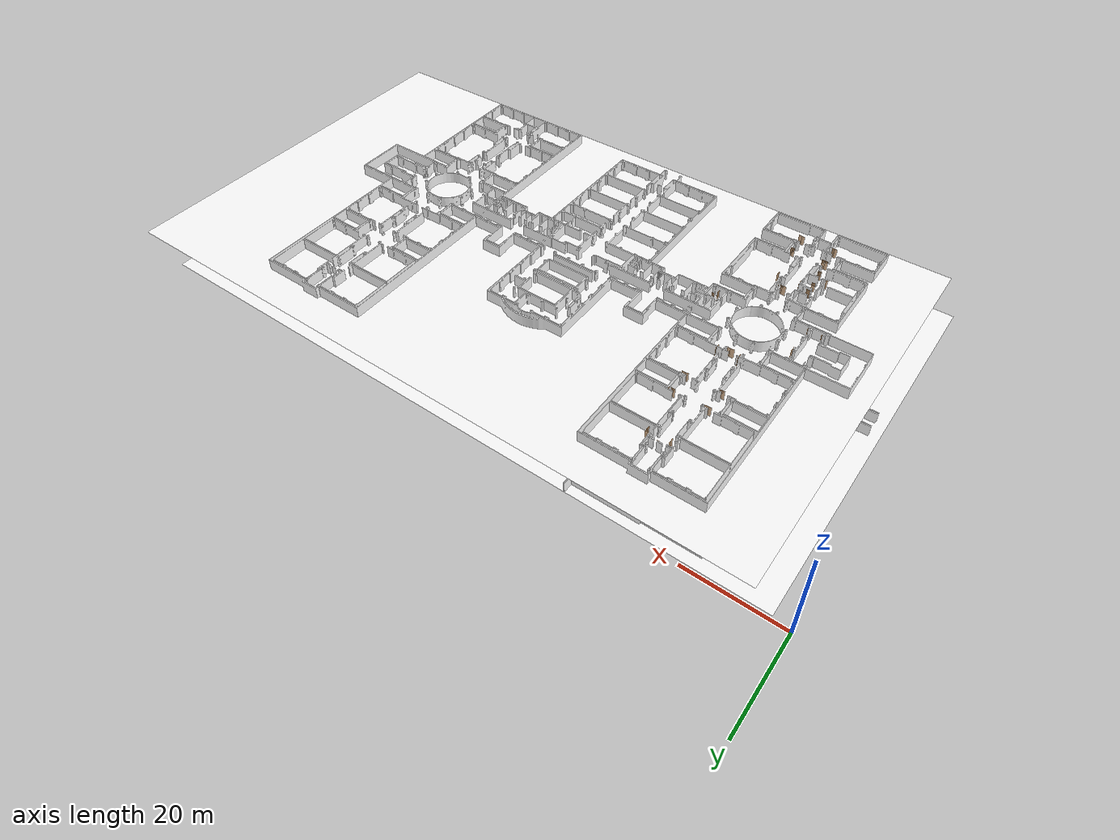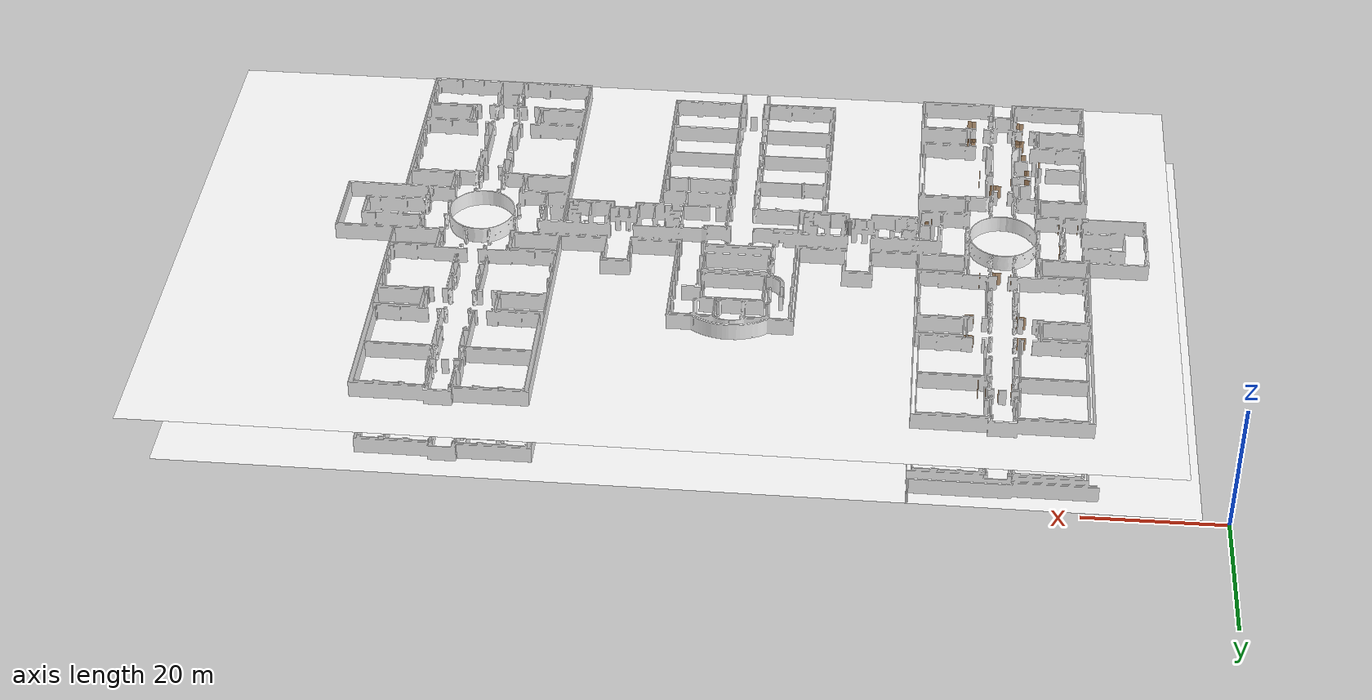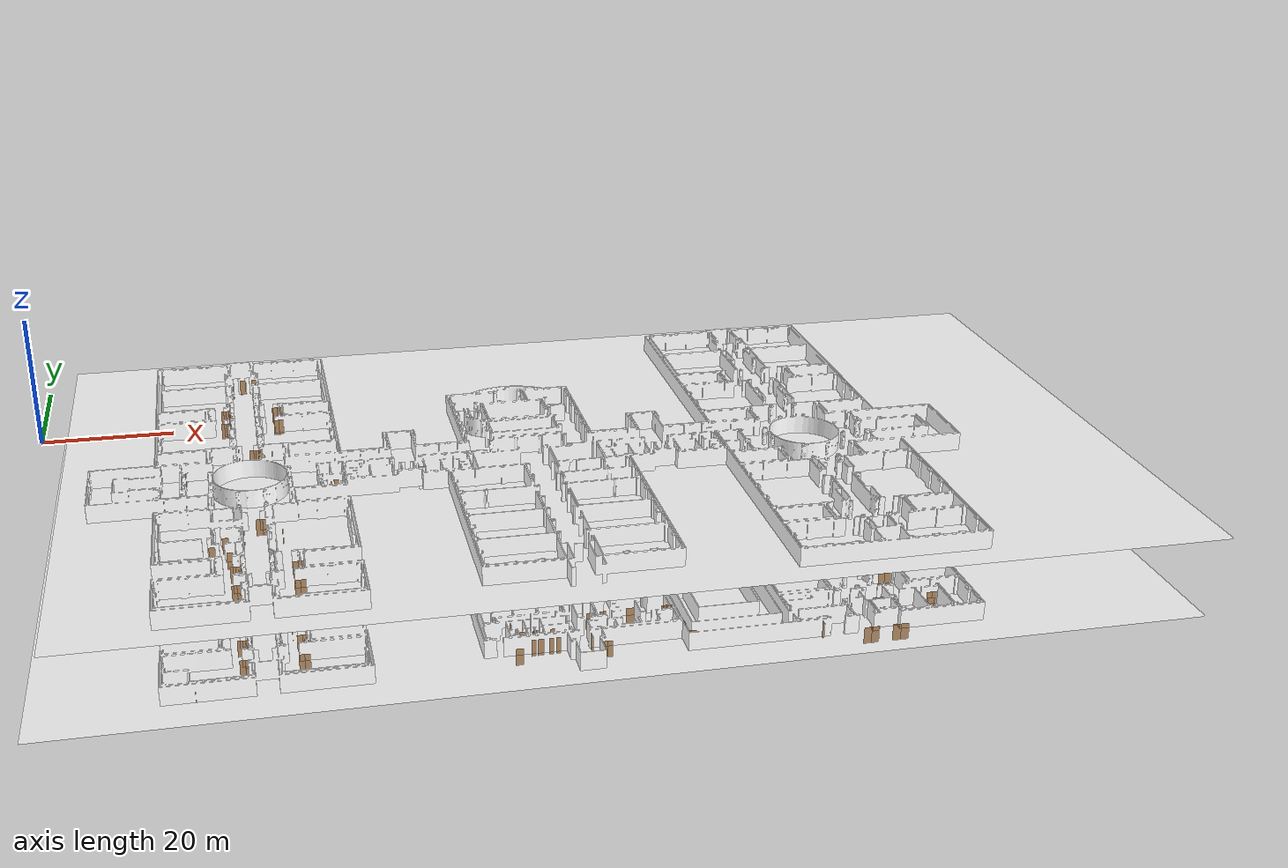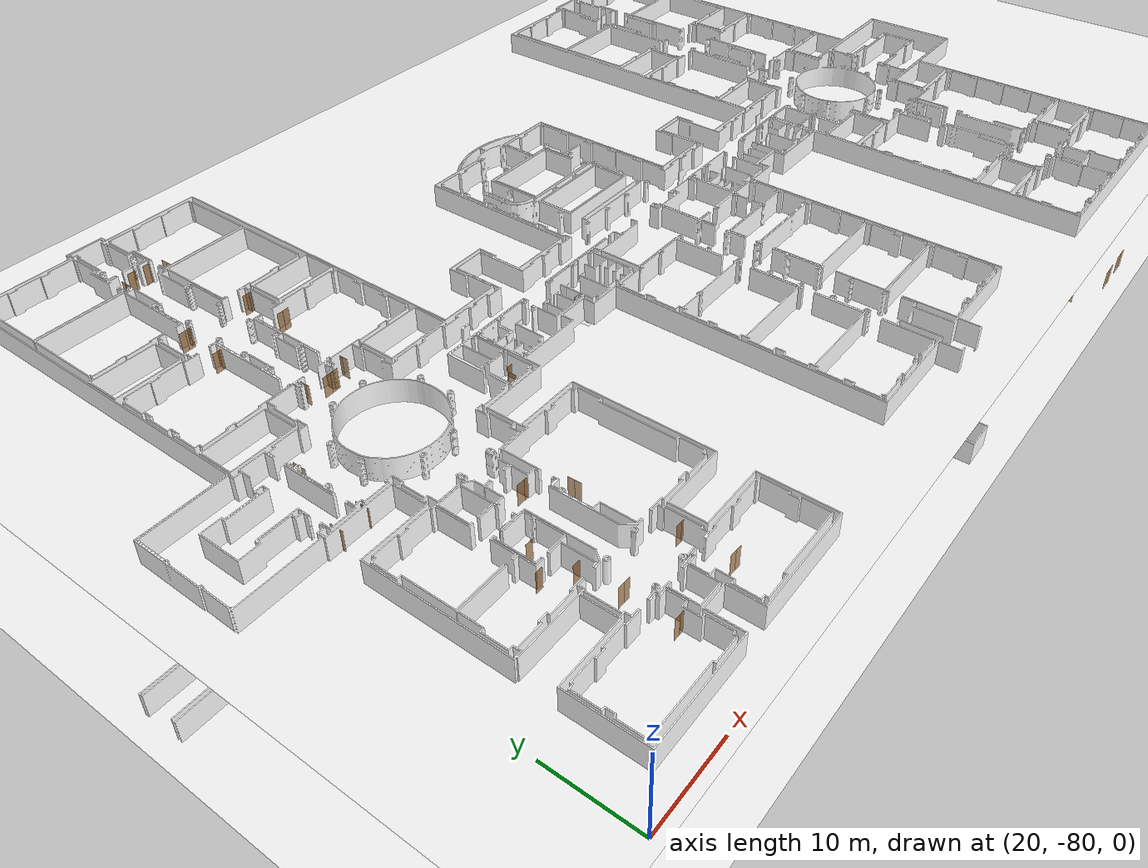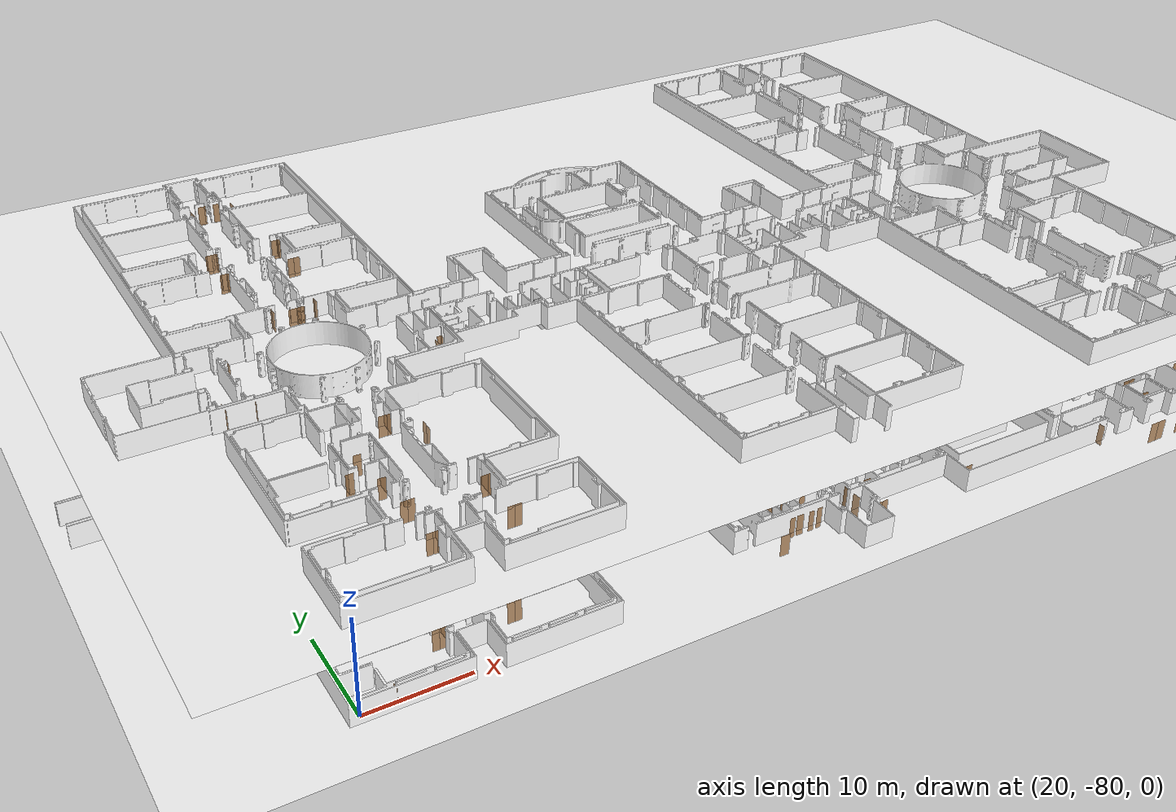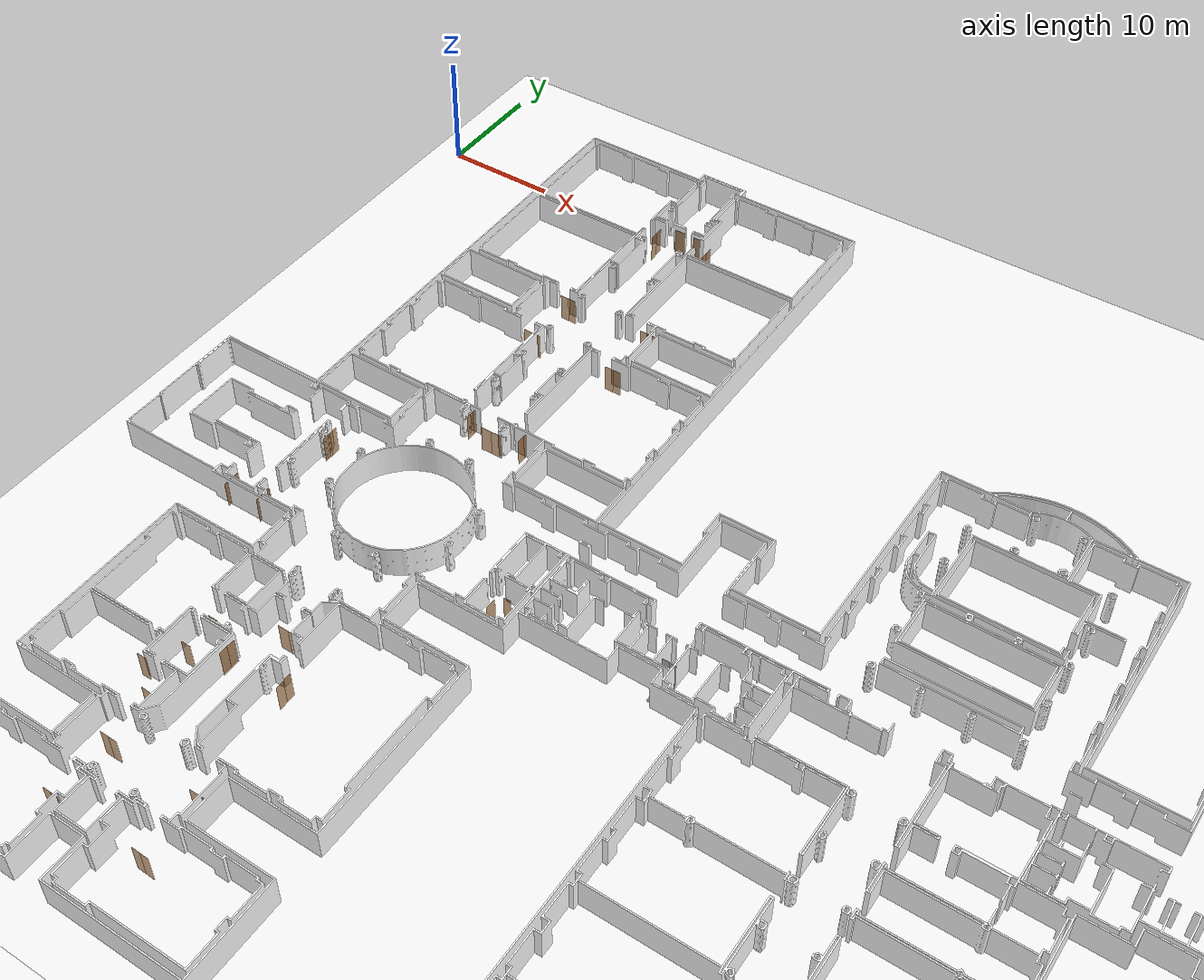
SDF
<sdf version="1.7">
 <world name="sim_world">
  <physics name="10ms" type="ode">
   <max_step_size>0.01</max_step_size>
   <real_time_factor>1.0</real_time_factor>
  </physics>
  <plugin filename="libgz-sim-physics-system.so" name="gz::sim::systems::Physics"/>
  <plugin filename="libgz-sim-user-commands-system.so" name="gz::sim::systems::UserCommands"/>
  <plugin filename="libgz-sim-scene-broadcaster-system.so" name="gz::sim::systems::SceneBroadcaster"/>
  <plugin filename="libdoor.so" name="door"/>
  <plugin filename="liblift.so" name="lift"/>
  <scene><ambient>1 1 1</ambient><background>0.8 0.8 0.8</background><grid>false</grid></scene>
  <light type="directional" name="sun">
   <pose>0 0 10 0 0 0</pose>
   <diffuse>1 1 1 1</diffuse>
   <specular>0.2 0.2 0.2 1</specular>
   <attenuation>
    <range>1000</range>
    <constant>0.09</constant>
    <linear>0.001</linear>
    <quadratic>0.001</quadratic>
   </attenuation>
   <direction>-0.5 0.1 -0.9</direction>
  </light>
  <model name="door3">
   <pose>28.769682966110175 -76.18987657758007 0.0 0 0 3.1348896198746523</pose>
   <link name="right">
    <pose>0.3339172068411305 0 1.11 0 0 0</pose>
    <visual name="right_visual">
     <geometry><box><size>0.657834413682261 0.03 2.2</size></box></geometry>
     <material>
      <ambient>0.5 0.25 0 0.6</ambient>
      <diffuse>0.5 0.25 0 0.6</diffuse>
      <pbr><metal><metalness>0.0</metalness></metal></pbr>
     </material>
    </visual>
    <collision name="right_collision">
     <geometry><box><size>0.657834413682261 0.03 2.2</size></box></geometry>
     <surface><contact><collide_bitmask>0x02</collide_bitmask></contact></surface>
    </collision>
    <inertial>
     <mass>50.0</mass>
     <inertia><ixx>20.17041666666667</ixx><iyy>21.969775482602856</iyy><izz>1.806858815936184</izz></inertia>
    </inertial>
   </link>
   <joint name="right_joint" type="revolute">
    <parent>world</parent>
    <child>right</child>
    <axis><xyz>0 0 1</xyz><limit><lower>0</lower><upper>1.57</upper></limit></axis>
    <pose>0.3339172068411305 0 0 0 0 0</pose>
   </joint>
   <link name="left">
    <pose>-0.3339172068411305 0 1.11 0 0 0</pose>
    <visual name="left_visual">
     <geometry><box><size>0.657834413682261 0.03 2.2</size></box></geometry>
     <material>
      <ambient>0.5 0.25 0 0.6</ambient>
      <diffuse>0.5 0.25 0 0.6</diffuse>
      <pbr><metal><metalness>0.0</metalness></metal></pbr>
     </material>
    </visual>
    <collision name="left_collision">
     <geometry><box><size>0.657834413682261 0.03 2.2</size></box></geometry>
     <surface><contact><collide_bitmask>0x02</collide_bitmask></contact></surface>
    </collision>
    <inertial>
     <mass>50.0</mass>
     <inertia><ixx>20.17041666666667</ixx><iyy>21.969775482602856</iyy><izz>1.806858815936184</izz></inertia>
    </inertial>
   </link>
   <joint name="left_joint" type="revolute">
    <parent>world</parent>
    <child>left</child>
    <axis><xyz>0 0 1</xyz><limit><lower>-1.57</lower><upper>0</upper></limit></axis>
    <pose>-0.3339172068411305 0 0 0 0 0</pose>
   </joint>
   <plugin name="register_component" filename="libregister_component.so">
    <component name="Door">
     <v_max_door>0.5</v_max_door>
     <a_max_door>0.3</a_max_door>
     <a_nom_door>0.15</a_nom_door>
     <dx_min_door>0.01</dx_min_door>
     <f_max_door>500.0</f_max_door>
     <ros_interface>true</ros_interface>
     <door name="door3" type="DoubleSwingDoor" left_joint_name="left_joint" right_joint_name="right_joint"/>
    </component>
   </plugin>
  </model>
  <model name="door2">
   <pose>22.94748524611663 -80.48593791590486 0.0 0 0 1.5613574322392023</pose>
   <link name="right">
    <pose>0 0 1.11 0 0 0</pose>
    <visual name="right_visual">
     <geometry><box><size>0.6403317074376793 0.03 2.2</size></box></geometry>
     <material>
      <ambient>0.5 0.25 0 0.6</ambient>
      <diffuse>0.5 0.25 0 0.6</diffuse>
      <pbr><metal><metalness>0.0</metalness></metal></pbr>
     </material>
    </visual>
    <collision name="right_collision">
     <geometry><box><size>0.6403317074376793 0.03 2.2</size></box></geometry>
     <surface><contact><collide_bitmask>0x02</collide_bitmask></contact></surface>
    </collision>
    <inertial>
     <mass>50.0</mass>
     <inertia><ixx>20.17041666666667</ixx><iyy>21.87510289812523</iyy><izz>1.7121862314585574</izz></inertia>
    </inertial>
   </link>
   <joint name="right_joint" type="revolute">
    <parent>world</parent>
    <child>right</child>
    <axis><xyz>0 0 -1</xyz><limit><lower>0</lower><upper>1.57</upper></limit></axis>
    <pose>0.32516585371883966 0 0 0 0 0</pose>
   </joint>
   <plugin name="register_component" filename="libregister_component.so">
    <component name="Door">
     <v_max_door>0.5</v_max_door>
     <a_max_door>0.3</a_max_door>
     <a_nom_door>0.15</a_nom_door>
     <dx_min_door>0.01</dx_min_door>
     <f_max_door>500.0</f_max_door>
     <ros_interface>true</ros_interface>
     <door name="door2" type="SwingDoor" left_joint_name="empty_joint" right_joint_name="right_joint"/>
    </component>
   </plugin>
  </model>
  <model name="door4">
   <pose>28.625671960623674 -71.5499794193153 0.0 0 0 3.11905020500011</pose>
   <link name="right">
    <pose>0.32811675026087656 0 1.11 0 0 0</pose>
    <visual name="right_visual">
     <geometry><box><size>0.6462335005217531 0.03 2.2</size></box></geometry>
     <material>
      <ambient>0.5 0.25 0 0.6</ambient>
      <diffuse>0.5 0.25 0 0.6</diffuse>
      <pbr><metal><metalness>0.0</metalness></metal></pbr>
     </material>
    </visual>
    <collision name="right_collision">
     <geometry><box><size>0.6462335005217531 0.03 2.2</size></box></geometry>
     <surface><contact><collide_bitmask>0x02</collide_bitmask></contact></surface>
    </collision>
    <inertial>
     <mass>50.0</mass>
     <inertia><ixx>20.17041666666667</ixx><iyy>21.9067405716525</iyy><izz>1.743823904985828</izz></inertia>
    </inertial>
   </link>
   <joint name="right_joint" type="revolute">
    <parent>world</parent>
    <child>right</child>
    <axis><xyz>0 0 -1</xyz><limit><lower>0</lower><upper>1.57</upper></limit></axis>
    <pose>0.32811675026087656 0 0 0 0 0</pose>
   </joint>
   <link name="left">
    <pose>-0.32811675026087656 0 1.11 0 0 0</pose>
    <visual name="left_visual">
     <geometry><box><size>0.6462335005217531 0.03 2.2</size></box></geometry>
     <material>
      <ambient>0.5 0.25 0 0.6</ambient>
      <diffuse>0.5 0.25 0 0.6</diffuse>
      <pbr><metal><metalness>0.0</metalness></metal></pbr>
     </material>
    </visual>
    <collision name="left_collision">
     <geometry><box><size>0.6462335005217531 0.03 2.2</size></box></geometry>
     <surface><contact><collide_bitmask>0x02</collide_bitmask></contact></surface>
    </collision>
    <inertial>
     <mass>50.0</mass>
     <inertia><ixx>20.17041666666667</ixx><iyy>21.9067405716525</iyy><izz>1.743823904985828</izz></inertia>
    </inertial>
   </link>
   <joint name="left_joint" type="revolute">
    <parent>world</parent>
    <child>left</child>
    <axis><xyz>0 0 -1</xyz><limit><lower>-1.57</lower><upper>0</upper></limit></axis>
    <pose>-0.32811675026087656 0 0 0 0 0</pose>
   </joint>
   <plugin name="register_component" filename="libregister_component.so">
    <component name="Door">
     <v_max_door>0.5</v_max_door>
     <a_max_door>0.3</a_max_door>
     <a_nom_door>0.15</a_nom_door>
     <dx_min_door>0.01</dx_min_door>
     <f_max_door>500.0</f_max_door>
     <ros_interface>true</ros_interface>
     <door name="door4" type="DoubleSwingDoor" left_joint_name="left_joint" right_joint_name="right_joint"/>
    </component>
   </plugin>
  </model>
  <model name="door6">
   <pose>29.725404615578547 -70.23633375402764 0.0 0 0 1.5890064580823675</pose>
   <link name="right">
    <pose>0 0 1.11 0 0 0</pose>
    <visual name="right_visual">
     <geometry><box><size>0.6543363938306009 0.03 2.2</size></box></geometry>
     <material>
      <ambient>0.5 0.25 0 0.6</ambient>
      <diffuse>0.5 0.25 0 0.6</diffuse>
      <pbr><metal><metalness>0.0</metalness></metal></pbr>
     </material>
    </visual>
    <collision name="right_collision">
     <geometry><box><size>0.6543363938306009 0.03 2.2</size></box></geometry>
     <surface><contact><collide_bitmask>0x02</collide_bitmask></contact></surface>
    </collision>
    <inertial>
     <mass>50.0</mass>
     <inertia><ixx>20.17041666666667</ixx><iyy>21.950650484546816</iyy><izz>1.7877338178801472</izz></inertia>
    </inertial>
   </link>
   <joint name="right_joint" type="revolute">
    <parent>world</parent>
    <child>right</child>
    <axis><xyz>0 0 -1</xyz><limit><lower>0</lower><upper>1.57</upper></limit></axis>
    <pose>0.3321681969153005 0 0 0 0 0</pose>
   </joint>
   <plugin name="register_component" filename="libregister_component.so">
    <component name="Door">
     <v_max_door>0.5</v_max_door>
     <a_max_door>0.3</a_max_door>
     <a_nom_door>0.15</a_nom_door>
     <dx_min_door>0.01</dx_min_door>
     <f_max_door>500.0</f_max_door>
     <ros_interface>true</ros_interface>
     <door name="door6" type="SwingDoor" left_joint_name="empty_joint" right_joint_name="right_joint"/>
    </component>
   </plugin>
  </model>
  <model name="door7">
   <pose>20.669164965222645 -64.56711497717382 0.0 0 0 -3.1176010818886466</pose>
   <link name="right">
    <pose>0 0 1.11 0 0 0</pose>
    <visual name="right_visual">
     <geometry><box><size>0.6165885214717833 0.03 2.2</size></box></geometry>
     <material>
      <ambient>0.5 0.25 0 0.6</ambient>
      <diffuse>0.5 0.25 0 0.6</diffuse>
      <pbr><metal><metalness>0.0</metalness></metal></pbr>
     </material>
    </visual>
    <collision name="right_collision">
     <geometry><box><size>0.6165885214717833 0.03 2.2</size></box></geometry>
     <surface><contact><collide_bitmask>0x02</collide_bitmask></contact></surface>
    </collision>
    <inertial>
     <mass>50.0</mass>
     <inertia><ixx>20.17041666666667</ixx><iyy>21.75075585337817</iyy><izz>1.5878391867114994</izz></inertia>
    </inertial>
   </link>
   <joint name="right_joint" type="revolute">
    <parent>world</parent>
    <child>right</child>
    <axis><xyz>0 0 -1</xyz><limit><lower>0</lower><upper>1.57</upper></limit></axis>
    <pose>0.31329426073589167 0 0 0 0 0</pose>
   </joint>
   <plugin name="register_component" filename="libregister_component.so">
    <component name="Door">
     <v_max_door>0.5</v_max_door>
     <a_max_door>0.3</a_max_door>
     <a_nom_door>0.15</a_nom_door>
     <dx_min_door>0.01</dx_min_door>
     <f_max_door>500.0</f_max_door>
     <ros_interface>true</ros_interface>
     <door name="door7" type="SwingDoor" left_joint_name="empty_joint" right_joint_name="right_joint"/>
    </component>
   </plugin>
  </model>
  <model name="door8">
   <pose>29.60678530000837 -64.5586860140707 0.0 0 0 -3.138557686043686</pose>
   <link name="right">
    <pose>0 0 1.11 0 0 0</pose>
    <visual name="right_visual">
     <geometry><box><size>0.5918277429835981 0.03 2.2</size></box></geometry>
     <material>
      <ambient>0.5 0.25 0 0.6</ambient>
      <diffuse>0.5 0.25 0 0.6</diffuse>
      <pbr><metal><metalness>0.0</metalness></metal></pbr>
     </material>
    </visual>
    <collision name="right_collision">
     <geometry><box><size>0.5918277429835981 0.03 2.2</size></box></geometry>
     <surface><contact><collide_bitmask>0x02</collide_bitmask></contact></surface>
    </collision>
    <inertial>
     <mass>50.0</mass>
     <inertia><ixx>20.17041666666667</ixx><iyy>21.626083655687754</iyy><izz>1.4631669890210828</izz></inertia>
    </inertial>
   </link>
   <joint name="right_joint" type="revolute">
    <parent>world</parent>
    <child>right</child>
    <axis><xyz>0 0 1</xyz><limit><lower>0</lower><upper>1.57</upper></limit></axis>
    <pose>0.30091387149179905 0 0 0 0 0</pose>
   </joint>
   <plugin name="register_component" filename="libregister_component.so">
    <component name="Door">
     <v_max_door>0.5</v_max_door>
     <a_max_door>0.3</a_max_door>
     <a_nom_door>0.15</a_nom_door>
     <dx_min_door>0.01</dx_min_door>
     <f_max_door>500.0</f_max_door>
     <ros_interface>true</ros_interface>
     <door name="door8" type="SwingDoor" left_joint_name="empty_joint" right_joint_name="right_joint"/>
    </component>
   </plugin>
  </model>
  <model name="door11">
   <pose>27.80737384991823 -63.66659330454594 0.0 0 0 1.5901401190466442</pose>
   <link name="right">
    <pose>0 0 1.11 0 0 0</pose>
    <visual name="right_visual">
     <geometry><box><size>0.7733065094868109 0.03 2.2</size></box></geometry>
     <material>
      <ambient>0.5 0.25 0 0.6</ambient>
      <diffuse>0.5 0.25 0 0.6</diffuse>
      <pbr><metal><metalness>0.0</metalness></metal></pbr>
     </material>
    </visual>
    <collision name="right_collision">
     <geometry><box><size>0.7733065094868109 0.03 2.2</size></box></geometry>
     <surface><contact><collide_bitmask>0x02</collide_bitmask></contact></surface>
    </collision>
    <inertial>
     <mass>50.0</mass>
     <inertia><ixx>20.17041666666667</ixx><iyy>22.658345656727818</iyy><izz>2.495428990061147</izz></inertia>
    </inertial>
   </link>
   <joint name="right_joint" type="revolute">
    <parent>world</parent>
    <child>right</child>
    <axis><xyz>0 0 1</xyz><limit><lower>0</lower><upper>1.57</upper></limit></axis>
    <pose>0.39165325474340545 0 0 0 0 0</pose>
   </joint>
   <plugin name="register_component" filename="libregister_component.so">
    <component name="Door">
     <v_max_door>0.5</v_max_door>
     <a_max_door>0.3</a_max_door>
     <a_nom_door>0.15</a_nom_door>
     <dx_min_door>0.01</dx_min_door>
     <f_max_door>500.0</f_max_door>
     <ros_interface>true</ros_interface>
     <door name="door11" type="SwingDoor" left_joint_name="empty_joint" right_joint_name="right_joint"/>
    </component>
   </plugin>
  </model>
  <model name="door12">
   <pose>29.893474846121375 -62.41476502585291 0.0 0 0 1.569960739769454</pose>
   <link name="right">
    <pose>0.3404299190586607 0 1.11 0 0 0</pose>
    <visual name="right_visual">
     <geometry><box><size>0.6708598381173214 0.03 2.2</size></box></geometry>
     <material>
      <ambient>0.5 0.25 0 0.6</ambient>
      <diffuse>0.5 0.25 0 0.6</diffuse>
      <pbr><metal><metalness>0.0</metalness></metal></pbr>
     </material>
    </visual>
    <collision name="right_collision">
     <geometry><box><size>0.6708598381173214 0.03 2.2</size></box></geometry>
     <surface><contact><collide_bitmask>0x02</collide_bitmask></contact></surface>
    </collision>
    <inertial>
     <mass>50.0</mass>
     <inertia><ixx>20.17041666666667</ixx><iyy>22.041887176661664</iyy><izz>1.8789705099949947</izz></inertia>
    </inertial>
   </link>
   <joint name="right_joint" type="revolute">
    <parent>world</parent>
    <child>right</child>
    <axis><xyz>0 0 1</xyz><limit><lower>0</lower><upper>1.57</upper></limit></axis>
    <pose>0.3404299190586607 0 0 0 0 0</pose>
   </joint>
   <link name="left">
    <pose>-0.3404299190586607 0 1.11 0 0 0</pose>
    <visual name="left_visual">
     <geometry><box><size>0.6708598381173214 0.03 2.2</size></box></geometry>
     <material>
      <ambient>0.5 0.25 0 0.6</ambient>
      <diffuse>0.5 0.25 0 0.6</diffuse>
      <pbr><metal><metalness>0.0</metalness></metal></pbr>
     </material>
    </visual>
    <collision name="left_collision">
     <geometry><box><size>0.6708598381173214 0.03 2.2</size></box></geometry>
     <surface><contact><collide_bitmask>0x02</collide_bitmask></contact></surface>
    </collision>
    <inertial>
     <mass>50.0</mass>
     <inertia><ixx>20.17041666666667</ixx><iyy>22.041887176661664</iyy><izz>1.8789705099949947</izz></inertia>
    </inertial>
   </link>
   <joint name="left_joint" type="revolute">
    <parent>world</parent>
    <child>left</child>
    <axis><xyz>0 0 1</xyz><limit><lower>-1.57</lower><upper>0</upper></limit></axis>
    <pose>-0.3404299190586607 0 0 0 0 0</pose>
   </joint>
   <plugin name="register_component" filename="libregister_component.so">
    <component name="Door">
     <v_max_door>0.5</v_max_door>
     <a_max_door>0.3</a_max_door>
     <a_nom_door>0.15</a_nom_door>
     <dx_min_door>0.01</dx_min_door>
     <f_max_door>500.0</f_max_door>
     <ros_interface>true</ros_interface>
     <door name="door12" type="DoubleSwingDoor" left_joint_name="left_joint" right_joint_name="right_joint"/>
    </component>
   </plugin>
  </model>
  <model name="door14">
   <pose>29.74922429639038 -60.3268375047855 0.0 0 0 1.6107948883778511</pose>
   <link name="right">
    <pose>0 0 1.11 0 0 0</pose>
    <visual name="right_visual">
     <geometry><box><size>0.7125942527000033 0.03 2.2</size></box></geometry>
     <material>
      <ambient>0.5 0.25 0 0.6</ambient>
      <diffuse>0.5 0.25 0 0.6</diffuse>
      <pbr><metal><metalness>0.0</metalness></metal></pbr>
     </material>
    </visual>
    <collision name="right_collision">
     <geometry><box><size>0.7125942527000033 0.03 2.2</size></box></geometry>
     <surface><contact><collide_bitmask>0x02</collide_bitmask></contact></surface>
    </collision>
    <inertial>
     <mass>50.0</mass>
     <inertia><ixx>20.17041666666667</ixx><iyy>22.282460704087825</iyy><izz>2.119544037421151</izz></inertia>
    </inertial>
   </link>
   <joint name="right_joint" type="revolute">
    <parent>world</parent>
    <child>right</child>
    <axis><xyz>0 0 1</xyz><limit><lower>0</lower><upper>1.57</upper></limit></axis>
    <pose>0.36129712635000166 0 0 0 0 0</pose>
   </joint>
   <plugin name="register_component" filename="libregister_component.so">
    <component name="Door">
     <v_max_door>0.5</v_max_door>
     <a_max_door>0.3</a_max_door>
     <a_nom_door>0.15</a_nom_door>
     <dx_min_door>0.01</dx_min_door>
     <f_max_door>500.0</f_max_door>
     <ros_interface>true</ros_interface>
     <door name="door14" type="SwingDoor" left_joint_name="empty_joint" right_joint_name="right_joint"/>
    </component>
   </plugin>
  </model>
  <model name="door17_end">
   <pose>32.24229599247289 -59.333746953176124 0.0 0 0 3.129395427821512</pose>
   <link name="right">
    <pose>0.40445562780894295 0 1.11 0 0 0</pose>
    <visual name="right_visual">
     <geometry><box><size>0.7989112556178859 0.03 2.2</size></box></geometry>
     <material>
      <ambient>0.5 0.25 0 0.6</ambient>
      <diffuse>0.5 0.25 0 0.6</diffuse>
      <pbr><metal><metalness>0.0</metalness></metal></pbr>
     </material>
    </visual>
    <collision name="right_collision">
     <geometry><box><size>0.7989112556178859 0.03 2.2</size></box></geometry>
     <surface><contact><collide_bitmask>0x02</collide_bitmask></contact></surface>
    </collision>
    <inertial>
     <mass>50.0</mass>
     <inertia><ixx>20.17041666666667</ixx><iyy>22.826079976470616</iyy><izz>2.663163309803946</izz></inertia>
    </inertial>
   </link>
   <joint name="right_joint" type="revolute">
    <parent>world</parent>
    <child>right</child>
    <axis><xyz>0 0 1</xyz><limit><lower>0</lower><upper>1.57</upper></limit></axis>
    <pose>0.40445562780894295 0 0 0 0 0</pose>
   </joint>
   <link name="left">
    <pose>-0.40445562780894295 0 1.11 0 0 0</pose>
    <visual name="left_visual">
     <geometry><box><size>0.7989112556178859 0.03 2.2</size></box></geometry>
     <material>
      <ambient>0.5 0.25 0 0.6</ambient>
      <diffuse>0.5 0.25 0 0.6</diffuse>
      <pbr><metal><metalness>0.0</metalness></metal></pbr>
     </material>
    </visual>
    <collision name="left_collision">
     <geometry><box><size>0.7989112556178859 0.03 2.2</size></box></geometry>
     <surface><contact><collide_bitmask>0x02</collide_bitmask></contact></surface>
    </collision>
    <inertial>
     <mass>50.0</mass>
     <inertia><ixx>20.17041666666667</ixx><iyy>22.826079976470616</iyy><izz>2.663163309803946</izz></inertia>
    </inertial>
   </link>
   <joint name="left_joint" type="revolute">
    <parent>world</parent>
    <child>left</child>
    <axis><xyz>0 0 1</xyz><limit><lower>-1.57</lower><upper>0</upper></limit></axis>
    <pose>-0.40445562780894295 0 0 0 0 0</pose>
   </joint>
   <plugin name="register_component" filename="libregister_component.so">
    <component name="Door">
     <v_max_door>0.5</v_max_door>
     <a_max_door>0.3</a_max_door>
     <a_nom_door>0.15</a_nom_door>
     <dx_min_door>0.01</dx_min_door>
     <f_max_door>500.0</f_max_door>
     <ros_interface>true</ros_interface>
     <door name="door17_end" type="DoubleSwingDoor" left_joint_name="left_joint" right_joint_name="right_joint"/>
    </component>
   </plugin>
  </model>
  <model name="door15">
   <pose>34.61065496626591 -60.36628744755054 0.0 0 0 1.570095261290011</pose>
   <link name="right">
    <pose>0 0 1.11 0 0 0</pose>
    <visual name="right_visual">
     <geometry><box><size>0.6306612393383593 0.03 2.2</size></box></geometry>
     <material>
      <ambient>0.5 0.25 0 0.6</ambient>
      <diffuse>0.5 0.25 0 0.6</diffuse>
      <pbr><metal><metalness>0.0</metalness></metal></pbr>
     </material>
    </visual>
    <collision name="right_collision">
     <geometry><box><size>0.6306612393383593 0.03 2.2</size></box></geometry>
     <surface><contact><collide_bitmask>0x02</collide_bitmask></contact></surface>
    </collision>
    <inertial>
     <mass>50.0</mass>
     <inertia><ixx>20.17041666666667</ixx><iyy>21.82388999501582</iyy><izz>1.6609733283491472</izz></inertia>
    </inertial>
   </link>
   <joint name="right_joint" type="revolute">
    <parent>world</parent>
    <child>right</child>
    <axis><xyz>0 0 -1</xyz><limit><lower>0</lower><upper>1.57</upper></limit></axis>
    <pose>0.32033061966917964 0 0 0 0 0</pose>
   </joint>
   <plugin name="register_component" filename="libregister_component.so">
    <component name="Door">
     <v_max_door>0.5</v_max_door>
     <a_max_door>0.3</a_max_door>
     <a_nom_door>0.15</a_nom_door>
     <dx_min_door>0.01</dx_min_door>
     <f_max_door>500.0</f_max_door>
     <ros_interface>true</ros_interface>
     <door name="door15" type="SwingDoor" left_joint_name="empty_joint" right_joint_name="right_joint"/>
    </component>
   </plugin>
  </model>
  <model name="door13">
   <pose>34.468605229281195 -62.442971360642034 0.0 0 0 1.5796133810395</pose>
   <link name="right">
    <pose>0.3489471844600706 0 1.11 0 0 0</pose>
    <visual name="right_visual">
     <geometry><box><size>0.6878943689201412 0.03 2.2</size></box></geometry>
     <material>
      <ambient>0.5 0.25 0 0.6</ambient>
      <diffuse>0.5 0.25 0 0.6</diffuse>
      <pbr><metal><metalness>0.0</metalness></metal></pbr>
     </material>
    </visual>
    <collision name="right_collision">
     <geometry><box><size>0.6878943689201412 0.03 2.2</size></box></geometry>
     <surface><contact><collide_bitmask>0x02</collide_bitmask></contact></surface>
    </collision>
    <inertial>
     <mass>50.0</mass>
     <inertia><ixx>20.17041666666667</ixx><iyy>22.1383277616335</iyy><izz>1.9754110949668309</izz></inertia>
    </inertial>
   </link>
   <joint name="right_joint" type="revolute">
    <parent>world</parent>
    <child>right</child>
    <axis><xyz>0 0 -1</xyz><limit><lower>0</lower><upper>1.57</upper></limit></axis>
    <pose>0.3489471844600706 0 0 0 0 0</pose>
   </joint>
   <link name="left">
    <pose>-0.3489471844600706 0 1.11 0 0 0</pose>
    <visual name="left_visual">
     <geometry><box><size>0.6878943689201412 0.03 2.2</size></box></geometry>
     <material>
      <ambient>0.5 0.25 0 0.6</ambient>
      <diffuse>0.5 0.25 0 0.6</diffuse>
      <pbr><metal><metalness>0.0</metalness></metal></pbr>
     </material>
    </visual>
    <collision name="left_collision">
     <geometry><box><size>0.6878943689201412 0.03 2.2</size></box></geometry>
     <surface><contact><collide_bitmask>0x02</collide_bitmask></contact></surface>
    </collision>
    <inertial>
     <mass>50.0</mass>
     <inertia><ixx>20.17041666666667</ixx><iyy>22.1383277616335</iyy><izz>1.9754110949668309</izz></inertia>
    </inertial>
   </link>
   <joint name="left_joint" type="revolute">
    <parent>world</parent>
    <child>left</child>
    <axis><xyz>0 0 -1</xyz><limit><lower>-1.57</lower><upper>0</upper></limit></axis>
    <pose>-0.3489471844600706 0 0 0 0 0</pose>
   </joint>
   <plugin name="register_component" filename="libregister_component.so">
    <component name="Door">
     <v_max_door>0.5</v_max_door>
     <a_max_door>0.3</a_max_door>
     <a_nom_door>0.15</a_nom_door>
     <dx_min_door>0.01</dx_min_door>
     <f_max_door>500.0</f_max_door>
     <ros_interface>true</ros_interface>
     <door name="door13" type="DoubleSwingDoor" left_joint_name="left_joint" right_joint_name="right_joint"/>
    </component>
   </plugin>
  </model>
  <model name="door10">
   <pose>38.08370216657176 -63.6204960089962 0.0 0 0 3.141592653589793</pose>
   <link name="right">
    <pose>0 0 1.11 0 0 0</pose>
    <visual name="right_visual">
     <geometry><box><size>0.8446938643531945 0.03 2.2</size></box></geometry>
     <material>
      <ambient>0.5 0.25 0 0.6</ambient>
      <diffuse>0.5 0.25 0 0.6</diffuse>
      <pbr><metal><metalness>0.0</metalness></metal></pbr>
     </material>
    </visual>
    <collision name="right_collision">
     <geometry><box><size>0.8446938643531945 0.03 2.2</size></box></geometry>
     <surface><contact><collide_bitmask>0x02</collide_bitmask></contact></surface>
    </collision>
    <inertial>
     <mass>50.0</mass>
     <inertia><ixx>20.17041666666667</ixx><iyy>23.139615518649723</iyy><izz>2.976698851983054</izz></inertia>
    </inertial>
   </link>
   <joint name="right_joint" type="revolute">
    <parent>world</parent>
    <child>right</child>
    <axis><xyz>0 0 -1</xyz><limit><lower>0</lower><upper>1.57</upper></limit></axis>
    <pose>0.42734693217659725 0 0 0 0 0</pose>
   </joint>
   <plugin name="register_component" filename="libregister_component.so">
    <component name="Door">
     <v_max_door>0.5</v_max_door>
     <a_max_door>0.3</a_max_door>
     <a_nom_door>0.15</a_nom_door>
     <dx_min_door>0.01</dx_min_door>
     <f_max_door>500.0</f_max_door>
     <ros_interface>true</ros_interface>
     <door name="door10" type="SwingDoor" left_joint_name="empty_joint" right_joint_name="right_joint"/>
    </component>
   </plugin>
  </model>
  <model name="door9">
   <pose>38.13673127369653 -65.39471039886867 0.0 0 0 3.141592653589793</pose>
   <link name="right">
    <pose>0 0 1.11 0 0 0</pose>
    <visual name="right_visual">
     <geometry><box><size>0.832896310311886 0.03 2.2</size></box></geometry>
     <material>
      <ambient>0.5 0.25 0 0.6</ambient>
      <diffuse>0.5 0.25 0 0.6</diffuse>
      <pbr><metal><metalness>0.0</metalness></metal></pbr>
     </material>
    </visual>
    <collision name="right_collision">
     <geometry><box><size>0.832896310311886 0.03 2.2</size></box></geometry>
     <surface><contact><collide_bitmask>0x02</collide_bitmask></contact></surface>
    </collision>
    <inertial>
     <mass>50.0</mass>
     <inertia><ixx>20.17041666666667</ixx><iyy>23.05715109887981</iyy><izz>2.8942344322131404</izz></inertia>
    </inertial>
   </link>
   <joint name="right_joint" type="revolute">
    <parent>world</parent>
    <child>right</child>
    <axis><xyz>0 0 1</xyz><limit><lower>0</lower><upper>1.57</upper></limit></axis>
    <pose>0.421448155155943 0 0 0 0 0</pose>
   </joint>
   <plugin name="register_component" filename="libregister_component.so">
    <component name="Door">
     <v_max_door>0.5</v_max_door>
     <a_max_door>0.3</a_max_door>
     <a_nom_door>0.15</a_nom_door>
     <dx_min_door>0.01</dx_min_door>
     <f_max_door>500.0</f_max_door>
     <ros_interface>true</ros_interface>
     <door name="door9" type="SwingDoor" left_joint_name="empty_joint" right_joint_name="right_joint"/>
    </component>
   </plugin>
  </model>
  <model name="door5">
   <pose>35.76995928052328 -71.55423132965505 0.0 0 0 -3.1335801828914787</pose>
   <link name="right">
    <pose>0.3363384013789009 0 1.11 0 0 0</pose>
    <visual name="right_visual">
     <geometry><box><size>0.6626768027578018 0.03 2.2</size></box></geometry>
     <material>
      <ambient>0.5 0.25 0 0.6</ambient>
      <diffuse>0.5 0.25 0 0.6</diffuse>
      <pbr><metal><metalness>0.0</metalness></metal></pbr>
     </material>
    </visual>
    <collision name="right_collision">
     <geometry><box><size>0.6626768027578018 0.03 2.2</size></box></geometry>
     <surface><contact><collide_bitmask>0x02</collide_bitmask></contact></surface>
    </collision>
    <inertial>
     <mass>50.0</mass>
     <inertia><ixx>20.17041666666667</ixx><iyy>21.996418937138767</iyy><izz>1.8335022704720942</izz></inertia>
    </inertial>
   </link>
   <joint name="right_joint" type="revolute">
    <parent>world</parent>
    <child>right</child>
    <axis><xyz>0 0 -1</xyz><limit><lower>0</lower><upper>1.57</upper></limit></axis>
    <pose>0.3363384013789009 0 0 0 0 0</pose>
   </joint>
   <link name="left">
    <pose>-0.3363384013789009 0 1.11 0 0 0</pose>
    <visual name="left_visual">
     <geometry><box><size>0.6626768027578018 0.03 2.2</size></box></geometry>
     <material>
      <ambient>0.5 0.25 0 0.6</ambient>
      <diffuse>0.5 0.25 0 0.6</diffuse>
      <pbr><metal><metalness>0.0</metalness></metal></pbr>
     </material>
    </visual>
    <collision name="left_collision">
     <geometry><box><size>0.6626768027578018 0.03 2.2</size></box></geometry>
     <surface><contact><collide_bitmask>0x02</collide_bitmask></contact></surface>
    </collision>
    <inertial>
     <mass>50.0</mass>
     <inertia><ixx>20.17041666666667</ixx><iyy>21.996418937138767</iyy><izz>1.8335022704720942</izz></inertia>
    </inertial>
   </link>
   <joint name="left_joint" type="revolute">
    <parent>world</parent>
    <child>left</child>
    <axis><xyz>0 0 -1</xyz><limit><lower>-1.57</lower><upper>0</upper></limit></axis>
    <pose>-0.3363384013789009 0 0 0 0 0</pose>
   </joint>
   <plugin name="register_component" filename="libregister_component.so">
    <component name="Door">
     <v_max_door>0.5</v_max_door>
     <a_max_door>0.3</a_max_door>
     <a_nom_door>0.15</a_nom_door>
     <dx_min_door>0.01</dx_min_door>
     <f_max_door>500.0</f_max_door>
     <ros_interface>true</ros_interface>
     <door name="door5" type="DoubleSwingDoor" left_joint_name="left_joint" right_joint_name="right_joint"/>
    </component>
   </plugin>
  </model>
  <model name="door1">
   <pose>35.73196157474048 -76.17896234294034 0.0 0 0 3.1358409577189126</pose>
   <link name="right">
    <pose>0.3435944733193185 0 1.11 0 0 0</pose>
    <visual name="right_visual">
     <geometry><box><size>0.677188946638637 0.03 2.2</size></box></geometry>
     <material>
      <ambient>0.5 0.25 0 0.6</ambient>
      <diffuse>0.5 0.25 0 0.6</diffuse>
      <pbr><metal><metalness>0.0</metalness></metal></pbr>
     </material>
    </visual>
    <collision name="right_collision">
     <geometry><box><size>0.677188946638637 0.03 2.2</size></box></geometry>
     <surface><contact><collide_bitmask>0x02</collide_bitmask></contact></surface>
    </collision>
    <inertial>
     <mass>50.0</mass>
     <inertia><ixx>20.17041666666667</ixx><iyy>22.077436956039783</iyy><izz>1.914520289373112</izz></inertia>
    </inertial>
   </link>
   <joint name="right_joint" type="revolute">
    <parent>world</parent>
    <child>right</child>
    <axis><xyz>0 0 1</xyz><limit><lower>0</lower><upper>1.57</upper></limit></axis>
    <pose>0.3435944733193185 0 0 0 0 0</pose>
   </joint>
   <link name="left">
    <pose>-0.3435944733193185 0 1.11 0 0 0</pose>
    <visual name="left_visual">
     <geometry><box><size>0.677188946638637 0.03 2.2</size></box></geometry>
     <material>
      <ambient>0.5 0.25 0 0.6</ambient>
      <diffuse>0.5 0.25 0 0.6</diffuse>
      <pbr><metal><metalness>0.0</metalness></metal></pbr>
     </material>
    </visual>
    <collision name="left_collision">
     <geometry><box><size>0.677188946638637 0.03 2.2</size></box></geometry>
     <surface><contact><collide_bitmask>0x02</collide_bitmask></contact></surface>
    </collision>
    <inertial>
     <mass>50.0</mass>
     <inertia><ixx>20.17041666666667</ixx><iyy>22.077436956039783</iyy><izz>1.914520289373112</izz></inertia>
    </inertial>
   </link>
   <joint name="left_joint" type="revolute">
    <parent>world</parent>
    <child>left</child>
    <axis><xyz>0 0 1</xyz><limit><lower>-1.57</lower><upper>0</upper></limit></axis>
    <pose>-0.3435944733193185 0 0 0 0 0</pose>
   </joint>
   <plugin name="register_component" filename="libregister_component.so">
    <component name="Door">
     <v_max_door>0.5</v_max_door>
     <a_max_door>0.3</a_max_door>
     <a_nom_door>0.15</a_nom_door>
     <dx_min_door>0.01</dx_min_door>
     <f_max_door>500.0</f_max_door>
     <ros_interface>true</ros_interface>
     <door name="door1" type="DoubleSwingDoor" left_joint_name="left_joint" right_joint_name="right_joint"/>
    </component>
   </plugin>
  </model>
  <model name="door16">
   <pose>34.684838824482526 -68.70895473659056 0.0 0 0 1.5991199512423224</pose>
   <link name="right">
    <pose>0 0 1.11 0 0 0</pose>
    <visual name="right_visual">
     <geometry><box><size>0.6455362078870427 0.03 2.2</size></box></geometry>
     <material>
      <ambient>0.5 0.25 0 0.6</ambient>
      <diffuse>0.5 0.25 0 0.6</diffuse>
      <pbr><metal><metalness>0.0</metalness></metal></pbr>
     </material>
    </visual>
    <collision name="right_collision">
     <geometry><box><size>0.6455362078870427 0.03 2.2</size></box></geometry>
     <surface><contact><collide_bitmask>0x02</collide_bitmask></contact></surface>
    </collision>
    <inertial>
     <mass>50.0</mass>
     <inertia><ixx>20.17041666666667</ixx><iyy>21.902987482054936</iyy><izz>1.7400708153882636</izz></inertia>
    </inertial>
   </link>
   <joint name="right_joint" type="revolute">
    <parent>world</parent>
    <child>right</child>
    <axis><xyz>0 0 1</xyz><limit><lower>0</lower><upper>1.57</upper></limit></axis>
    <pose>0.32776810394352135 0 0 0 0 0</pose>
   </joint>
   <plugin name="register_component" filename="libregister_component.so">
    <component name="Door">
     <v_max_door>0.5</v_max_door>
     <a_max_door>0.3</a_max_door>
     <a_nom_door>0.15</a_nom_door>
     <dx_min_door>0.01</dx_min_door>
     <f_max_door>500.0</f_max_door>
     <ros_interface>true</ros_interface>
     <door name="door16" type="SwingDoor" left_joint_name="empty_joint" right_joint_name="right_joint"/>
    </component>
   </plugin>
  </model>
  <model name="door20">
   <pose>22.9317950981023 -44.21380406983128 0.0 0 0 1.5841898704715496</pose>
   <link name="right">
    <pose>0.33703155230400345 0 1.11 0 0 0</pose>
    <visual name="right_visual">
     <geometry><box><size>0.6640631046080069 0.03 2.2</size></box></geometry>
     <material>
      <ambient>0.5 0.25 0 0.6</ambient>
      <diffuse>0.5 0.25 0 0.6</diffuse>
      <pbr><metal><metalness>0.0</metalness></metal></pbr>
     </material>
    </visual>
    <collision name="right_collision">
     <geometry><box><size>0.6640631046080069 0.03 2.2</size></box></geometry>
     <surface><contact><collide_bitmask>0x02</collide_bitmask></contact></surface>
    </collision>
    <inertial>
     <mass>50.0</mass>
     <inertia><ixx>20.17041666666667</ixx><iyy>22.004082528756776</iyy><izz>1.841165862090103</izz></inertia>
    </inertial>
   </link>
   <joint name="right_joint" type="revolute">
    <parent>world</parent>
    <child>right</child>
    <axis><xyz>0 0 -1</xyz><limit><lower>0</lower><upper>1.57</upper></limit></axis>
    <pose>0.33703155230400345 0 0 0 0 0</pose>
   </joint>
   <link name="left">
    <pose>-0.33703155230400345 0 1.11 0 0 0</pose>
    <visual name="left_visual">
     <geometry><box><size>0.6640631046080069 0.03 2.2</size></box></geometry>
     <material>
      <ambient>0.5 0.25 0 0.6</ambient>
      <diffuse>0.5 0.25 0 0.6</diffuse>
      <pbr><metal><metalness>0.0</metalness></metal></pbr>
     </material>
    </visual>
    <collision name="left_collision">
     <geometry><box><size>0.6640631046080069 0.03 2.2</size></box></geometry>
     <surface><contact><collide_bitmask>0x02</collide_bitmask></contact></surface>
    </collision>
    <inertial>
     <mass>50.0</mass>
     <inertia><ixx>20.17041666666667</ixx><iyy>22.004082528756776</iyy><izz>1.841165862090103</izz></inertia>
    </inertial>
   </link>
   <joint name="left_joint" type="revolute">
    <parent>world</parent>
    <child>left</child>
    <axis><xyz>0 0 -1</xyz><limit><lower>-1.57</lower><upper>0</upper></limit></axis>
    <pose>-0.33703155230400345 0 0 0 0 0</pose>
   </joint>
   <plugin name="register_component" filename="libregister_component.so">
    <component name="Door">
     <v_max_door>0.5</v_max_door>
     <a_max_door>0.3</a_max_door>
     <a_nom_door>0.15</a_nom_door>
     <dx_min_door>0.01</dx_min_door>
     <f_max_door>500.0</f_max_door>
     <ros_interface>true</ros_interface>
     <door name="door20" type="DoubleSwingDoor" left_joint_name="left_joint" right_joint_name="right_joint"/>
    </component>
   </plugin>
  </model>
  <model name="door21_end">
   <pose>22.930657262940954 -51.23370804077758 0.0 0 0 1.5724148541161644</pose>
   <link name="right">
    <pose>0.3283781605271934 0 1.11 0 0 0</pose>
    <visual name="right_visual">
     <geometry><box><size>0.6467563210543867 0.03 2.2</size></box></geometry>
     <material>
      <ambient>0.5 0.25 0 0.6</ambient>
      <diffuse>0.5 0.25 0 0.6</diffuse>
      <pbr><metal><metalness>0.0</metalness></metal></pbr>
     </material>
    </visual>
    <collision name="right_collision">
     <geometry><box><size>0.6467563210543867 0.03 2.2</size></box></geometry>
     <surface><contact><collide_bitmask>0x02</collide_bitmask></contact></surface>
    </collision>
    <inertial>
     <mass>50.0</mass>
     <inertia><ixx>20.17041666666667</ixx><iyy>21.909557245099194</iyy><izz>1.746640578432521</izz></inertia>
    </inertial>
   </link>
   <joint name="right_joint" type="revolute">
    <parent>world</parent>
    <child>right</child>
    <axis><xyz>0 0 -1</xyz><limit><lower>0</lower><upper>1.57</upper></limit></axis>
    <pose>0.3283781605271934 0 0 0 0 0</pose>
   </joint>
   <link name="left">
    <pose>-0.3283781605271934 0 1.11 0 0 0</pose>
    <visual name="left_visual">
     <geometry><box><size>0.6467563210543867 0.03 2.2</size></box></geometry>
     <material>
      <ambient>0.5 0.25 0 0.6</ambient>
      <diffuse>0.5 0.25 0 0.6</diffuse>
      <pbr><metal><metalness>0.0</metalness></metal></pbr>
     </material>
    </visual>
    <collision name="left_collision">
     <geometry><box><size>0.6467563210543867 0.03 2.2</size></box></geometry>
     <surface><contact><collide_bitmask>0x02</collide_bitmask></contact></surface>
    </collision>
    <inertial>
     <mass>50.0</mass>
     <inertia><ixx>20.17041666666667</ixx><iyy>21.909557245099194</iyy><izz>1.746640578432521</izz></inertia>
    </inertial>
   </link>
   <joint name="left_joint" type="revolute">
    <parent>world</parent>
    <child>left</child>
    <axis><xyz>0 0 -1</xyz><limit><lower>-1.57</lower><upper>0</upper></limit></axis>
    <pose>-0.3283781605271934 0 0 0 0 0</pose>
   </joint>
   <plugin name="register_component" filename="libregister_component.so">
    <component name="Door">
     <v_max_door>0.5</v_max_door>
     <a_max_door>0.3</a_max_door>
     <a_nom_door>0.15</a_nom_door>
     <dx_min_door>0.01</dx_min_door>
     <f_max_door>500.0</f_max_door>
     <ros_interface>true</ros_interface>
     <door name="door21_end" type="DoubleSwingDoor" left_joint_name="left_joint" right_joint_name="right_joint"/>
    </component>
   </plugin>
  </model>
  <model name="door19">
   <pose>14.084737459250439 -51.22706068799289 0.0 0 0 1.5709468288255377</pose>
   <link name="right">
    <pose>0.3481700775569965 0 1.11 0 0 0</pose>
    <visual name="right_visual">
     <geometry><box><size>0.686340155113993 0.03 2.2</size></box></geometry>
     <material>
      <ambient>0.5 0.25 0 0.6</ambient>
      <diffuse>0.5 0.25 0 0.6</diffuse>
      <pbr><metal><metalness>0.0</metalness></metal></pbr>
     </material>
    </visual>
    <collision name="right_collision">
     <geometry><box><size>0.686340155113993 0.03 2.2</size></box></geometry>
     <surface><contact><collide_bitmask>0x02</collide_bitmask></contact></surface>
    </collision>
    <inertial>
     <mass>50.0</mass>
     <inertia><ixx>20.17041666666667</ixx><iyy>22.129428368841253</iyy><izz>1.9665117021745837</izz></inertia>
    </inertial>
   </link>
   <joint name="right_joint" type="revolute">
    <parent>world</parent>
    <child>right</child>
    <axis><xyz>0 0 -1</xyz><limit><lower>0</lower><upper>1.57</upper></limit></axis>
    <pose>0.3481700775569965 0 0 0 0 0</pose>
   </joint>
   <link name="left">
    <pose>-0.3481700775569965 0 1.11 0 0 0</pose>
    <visual name="left_visual">
     <geometry><box><size>0.686340155113993 0.03 2.2</size></box></geometry>
     <material>
      <ambient>0.5 0.25 0 0.6</ambient>
      <diffuse>0.5 0.25 0 0.6</diffuse>
      <pbr><metal><metalness>0.0</metalness></metal></pbr>
     </material>
    </visual>
    <collision name="left_collision">
     <geometry><box><size>0.686340155113993 0.03 2.2</size></box></geometry>
     <surface><contact><collide_bitmask>0x02</collide_bitmask></contact></surface>
    </collision>
    <inertial>
     <mass>50.0</mass>
     <inertia><ixx>20.17041666666667</ixx><iyy>22.129428368841253</iyy><izz>1.9665117021745837</izz></inertia>
    </inertial>
   </link>
   <joint name="left_joint" type="revolute">
    <parent>world</parent>
    <child>left</child>
    <axis><xyz>0 0 -1</xyz><limit><lower>-1.57</lower><upper>0</upper></limit></axis>
    <pose>-0.3481700775569965 0 0 0 0 0</pose>
   </joint>
   <plugin name="register_component" filename="libregister_component.so">
    <component name="Door">
     <v_max_door>0.5</v_max_door>
     <a_max_door>0.3</a_max_door>
     <a_nom_door>0.15</a_nom_door>
     <dx_min_door>0.01</dx_min_door>
     <f_max_door>500.0</f_max_door>
     <ros_interface>true</ros_interface>
     <door name="door19" type="DoubleSwingDoor" left_joint_name="left_joint" right_joint_name="right_joint"/>
    </component>
   </plugin>
  </model>
  <model name="door18">
   <pose>14.096969187234894 -44.20467144550996 0.0 0 0 1.5759858748518007</pose>
   <link name="right">
    <pose>0.34330895403409933 0 1.11 0 0 0</pose>
    <visual name="right_visual">
     <geometry><box><size>0.6766179080681987 0.03 2.2</size></box></geometry>
     <material>
      <ambient>0.5 0.25 0 0.6</ambient>
      <diffuse>0.5 0.25 0 0.6</diffuse>
      <pbr><metal><metalness>0.0</metalness></metal></pbr>
     </material>
    </visual>
    <collision name="right_collision">
     <geometry><box><size>0.6766179080681987 0.03 2.2</size></box></geometry>
     <surface><contact><collide_bitmask>0x02</collide_bitmask></contact></surface>
    </collision>
    <inertial>
     <mass>50.0</mass>
     <inertia><ixx>20.17041666666667</ixx><iyy>22.074215806327445</iyy><izz>1.9112991396607724</izz></inertia>
    </inertial>
   </link>
   <joint name="right_joint" type="revolute">
    <parent>world</parent>
    <child>right</child>
    <axis><xyz>0 0 -1</xyz><limit><lower>0</lower><upper>1.57</upper></limit></axis>
    <pose>0.34330895403409933 0 0 0 0 0</pose>
   </joint>
   <link name="left">
    <pose>-0.34330895403409933 0 1.11 0 0 0</pose>
    <visual name="left_visual">
     <geometry><box><size>0.6766179080681987 0.03 2.2</size></box></geometry>
     <material>
      <ambient>0.5 0.25 0 0.6</ambient>
      <diffuse>0.5 0.25 0 0.6</diffuse>
      <pbr><metal><metalness>0.0</metalness></metal></pbr>
     </material>
    </visual>
    <collision name="left_collision">
     <geometry><box><size>0.6766179080681987 0.03 2.2</size></box></geometry>
     <surface><contact><collide_bitmask>0x02</collide_bitmask></contact></surface>
    </collision>
    <inertial>
     <mass>50.0</mass>
     <inertia><ixx>20.17041666666667</ixx><iyy>22.074215806327445</iyy><izz>1.9112991396607724</izz></inertia>
    </inertial>
   </link>
   <joint name="left_joint" type="revolute">
    <parent>world</parent>
    <child>left</child>
    <axis><xyz>0 0 -1</xyz><limit><lower>-1.57</lower><upper>0</upper></limit></axis>
    <pose>-0.34330895403409933 0 0 0 0 0</pose>
   </joint>
   <plugin name="register_component" filename="libregister_component.so">
    <component name="Door">
     <v_max_door>0.5</v_max_door>
     <a_max_door>0.3</a_max_door>
     <a_nom_door>0.15</a_nom_door>
     <dx_min_door>0.01</dx_min_door>
     <f_max_door>500.0</f_max_door>
     <ros_interface>true</ros_interface>
     <door name="door18" type="DoubleSwingDoor" left_joint_name="left_joint" right_joint_name="right_joint"/>
    </component>
   </plugin>
  </model>
  <model name="door22">
   <pose>42.20187196032947 -49.40029627948463 0.0 0 0 3.127897356564702</pose>
   <link name="right">
    <pose>0 0 1.11 0 0 0</pose>
    <visual name="right_visual">
     <geometry><box><size>0.6524917930102326 0.03 2.2</size></box></geometry>
     <material>
      <ambient>0.5 0.25 0 0.6</ambient>
      <diffuse>0.5 0.25 0 0.6</diffuse>
      <pbr><metal><metalness>0.0</metalness></metal></pbr>
     </material>
    </visual>
    <collision name="right_collision">
     <geometry><box><size>0.6524917930102326 0.03 2.2</size></box></geometry>
     <surface><contact><collide_bitmask>0x02</collide_bitmask></contact></surface>
    </collision>
    <inertial>
     <mass>50.0</mass>
     <inertia><ixx>20.17041666666667</ixx><iyy>21.940606416440456</iyy><izz>1.7776897497737847</izz></inertia>
    </inertial>
   </link>
   <joint name="right_joint" type="revolute">
    <parent>world</parent>
    <child>right</child>
    <axis><xyz>0 0 1</xyz><limit><lower>0</lower><upper>1.57</upper></limit></axis>
    <pose>0.3312458965051163 0 0 0 0 0</pose>
   </joint>
   <plugin name="register_component" filename="libregister_component.so">
    <component name="Door">
     <v_max_door>0.5</v_max_door>
     <a_max_door>0.3</a_max_door>
     <a_nom_door>0.15</a_nom_door>
     <dx_min_door>0.01</dx_min_door>
     <f_max_door>500.0</f_max_door>
     <ros_interface>true</ros_interface>
     <door name="door22" type="SwingDoor" left_joint_name="empty_joint" right_joint_name="right_joint"/>
    </component>
   </plugin>
  </model>
  <model name="door23_end">
   <pose>41.56986441426364 -50.243402191010446 0.0 0 0 1.5988323440812358</pose>
   <link name="right">
    <pose>0 0 1.11 0 0 0</pose>
    <visual name="right_visual">
     <geometry><box><size>0.7387801931299594 0.03 2.2</size></box></geometry>
     <material>
      <ambient>0.5 0.25 0 0.6</ambient>
      <diffuse>0.5 0.25 0 0.6</diffuse>
      <pbr><metal><metalness>0.0</metalness></metal></pbr>
     </material>
    </visual>
    <collision name="right_collision">
     <geometry><box><size>0.7387801931299594 0.03 2.2</size></box></geometry>
     <surface><contact><collide_bitmask>0x02</collide_bitmask></contact></surface>
    </collision>
    <inertial>
     <mass>50.0</mass>
     <inertia><ixx>20.17041666666667</ixx><iyy>22.44081739067142</iyy><izz>2.2779007240047506</izz></inertia>
    </inertial>
   </link>
   <joint name="right_joint" type="revolute">
    <parent>world</parent>
    <child>right</child>
    <axis><xyz>0 0 1</xyz><limit><lower>0</lower><upper>1.57</upper></limit></axis>
    <pose>0.3743900965649797 0 0 0 0 0</pose>
   </joint>
   <plugin name="register_component" filename="libregister_component.so">
    <component name="Door">
     <v_max_door>0.5</v_max_door>
     <a_max_door>0.3</a_max_door>
     <a_nom_door>0.15</a_nom_door>
     <dx_min_door>0.01</dx_min_door>
     <f_max_door>500.0</f_max_door>
     <ros_interface>true</ros_interface>
     <door name="door23_end" type="SwingDoor" left_joint_name="empty_joint" right_joint_name="right_joint"/>
    </component>
   </plugin>
  </model>
  <model name="door24">
   <pose>31.378918649256804 -11.1147032293506 0.0 0 0 3.141592653589793</pose>
   <link name="right">
    <pose>0 0 1.11 0 0 0</pose>
    <visual name="right_visual">
     <geometry><box><size>0.7440852816658763 0.03 2.2</size></box></geometry>
     <material>
      <ambient>0.5 0.25 0 0.6</ambient>
      <diffuse>0.5 0.25 0 0.6</diffuse>
      <pbr><metal><metalness>0.0</metalness></metal></pbr>
     </material>
    </visual>
    <collision name="right_collision">
     <geometry><box><size>0.7440852816658763 0.03 2.2</size></box></geometry>
     <surface><contact><collide_bitmask>0x02</collide_bitmask></contact></surface>
    </collision>
    <inertial>
     <mass>50.0</mass>
     <inertia><ixx>20.17041666666667</ixx><iyy>22.473595443299114</iyy><izz>2.310678776632444</izz></inertia>
    </inertial>
   </link>
   <joint name="right_joint" type="revolute">
    <parent>world</parent>
    <child>right</child>
    <axis><xyz>0 0 1</xyz><limit><lower>0</lower><upper>1.57</upper></limit></axis>
    <pose>0.37704264083293815 0 0 0 0 0</pose>
   </joint>
   <plugin name="register_component" filename="libregister_component.so">
    <component name="Door">
     <v_max_door>0.5</v_max_door>
     <a_max_door>0.3</a_max_door>
     <a_nom_door>0.15</a_nom_door>
     <dx_min_door>0.01</dx_min_door>
     <f_max_door>500.0</f_max_door>
     <ros_interface>true</ros_interface>
     <door name="door24" type="SwingDoor" left_joint_name="empty_joint" right_joint_name="right_joint"/>
    </component>
   </plugin>
  </model>
  <model name="door25">
   <pose>33.12579505222644 -11.069025136228724 0.0 0 0 -3.136152313331387</pose>
   <link name="right">
    <pose>0 0 1.11 0 0 0</pose>
    <visual name="right_visual">
     <geometry><box><size>0.7440365543010904 0.03 2.2</size></box></geometry>
     <material>
      <ambient>0.5 0.25 0 0.6</ambient>
      <diffuse>0.5 0.25 0 0.6</diffuse>
      <pbr><metal><metalness>0.0</metalness></metal></pbr>
     </material>
    </visual>
    <collision name="right_collision">
     <geometry><box><size>0.7440365543010904 0.03 2.2</size></box></geometry>
     <surface><contact><collide_bitmask>0x02</collide_bitmask></contact></surface>
    </collision>
    <inertial>
     <mass>50.0</mass>
     <inertia><ixx>20.17041666666667</ixx><iyy>22.473293308901</iyy><izz>2.3103766422343313</izz></inertia>
    </inertial>
   </link>
   <joint name="right_joint" type="revolute">
    <parent>world</parent>
    <child>right</child>
    <axis><xyz>0 0 -1</xyz><limit><lower>0</lower><upper>1.57</upper></limit></axis>
    <pose>0.3770182771505452 0 0 0 0 0</pose>
   </joint>
   <plugin name="register_component" filename="libregister_component.so">
    <component name="Door">
     <v_max_door>0.5</v_max_door>
     <a_max_door>0.3</a_max_door>
     <a_nom_door>0.15</a_nom_door>
     <dx_min_door>0.01</dx_min_door>
     <f_max_door>500.0</f_max_door>
     <ros_interface>true</ros_interface>
     <door name="door25" type="SwingDoor" left_joint_name="empty_joint" right_joint_name="right_joint"/>
    </component>
   </plugin>
  </model>
  <model name="door26">
   <pose>29.944153425347054 -12.465687853748705 0.0 0 0 1.5996301858665127</pose>
   <link name="right">
    <pose>0.3180747974315032 0 1.11 0 0 0</pose>
    <visual name="right_visual">
     <geometry><box><size>0.6261495948630064 0.03 2.2</size></box></geometry>
     <material>
      <ambient>0.5 0.25 0 0.6</ambient>
      <diffuse>0.5 0.25 0 0.6</diffuse>
      <pbr><metal><metalness>0.0</metalness></metal></pbr>
     </material>
    </visual>
    <collision name="right_collision">
     <geometry><box><size>0.6261495948630064 0.03 2.2</size></box></geometry>
     <surface><contact><collide_bitmask>0x02</collide_bitmask></contact></surface>
    </collision>
    <inertial>
     <mass>50.0</mass>
     <inertia><ixx>20.17041666666667</ixx><iyy>21.80026381311295</iyy><izz>1.6373471464462794</izz></inertia>
    </inertial>
   </link>
   <joint name="right_joint" type="revolute">
    <parent>world</parent>
    <child>right</child>
    <axis><xyz>0 0 1</xyz><limit><lower>0</lower><upper>1.57</upper></limit></axis>
    <pose>0.3180747974315032 0 0 0 0 0</pose>
   </joint>
   <link name="left">
    <pose>-0.3180747974315032 0 1.11 0 0 0</pose>
    <visual name="left_visual">
     <geometry><box><size>0.6261495948630064 0.03 2.2</size></box></geometry>
     <material>
      <ambient>0.5 0.25 0 0.6</ambient>
      <diffuse>0.5 0.25 0 0.6</diffuse>
      <pbr><metal><metalness>0.0</metalness></metal></pbr>
     </material>
    </visual>
    <collision name="left_collision">
     <geometry><box><size>0.6261495948630064 0.03 2.2</size></box></geometry>
     <surface><contact><collide_bitmask>0x02</collide_bitmask></contact></surface>
    </collision>
    <inertial>
     <mass>50.0</mass>
     <inertia><ixx>20.17041666666667</ixx><iyy>21.80026381311295</iyy><izz>1.6373471464462794</izz></inertia>
    </inertial>
   </link>
   <joint name="left_joint" type="revolute">
    <parent>world</parent>
    <child>left</child>
    <axis><xyz>0 0 1</xyz><limit><lower>-1.57</lower><upper>0</upper></limit></axis>
    <pose>-0.3180747974315032 0 0 0 0 0</pose>
   </joint>
   <plugin name="register_component" filename="libregister_component.so">
    <component name="Door">
     <v_max_door>0.5</v_max_door>
     <a_max_door>0.3</a_max_door>
     <a_nom_door>0.15</a_nom_door>
     <dx_min_door>0.01</dx_min_door>
     <f_max_door>500.0</f_max_door>
     <ros_interface>true</ros_interface>
     <door name="door26" type="DoubleSwingDoor" left_joint_name="left_joint" right_joint_name="right_joint"/>
    </component>
   </plugin>
  </model>
  <model name="door27">
   <pose>34.54945141179779 -12.4705386246997 0.0 0 0 1.5875041324877335</pose>
   <link name="right">
    <pose>0.31857093698473204 0 1.11 0 0 0</pose>
    <visual name="right_visual">
     <geometry><box><size>0.6271418739694641 0.03 2.2</size></box></geometry>
     <material>
      <ambient>0.5 0.25 0 0.6</ambient>
      <diffuse>0.5 0.25 0 0.6</diffuse>
      <pbr><metal><metalness>0.0</metalness></metal></pbr>
     </material>
    </visual>
    <collision name="right_collision">
     <geometry><box><size>0.6271418739694641 0.03 2.2</size></box></geometry>
     <surface><contact><collide_bitmask>0x02</collide_bitmask></contact></surface>
    </collision>
    <inertial>
     <mass>50.0</mass>
     <inertia><ixx>20.17041666666667</ixx><iyy>21.805445542024717</iyy><izz>1.6425288753580467</izz></inertia>
    </inertial>
   </link>
   <joint name="right_joint" type="revolute">
    <parent>world</parent>
    <child>right</child>
    <axis><xyz>0 0 -1</xyz><limit><lower>0</lower><upper>1.57</upper></limit></axis>
    <pose>0.31857093698473204 0 0 0 0 0</pose>
   </joint>
   <link name="left">
    <pose>-0.31857093698473204 0 1.11 0 0 0</pose>
    <visual name="left_visual">
     <geometry><box><size>0.6271418739694641 0.03 2.2</size></box></geometry>
     <material>
      <ambient>0.5 0.25 0 0.6</ambient>
      <diffuse>0.5 0.25 0 0.6</diffuse>
      <pbr><metal><metalness>0.0</metalness></metal></pbr>
     </material>
    </visual>
    <collision name="left_collision">
     <geometry><box><size>0.6271418739694641 0.03 2.2</size></box></geometry>
     <surface><contact><collide_bitmask>0x02</collide_bitmask></contact></surface>
    </collision>
    <inertial>
     <mass>50.0</mass>
     <inertia><ixx>20.17041666666667</ixx><iyy>21.805445542024717</iyy><izz>1.6425288753580467</izz></inertia>
    </inertial>
   </link>
   <joint name="left_joint" type="revolute">
    <parent>world</parent>
    <child>left</child>
    <axis><xyz>0 0 -1</xyz><limit><lower>-1.57</lower><upper>0</upper></limit></axis>
    <pose>-0.31857093698473204 0 0 0 0 0</pose>
   </joint>
   <plugin name="register_component" filename="libregister_component.so">
    <component name="Door">
     <v_max_door>0.5</v_max_door>
     <a_max_door>0.3</a_max_door>
     <a_nom_door>0.15</a_nom_door>
     <dx_min_door>0.01</dx_min_door>
     <f_max_door>500.0</f_max_door>
     <ros_interface>true</ros_interface>
     <door name="door27" type="DoubleSwingDoor" left_joint_name="left_joint" right_joint_name="right_joint"/>
    </component>
   </plugin>
  </model>
  <model name="door28">
   <pose>28.62821711822142 -22.812442178283362 0.0 0 0 -3.111123336385483</pose>
   <link name="right">
    <pose>0.31771576533876944 0 1.11 0 0 0</pose>
    <visual name="right_visual">
     <geometry><box><size>0.6254315306775389 0.03 2.2</size></box></geometry>
     <material>
      <ambient>0.5 0.25 0 0.6</ambient>
      <diffuse>0.5 0.25 0 0.6</diffuse>
      <pbr><metal><metalness>0.0</metalness></metal></pbr>
     </material>
    </visual>
    <collision name="right_collision">
     <geometry><box><size>0.6254315306775389 0.03 2.2</size></box></geometry>
     <surface><contact><collide_bitmask>0x02</collide_bitmask></contact></surface>
    </collision>
    <inertial>
     <mass>50.0</mass>
     <inertia><ixx>20.17041666666667</ixx><iyy>21.79651916485688</iyy><izz>1.6336024981902053</izz></inertia>
    </inertial>
   </link>
   <joint name="right_joint" type="revolute">
    <parent>world</parent>
    <child>right</child>
    <axis><xyz>0 0 -1</xyz><limit><lower>0</lower><upper>1.57</upper></limit></axis>
    <pose>0.31771576533876944 0 0 0 0 0</pose>
   </joint>
   <link name="left">
    <pose>-0.31771576533876944 0 1.11 0 0 0</pose>
    <visual name="left_visual">
     <geometry><box><size>0.6254315306775389 0.03 2.2</size></box></geometry>
     <material>
      <ambient>0.5 0.25 0 0.6</ambient>
      <diffuse>0.5 0.25 0 0.6</diffuse>
      <pbr><metal><metalness>0.0</metalness></metal></pbr>
     </material>
    </visual>
    <collision name="left_collision">
     <geometry><box><size>0.6254315306775389 0.03 2.2</size></box></geometry>
     <surface><contact><collide_bitmask>0x02</collide_bitmask></contact></surface>
    </collision>
    <inertial>
     <mass>50.0</mass>
     <inertia><ixx>20.17041666666667</ixx><iyy>21.79651916485688</iyy><izz>1.6336024981902053</izz></inertia>
    </inertial>
   </link>
   <joint name="left_joint" type="revolute">
    <parent>world</parent>
    <child>left</child>
    <axis><xyz>0 0 -1</xyz><limit><lower>-1.57</lower><upper>0</upper></limit></axis>
    <pose>-0.31771576533876944 0 0 0 0 0</pose>
   </joint>
   <plugin name="register_component" filename="libregister_component.so">
    <component name="Door">
     <v_max_door>0.5</v_max_door>
     <a_max_door>0.3</a_max_door>
     <a_nom_door>0.15</a_nom_door>
     <dx_min_door>0.01</dx_min_door>
     <f_max_door>500.0</f_max_door>
     <ros_interface>true</ros_interface>
     <door name="door28" type="DoubleSwingDoor" left_joint_name="left_joint" right_joint_name="right_joint"/>
    </component>
   </plugin>
  </model>
  <model name="door29">
   <pose>35.83641783685498 -22.78833803868119 0.0 0 0 -3.131959881835861</pose>
   <link name="right">
    <pose>0.3256156211953538 0 1.11 0 0 0</pose>
    <visual name="right_visual">
     <geometry><box><size>0.6412312423907076 0.03 2.2</size></box></geometry>
     <material>
      <ambient>0.5 0.25 0 0.6</ambient>
      <diffuse>0.5 0.25 0 0.6</diffuse>
      <pbr><metal><metalness>0.0</metalness></metal></pbr>
     </material>
    </visual>
    <collision name="right_collision">
     <geometry><box><size>0.6412312423907076 0.03 2.2</size></box></geometry>
     <surface><contact><collide_bitmask>0x02</collide_bitmask></contact></surface>
    </collision>
    <inertial>
     <mass>50.0</mass>
     <inertia><ixx>20.17041666666667</ixx><iyy>21.87990627590805</iyy><izz>1.716989609241377</izz></inertia>
    </inertial>
   </link>
   <joint name="right_joint" type="revolute">
    <parent>world</parent>
    <child>right</child>
    <axis><xyz>0 0 -1</xyz><limit><lower>0</lower><upper>1.57</upper></limit></axis>
    <pose>0.3256156211953538 0 0 0 0 0</pose>
   </joint>
   <link name="left">
    <pose>-0.3256156211953538 0 1.11 0 0 0</pose>
    <visual name="left_visual">
     <geometry><box><size>0.6412312423907076 0.03 2.2</size></box></geometry>
     <material>
      <ambient>0.5 0.25 0 0.6</ambient>
      <diffuse>0.5 0.25 0 0.6</diffuse>
      <pbr><metal><metalness>0.0</metalness></metal></pbr>
     </material>
    </visual>
    <collision name="left_collision">
     <geometry><box><size>0.6412312423907076 0.03 2.2</size></box></geometry>
     <surface><contact><collide_bitmask>0x02</collide_bitmask></contact></surface>
    </collision>
    <inertial>
     <mass>50.0</mass>
     <inertia><ixx>20.17041666666667</ixx><iyy>21.87990627590805</iyy><izz>1.716989609241377</izz></inertia>
    </inertial>
   </link>
   <joint name="left_joint" type="revolute">
    <parent>world</parent>
    <child>left</child>
    <axis><xyz>0 0 -1</xyz><limit><lower>-1.57</lower><upper>0</upper></limit></axis>
    <pose>-0.3256156211953538 0 0 0 0 0</pose>
   </joint>
   <plugin name="register_component" filename="libregister_component.so">
    <component name="Door">
     <v_max_door>0.5</v_max_door>
     <a_max_door>0.3</a_max_door>
     <a_nom_door>0.15</a_nom_door>
     <dx_min_door>0.01</dx_min_door>
     <f_max_door>500.0</f_max_door>
     <ros_interface>true</ros_interface>
     <door name="door29" type="DoubleSwingDoor" left_joint_name="left_joint" right_joint_name="right_joint"/>
    </component>
   </plugin>
  </model>
  <model name="door30">
   <pose>30.040495126179326 -28.557836024886143 0.0 0 0 1.6121950248561225</pose>
   <link name="right">
    <pose>0.3552340786433586 0 1.11 0 0 0</pose>
    <visual name="right_visual">
     <geometry><box><size>0.7004681572867172 0.03 2.2</size></box></geometry>
     <material>
      <ambient>0.5 0.25 0 0.6</ambient>
      <diffuse>0.5 0.25 0 0.6</diffuse>
      <pbr><metal><metalness>0.0</metalness></metal></pbr>
     </material>
    </visual>
    <collision name="right_collision">
     <geometry><box><size>0.7004681572867172 0.03 2.2</size></box></geometry>
     <surface><contact><collide_bitmask>0x02</collide_bitmask></contact></surface>
    </collision>
    <inertial>
     <mass>50.0</mass>
     <inertia><ixx>20.17041666666667</ixx><iyy>22.21106516405271</iyy><izz>2.0481484973860384</izz></inertia>
    </inertial>
   </link>
   <joint name="right_joint" type="revolute">
    <parent>world</parent>
    <child>right</child>
    <axis><xyz>0 0 1</xyz><limit><lower>0</lower><upper>1.57</upper></limit></axis>
    <pose>0.3552340786433586 0 0 0 0 0</pose>
   </joint>
   <link name="left">
    <pose>-0.3552340786433586 0 1.11 0 0 0</pose>
    <visual name="left_visual">
     <geometry><box><size>0.7004681572867172 0.03 2.2</size></box></geometry>
     <material>
      <ambient>0.5 0.25 0 0.6</ambient>
      <diffuse>0.5 0.25 0 0.6</diffuse>
      <pbr><metal><metalness>0.0</metalness></metal></pbr>
     </material>
    </visual>
    <collision name="left_collision">
     <geometry><box><size>0.7004681572867172 0.03 2.2</size></box></geometry>
     <surface><contact><collide_bitmask>0x02</collide_bitmask></contact></surface>
    </collision>
    <inertial>
     <mass>50.0</mass>
     <inertia><ixx>20.17041666666667</ixx><iyy>22.21106516405271</iyy><izz>2.0481484973860384</izz></inertia>
    </inertial>
   </link>
   <joint name="left_joint" type="revolute">
    <parent>world</parent>
    <child>left</child>
    <axis><xyz>0 0 1</xyz><limit><lower>-1.57</lower><upper>0</upper></limit></axis>
    <pose>-0.3552340786433586 0 0 0 0 0</pose>
   </joint>
   <plugin name="register_component" filename="libregister_component.so">
    <component name="Door">
     <v_max_door>0.5</v_max_door>
     <a_max_door>0.3</a_max_door>
     <a_nom_door>0.15</a_nom_door>
     <dx_min_door>0.01</dx_min_door>
     <f_max_door>500.0</f_max_door>
     <ros_interface>true</ros_interface>
     <door name="door30" type="DoubleSwingDoor" left_joint_name="left_joint" right_joint_name="right_joint"/>
    </component>
   </plugin>
  </model>
  <model name="door31">
   <pose>34.479729065134876 -28.588407859089635 0.0 0 0 1.5524595629320213</pose>
   <link name="right">
    <pose>0.3502875451155866 0 1.11 0 0 0</pose>
    <visual name="right_visual">
     <geometry><box><size>0.6905750902311731 0.03 2.2</size></box></geometry>
     <material>
      <ambient>0.5 0.25 0 0.6</ambient>
      <diffuse>0.5 0.25 0 0.6</diffuse>
      <pbr><metal><metalness>0.0</metalness></metal></pbr>
     </material>
    </visual>
    <collision name="right_collision">
     <geometry><box><size>0.6905750902311731 0.03 2.2</size></box></geometry>
     <surface><contact><collide_bitmask>0x02</collide_bitmask></contact></surface>
    </collision>
    <inertial>
     <mass>50.0</mass>
     <inertia><ixx>20.17041666666667</ixx><iyy>22.153724813532477</iyy><izz>1.990808146865804</izz></inertia>
    </inertial>
   </link>
   <joint name="right_joint" type="revolute">
    <parent>world</parent>
    <child>right</child>
    <axis><xyz>0 0 -1</xyz><limit><lower>0</lower><upper>1.57</upper></limit></axis>
    <pose>0.3502875451155866 0 0 0 0 0</pose>
   </joint>
   <link name="left">
    <pose>-0.3502875451155866 0 1.11 0 0 0</pose>
    <visual name="left_visual">
     <geometry><box><size>0.6905750902311731 0.03 2.2</size></box></geometry>
     <material>
      <ambient>0.5 0.25 0 0.6</ambient>
      <diffuse>0.5 0.25 0 0.6</diffuse>
      <pbr><metal><metalness>0.0</metalness></metal></pbr>
     </material>
    </visual>
    <collision name="left_collision">
     <geometry><box><size>0.6905750902311731 0.03 2.2</size></box></geometry>
     <surface><contact><collide_bitmask>0x02</collide_bitmask></contact></surface>
    </collision>
    <inertial>
     <mass>50.0</mass>
     <inertia><ixx>20.17041666666667</ixx><iyy>22.153724813532477</iyy><izz>1.990808146865804</izz></inertia>
    </inertial>
   </link>
   <joint name="left_joint" type="revolute">
    <parent>world</parent>
    <child>left</child>
    <axis><xyz>0 0 -1</xyz><limit><lower>-1.57</lower><upper>0</upper></limit></axis>
    <pose>-0.3502875451155866 0 0 0 0 0</pose>
   </joint>
   <plugin name="register_component" filename="libregister_component.so">
    <component name="Door">
     <v_max_door>0.5</v_max_door>
     <a_max_door>0.3</a_max_door>
     <a_nom_door>0.15</a_nom_door>
     <dx_min_door>0.01</dx_min_door>
     <f_max_door>500.0</f_max_door>
     <ros_interface>true</ros_interface>
     <door name="door31" type="DoubleSwingDoor" left_joint_name="left_joint" right_joint_name="right_joint"/>
    </component>
   </plugin>
  </model>
  <model name="door33">
   <pose>30.02330782663691 -36.78568676323731 0.0 0 0 1.5595276240747098</pose>
   <link name="right">
    <pose>0.32152621897079736 0 1.11 0 0 0</pose>
    <visual name="right_visual">
     <geometry><box><size>0.6330524379415947 0.03 2.2</size></box></geometry>
     <material>
      <ambient>0.5 0.25 0 0.6</ambient>
      <diffuse>0.5 0.25 0 0.6</diffuse>
      <pbr><metal><metalness>0.0</metalness></metal></pbr>
     </material>
    </visual>
    <collision name="right_collision">
     <geometry><box><size>0.6330524379415947 0.03 2.2</size></box></geometry>
     <surface><contact><collide_bitmask>0x02</collide_bitmask></contact></surface>
    </collision>
    <inertial>
     <mass>50.0</mass>
     <inertia><ixx>20.17041666666667</ixx><iyy>21.836480788265824</iyy><izz>1.6735641215991528</izz></inertia>
    </inertial>
   </link>
   <joint name="right_joint" type="revolute">
    <parent>world</parent>
    <child>right</child>
    <axis><xyz>0 0 1</xyz><limit><lower>0</lower><upper>1.57</upper></limit></axis>
    <pose>0.32152621897079736 0 0 0 0 0</pose>
   </joint>
   <link name="left">
    <pose>-0.32152621897079736 0 1.11 0 0 0</pose>
    <visual name="left_visual">
     <geometry><box><size>0.6330524379415947 0.03 2.2</size></box></geometry>
     <material>
      <ambient>0.5 0.25 0 0.6</ambient>
      <diffuse>0.5 0.25 0 0.6</diffuse>
      <pbr><metal><metalness>0.0</metalness></metal></pbr>
     </material>
    </visual>
    <collision name="left_collision">
     <geometry><box><size>0.6330524379415947 0.03 2.2</size></box></geometry>
     <surface><contact><collide_bitmask>0x02</collide_bitmask></contact></surface>
    </collision>
    <inertial>
     <mass>50.0</mass>
     <inertia><ixx>20.17041666666667</ixx><iyy>21.836480788265824</iyy><izz>1.6735641215991528</izz></inertia>
    </inertial>
   </link>
   <joint name="left_joint" type="revolute">
    <parent>world</parent>
    <child>left</child>
    <axis><xyz>0 0 1</xyz><limit><lower>-1.57</lower><upper>0</upper></limit></axis>
    <pose>-0.32152621897079736 0 0 0 0 0</pose>
   </joint>
   <plugin name="register_component" filename="libregister_component.so">
    <component name="Door">
     <v_max_door>0.5</v_max_door>
     <a_max_door>0.3</a_max_door>
     <a_nom_door>0.15</a_nom_door>
     <dx_min_door>0.01</dx_min_door>
     <f_max_door>500.0</f_max_door>
     <ros_interface>true</ros_interface>
     <door name="door33" type="DoubleSwingDoor" left_joint_name="left_joint" right_joint_name="right_joint"/>
    </component>
   </plugin>
  </model>
  <model name="door32">
   <pose>34.4834569724398 -36.831993660000975 0.0 0 0 1.583004454742966</pose>
   <link name="right">
    <pose>0.32192653946186495 0 1.11 0 0 0</pose>
    <visual name="right_visual">
     <geometry><box><size>0.6338530789237299 0.03 2.2</size></box></geometry>
     <material>
      <ambient>0.5 0.25 0 0.6</ambient>
      <diffuse>0.5 0.25 0 0.6</diffuse>
      <pbr><metal><metalness>0.0</metalness></metal></pbr>
     </material>
    </visual>
    <collision name="right_collision">
     <geometry><box><size>0.6338530789237299 0.03 2.2</size></box></geometry>
     <surface><contact><collide_bitmask>0x02</collide_bitmask></contact></surface>
    </collision>
    <inertial>
     <mass>50.0</mass>
     <inertia><ixx>20.17041666666667</ixx><iyy>21.840707190254555</iyy><izz>1.677790523587884</izz></inertia>
    </inertial>
   </link>
   <joint name="right_joint" type="revolute">
    <parent>world</parent>
    <child>right</child>
    <axis><xyz>0 0 -1</xyz><limit><lower>0</lower><upper>1.57</upper></limit></axis>
    <pose>0.32192653946186495 0 0 0 0 0</pose>
   </joint>
   <link name="left">
    <pose>-0.32192653946186495 0 1.11 0 0 0</pose>
    <visual name="left_visual">
     <geometry><box><size>0.6338530789237299 0.03 2.2</size></box></geometry>
     <material>
      <ambient>0.5 0.25 0 0.6</ambient>
      <diffuse>0.5 0.25 0 0.6</diffuse>
      <pbr><metal><metalness>0.0</metalness></metal></pbr>
     </material>
    </visual>
    <collision name="left_collision">
     <geometry><box><size>0.6338530789237299 0.03 2.2</size></box></geometry>
     <surface><contact><collide_bitmask>0x02</collide_bitmask></contact></surface>
    </collision>
    <inertial>
     <mass>50.0</mass>
     <inertia><ixx>20.17041666666667</ixx><iyy>21.840707190254555</iyy><izz>1.677790523587884</izz></inertia>
    </inertial>
   </link>
   <joint name="left_joint" type="revolute">
    <parent>world</parent>
    <child>left</child>
    <axis><xyz>0 0 -1</xyz><limit><lower>-1.57</lower><upper>0</upper></limit></axis>
    <pose>-0.32192653946186495 0 0 0 0 0</pose>
   </joint>
   <plugin name="register_component" filename="libregister_component.so">
    <component name="Door">
     <v_max_door>0.5</v_max_door>
     <a_max_door>0.3</a_max_door>
     <a_nom_door>0.15</a_nom_door>
     <dx_min_door>0.01</dx_min_door>
     <f_max_door>500.0</f_max_door>
     <ros_interface>true</ros_interface>
     <door name="door32" type="DoubleSwingDoor" left_joint_name="left_joint" right_joint_name="right_joint"/>
    </component>
   </plugin>
  </model>
  <model name="door34_end">
   <pose>32.27717962307727 -37.76471906199796 0.0 0 0 -3.1073071053219796</pose>
   <link name="right">
    <pose>0.4385039004640139 0 1.11 0 0 0</pose>
    <visual name="right_visual">
     <geometry><box><size>0.8670078009280278 0.03 2.2</size></box></geometry>
     <material>
      <ambient>0.5 0.25 0 0.6</ambient>
      <diffuse>0.5 0.25 0 0.6</diffuse>
      <pbr><metal><metalness>0.0</metalness></metal></pbr>
     </material>
    </visual>
    <collision name="right_collision">
     <geometry><box><size>0.8670078009280278 0.03 2.2</size></box></geometry>
     <surface><contact><collide_bitmask>0x02</collide_bitmask></contact></surface>
    </collision>
    <inertial>
     <mass>50.0</mass>
     <inertia><ixx>20.17041666666667</ixx><iyy>23.29876052862523</iyy><izz>3.135843861958561</izz></inertia>
    </inertial>
   </link>
   <joint name="right_joint" type="revolute">
    <parent>world</parent>
    <child>right</child>
    <axis><xyz>0 0 -1</xyz><limit><lower>0</lower><upper>1.57</upper></limit></axis>
    <pose>0.4385039004640139 0 0 0 0 0</pose>
   </joint>
   <link name="left">
    <pose>-0.4385039004640139 0 1.11 0 0 0</pose>
    <visual name="left_visual">
     <geometry><box><size>0.8670078009280278 0.03 2.2</size></box></geometry>
     <material>
      <ambient>0.5 0.25 0 0.6</ambient>
      <diffuse>0.5 0.25 0 0.6</diffuse>
      <pbr><metal><metalness>0.0</metalness></metal></pbr>
     </material>
    </visual>
    <collision name="left_collision">
     <geometry><box><size>0.8670078009280278 0.03 2.2</size></box></geometry>
     <surface><contact><collide_bitmask>0x02</collide_bitmask></contact></surface>
    </collision>
    <inertial>
     <mass>50.0</mass>
     <inertia><ixx>20.17041666666667</ixx><iyy>23.29876052862523</iyy><izz>3.135843861958561</izz></inertia>
    </inertial>
   </link>
   <joint name="left_joint" type="revolute">
    <parent>world</parent>
    <child>left</child>
    <axis><xyz>0 0 -1</xyz><limit><lower>-1.57</lower><upper>0</upper></limit></axis>
    <pose>-0.4385039004640139 0 0 0 0 0</pose>
   </joint>
   <plugin name="register_component" filename="libregister_component.so">
    <component name="Door">
     <v_max_door>0.5</v_max_door>
     <a_max_door>0.3</a_max_door>
     <a_nom_door>0.15</a_nom_door>
     <dx_min_door>0.01</dx_min_door>
     <f_max_door>500.0</f_max_door>
     <ros_interface>true</ros_interface>
     <door name="door34_end" type="DoubleSwingDoor" left_joint_name="left_joint" right_joint_name="right_joint"/>
    </component>
   </plugin>
  </model>
  <model name="door35">
   <pose>44.947632891322165 -43.476876144677256 0.0 0 0 1.5807739370104015</pose>
   <link name="right">
    <pose>0.3631297209872621 0 1.11 0 0 0</pose>
    <visual name="right_visual">
     <geometry><box><size>0.7162594419745242 0.03 2.2</size></box></geometry>
     <material>
      <ambient>0.5 0.25 0 0.6</ambient>
      <diffuse>0.5 0.25 0 0.6</diffuse>
      <pbr><metal><metalness>0.0</metalness></metal></pbr>
     </material>
    </visual>
    <collision name="right_collision">
     <geometry><box><size>0.7162594419745242 0.03 2.2</size></box></geometry>
     <surface><contact><collide_bitmask>0x02</collide_bitmask></contact></surface>
    </collision>
    <inertial>
     <mass>50.0</mass>
     <inertia><ixx>20.17041666666667</ixx><iyy>22.304281617573576</iyy><izz>2.1413649509069037</izz></inertia>
    </inertial>
   </link>
   <joint name="right_joint" type="revolute">
    <parent>world</parent>
    <child>right</child>
    <axis><xyz>0 0 1</xyz><limit><lower>0</lower><upper>1.57</upper></limit></axis>
    <pose>0.3631297209872621 0 0 0 0 0</pose>
   </joint>
   <link name="left">
    <pose>-0.3631297209872621 0 1.11 0 0 0</pose>
    <visual name="left_visual">
     <geometry><box><size>0.7162594419745242 0.03 2.2</size></box></geometry>
     <material>
      <ambient>0.5 0.25 0 0.6</ambient>
      <diffuse>0.5 0.25 0 0.6</diffuse>
      <pbr><metal><metalness>0.0</metalness></metal></pbr>
     </material>
    </visual>
    <collision name="left_collision">
     <geometry><box><size>0.7162594419745242 0.03 2.2</size></box></geometry>
     <surface><contact><collide_bitmask>0x02</collide_bitmask></contact></surface>
    </collision>
    <inertial>
     <mass>50.0</mass>
     <inertia><ixx>20.17041666666667</ixx><iyy>22.304281617573576</iyy><izz>2.1413649509069037</izz></inertia>
    </inertial>
   </link>
   <joint name="left_joint" type="revolute">
    <parent>world</parent>
    <child>left</child>
    <axis><xyz>0 0 1</xyz><limit><lower>-1.57</lower><upper>0</upper></limit></axis>
    <pose>-0.3631297209872621 0 0 0 0 0</pose>
   </joint>
   <plugin name="register_component" filename="libregister_component.so">
    <component name="Door">
     <v_max_door>0.5</v_max_door>
     <a_max_door>0.3</a_max_door>
     <a_nom_door>0.15</a_nom_door>
     <dx_min_door>0.01</dx_min_door>
     <f_max_door>500.0</f_max_door>
     <ros_interface>true</ros_interface>
     <door name="door35" type="DoubleSwingDoor" left_joint_name="left_joint" right_joint_name="right_joint"/>
    </component>
   </plugin>
  </model>
  <model name="door36_end">
   <pose>44.95192971620777 -44.93537122030715 0.0 0 0 1.5667686247497747</pose>
   <link name="right">
    <pose>0.3661388617693869 0 1.11 0 0 0</pose>
    <visual name="right_visual">
     <geometry><box><size>0.7222777235387738 0.03 2.2</size></box></geometry>
     <material>
      <ambient>0.5 0.25 0 0.6</ambient>
      <diffuse>0.5 0.25 0 0.6</diffuse>
      <pbr><metal><metalness>0.0</metalness></metal></pbr>
     </material>
    </visual>
    <collision name="right_collision">
     <geometry><box><size>0.7222777235387738 0.03 2.2</size></box></geometry>
     <surface><contact><collide_bitmask>0x02</collide_bitmask></contact></surface>
    </collision>
    <inertial>
     <mass>50.0</mass>
     <inertia><ixx>20.17041666666667</ixx><iyy>22.340354624668144</iyy><izz>2.1774379580014727</izz></inertia>
    </inertial>
   </link>
   <joint name="right_joint" type="revolute">
    <parent>world</parent>
    <child>right</child>
    <axis><xyz>0 0 1</xyz><limit><lower>0</lower><upper>1.57</upper></limit></axis>
    <pose>0.3661388617693869 0 0 0 0 0</pose>
   </joint>
   <link name="left">
    <pose>-0.3661388617693869 0 1.11 0 0 0</pose>
    <visual name="left_visual">
     <geometry><box><size>0.7222777235387738 0.03 2.2</size></box></geometry>
     <material>
      <ambient>0.5 0.25 0 0.6</ambient>
      <diffuse>0.5 0.25 0 0.6</diffuse>
      <pbr><metal><metalness>0.0</metalness></metal></pbr>
     </material>
    </visual>
    <collision name="left_collision">
     <geometry><box><size>0.7222777235387738 0.03 2.2</size></box></geometry>
     <surface><contact><collide_bitmask>0x02</collide_bitmask></contact></surface>
    </collision>
    <inertial>
     <mass>50.0</mass>
     <inertia><ixx>20.17041666666667</ixx><iyy>22.340354624668144</iyy><izz>2.1774379580014727</izz></inertia>
    </inertial>
   </link>
   <joint name="left_joint" type="revolute">
    <parent>world</parent>
    <child>left</child>
    <axis><xyz>0 0 1</xyz><limit><lower>-1.57</lower><upper>0</upper></limit></axis>
    <pose>-0.3661388617693869 0 0 0 0 0</pose>
   </joint>
   <plugin name="register_component" filename="libregister_component.so">
    <component name="Door">
     <v_max_door>0.5</v_max_door>
     <a_max_door>0.3</a_max_door>
     <a_nom_door>0.15</a_nom_door>
     <dx_min_door>0.01</dx_min_door>
     <f_max_door>500.0</f_max_door>
     <ros_interface>true</ros_interface>
     <door name="door36_end" type="DoubleSwingDoor" left_joint_name="left_joint" right_joint_name="right_joint"/>
    </component>
   </plugin>
  </model>
  <model name="door49_end">
   <pose>46.815868397158376 -42.05777112575127 0.0 0 0 -3.1202652108266618</pose>
   <link name="right">
    <pose>0.43596487206360895 0 1.11 0 0 0</pose>
    <visual name="right_visual">
     <geometry><box><size>0.8619297441272179 0.03 2.2</size></box></geometry>
     <material>
      <ambient>0.5 0.25 0 0.6</ambient>
      <diffuse>0.5 0.25 0 0.6</diffuse>
      <pbr><metal><metalness>0.0</metalness></metal></pbr>
     </material>
    </visual>
    <collision name="right_collision">
     <geometry><box><size>0.8619297441272179 0.03 2.2</size></box></geometry>
     <surface><contact><collide_bitmask>0x02</collide_bitmask></contact></surface>
    </collision>
    <inertial>
     <mass>50.0</mass>
     <inertia><ixx>20.17041666666667</ixx><iyy>23.26217868254672</iyy><izz>3.0992620158800475</izz></inertia>
    </inertial>
   </link>
   <joint name="right_joint" type="revolute">
    <parent>world</parent>
    <child>right</child>
    <axis><xyz>0 0 1</xyz><limit><lower>0</lower><upper>1.57</upper></limit></axis>
    <pose>0.43596487206360895 0 0 0 0 0</pose>
   </joint>
   <link name="left">
    <pose>-0.43596487206360895 0 1.11 0 0 0</pose>
    <visual name="left_visual">
     <geometry><box><size>0.8619297441272179 0.03 2.2</size></box></geometry>
     <material>
      <ambient>0.5 0.25 0 0.6</ambient>
      <diffuse>0.5 0.25 0 0.6</diffuse>
      <pbr><metal><metalness>0.0</metalness></metal></pbr>
     </material>
    </visual>
    <collision name="left_collision">
     <geometry><box><size>0.8619297441272179 0.03 2.2</size></box></geometry>
     <surface><contact><collide_bitmask>0x02</collide_bitmask></contact></surface>
    </collision>
    <inertial>
     <mass>50.0</mass>
     <inertia><ixx>20.17041666666667</ixx><iyy>23.26217868254672</iyy><izz>3.0992620158800475</izz></inertia>
    </inertial>
   </link>
   <joint name="left_joint" type="revolute">
    <parent>world</parent>
    <child>left</child>
    <axis><xyz>0 0 1</xyz><limit><lower>-1.57</lower><upper>0</upper></limit></axis>
    <pose>-0.43596487206360895 0 0 0 0 0</pose>
   </joint>
   <plugin name="register_component" filename="libregister_component.so">
    <component name="Door">
     <v_max_door>0.5</v_max_door>
     <a_max_door>0.3</a_max_door>
     <a_nom_door>0.15</a_nom_door>
     <dx_min_door>0.01</dx_min_door>
     <f_max_door>500.0</f_max_door>
     <ros_interface>true</ros_interface>
     <door name="door49_end" type="DoubleSwingDoor" left_joint_name="left_joint" right_joint_name="right_joint"/>
    </component>
   </plugin>
  </model>
  <model name="door50_end">
   <pose>49.47653123529472 -42.07753352592201 0.0 0 0 3.129558129345193</pose>
   <link name="right">
    <pose>0.43418292679981335 0 1.11 0 0 0</pose>
    <visual name="right_visual">
     <geometry><box><size>0.8583658535996267 0.03 2.2</size></box></geometry>
     <material>
      <ambient>0.5 0.25 0 0.6</ambient>
      <diffuse>0.5 0.25 0 0.6</diffuse>
      <pbr><metal><metalness>0.0</metalness></metal></pbr>
     </material>
    </visual>
    <collision name="right_collision">
     <geometry><box><size>0.8583658535996267 0.03 2.2</size></box></geometry>
     <surface><contact><collide_bitmask>0x02</collide_bitmask></contact></surface>
    </collision>
    <inertial>
     <mass>50.0</mass>
     <inertia><ixx>20.17041666666667</ixx><iyy>23.236633077607568</iyy><izz>3.073716410940899</izz></inertia>
    </inertial>
   </link>
   <joint name="right_joint" type="revolute">
    <parent>world</parent>
    <child>right</child>
    <axis><xyz>0 0 1</xyz><limit><lower>0</lower><upper>1.57</upper></limit></axis>
    <pose>0.43418292679981335 0 0 0 0 0</pose>
   </joint>
   <link name="left">
    <pose>-0.43418292679981335 0 1.11 0 0 0</pose>
    <visual name="left_visual">
     <geometry><box><size>0.8583658535996267 0.03 2.2</size></box></geometry>
     <material>
      <ambient>0.5 0.25 0 0.6</ambient>
      <diffuse>0.5 0.25 0 0.6</diffuse>
      <pbr><metal><metalness>0.0</metalness></metal></pbr>
     </material>
    </visual>
    <collision name="left_collision">
     <geometry><box><size>0.8583658535996267 0.03 2.2</size></box></geometry>
     <surface><contact><collide_bitmask>0x02</collide_bitmask></contact></surface>
    </collision>
    <inertial>
     <mass>50.0</mass>
     <inertia><ixx>20.17041666666667</ixx><iyy>23.236633077607568</iyy><izz>3.073716410940899</izz></inertia>
    </inertial>
   </link>
   <joint name="left_joint" type="revolute">
    <parent>world</parent>
    <child>left</child>
    <axis><xyz>0 0 1</xyz><limit><lower>-1.57</lower><upper>0</upper></limit></axis>
    <pose>-0.43418292679981335 0 0 0 0 0</pose>
   </joint>
   <plugin name="register_component" filename="libregister_component.so">
    <component name="Door">
     <v_max_door>0.5</v_max_door>
     <a_max_door>0.3</a_max_door>
     <a_nom_door>0.15</a_nom_door>
     <dx_min_door>0.01</dx_min_door>
     <f_max_door>500.0</f_max_door>
     <ros_interface>true</ros_interface>
     <door name="door50_end" type="DoubleSwingDoor" left_joint_name="left_joint" right_joint_name="right_joint"/>
    </component>
   </plugin>
  </model>
  <model name="door37">
   <pose>47.26558277316456 -46.43801729450027 0.0 0 0 1.5351024773288746</pose>
   <link name="right">
    <pose>0 0 1.11 0 0 0</pose>
    <visual name="right_visual">
     <geometry><box><size>0.80221301789509 0.03 2.2</size></box></geometry>
     <material>
      <ambient>0.5 0.25 0 0.6</ambient>
      <diffuse>0.5 0.25 0 0.6</diffuse>
      <pbr><metal><metalness>0.0</metalness></metal></pbr>
     </material>
    </visual>
    <collision name="right_collision">
     <geometry><box><size>0.80221301789509 0.03 2.2</size></box></geometry>
     <surface><contact><collide_bitmask>0x02</collide_bitmask></contact></surface>
    </collision>
    <inertial>
     <mass>50.0</mass>
     <inertia><ixx>20.17041666666667</ixx><iyy>22.848107192001457</iyy><izz>2.6851905253347836</izz></inertia>
    </inertial>
   </link>
   <joint name="right_joint" type="revolute">
    <parent>world</parent>
    <child>right</child>
    <axis><xyz>0 0 -1</xyz><limit><lower>0</lower><upper>1.57</upper></limit></axis>
    <pose>0.406106508947545 0 0 0 0 0</pose>
   </joint>
   <plugin name="register_component" filename="libregister_component.so">
    <component name="Door">
     <v_max_door>0.5</v_max_door>
     <a_max_door>0.3</a_max_door>
     <a_nom_door>0.15</a_nom_door>
     <dx_min_door>0.01</dx_min_door>
     <f_max_door>500.0</f_max_door>
     <ros_interface>true</ros_interface>
     <door name="door37" type="SwingDoor" left_joint_name="empty_joint" right_joint_name="right_joint"/>
    </component>
   </plugin>
  </model>
  <model name="door38">
   <pose>46.61042926447454 -48.55081250244917 0.0 0 0 1.5707963267948966</pose>
   <link name="right">
    <pose>0 0 1.11 0 0 0</pose>
    <visual name="right_visual">
     <geometry><box><size>0.5027743983691317 0.03 2.2</size></box></geometry>
     <material>
      <ambient>0.5 0.25 0 0.6</ambient>
      <diffuse>0.5 0.25 0 0.6</diffuse>
      <pbr><metal><metalness>0.0</metalness></metal></pbr>
     </material>
    </visual>
    <collision name="right_collision">
     <geometry><box><size>0.5027743983691317 0.03 2.2</size></box></geometry>
     <surface><contact><collide_bitmask>0x02</collide_bitmask></contact></surface>
    </collision>
    <inertial>
     <mass>50.0</mass>
     <inertia><ixx>20.17041666666667</ixx><iyy>21.21992539856435</iyy><izz>1.0570087318976766</izz></inertia>
    </inertial>
   </link>
   <joint name="right_joint" type="revolute">
    <parent>world</parent>
    <child>right</child>
    <axis><xyz>0 0 -1</xyz><limit><lower>0</lower><upper>1.57</upper></limit></axis>
    <pose>0.2563871991845659 0 0 0 0 0</pose>
   </joint>
   <plugin name="register_component" filename="libregister_component.so">
    <component name="Door">
     <v_max_door>0.5</v_max_door>
     <a_max_door>0.3</a_max_door>
     <a_nom_door>0.15</a_nom_door>
     <dx_min_door>0.01</dx_min_door>
     <f_max_door>500.0</f_max_door>
     <ros_interface>true</ros_interface>
     <door name="door38" type="SwingDoor" left_joint_name="empty_joint" right_joint_name="right_joint"/>
    </component>
   </plugin>
  </model>
  <model name="door39">
   <pose>46.52322018796359 -49.56767782032454 0.0 0 0 1.614453339529361</pose>
   <link name="right">
    <pose>0 0 1.11 0 0 0</pose>
    <visual name="right_visual">
     <geometry><box><size>0.4695753791276946 0.03 2.2</size></box></geometry>
     <material>
      <ambient>0.5 0.25 0 0.6</ambient>
      <diffuse>0.5 0.25 0 0.6</diffuse>
      <pbr><metal><metalness>0.0</metalness></metal></pbr>
     </material>
    </visual>
    <collision name="right_collision">
     <geometry><box><size>0.4695753791276946 0.03 2.2</size></box></geometry>
     <surface><contact><collide_bitmask>0x02</collide_bitmask></contact></surface>
    </collision>
    <inertial>
     <mass>50.0</mass>
     <inertia><ixx>20.17041666666667</ixx><iyy>21.085420986178832</iyy><izz>0.9225043195121589</izz></inertia>
    </inertial>
   </link>
   <joint name="right_joint" type="revolute">
    <parent>world</parent>
    <child>right</child>
    <axis><xyz>0 0 -1</xyz><limit><lower>0</lower><upper>1.57</upper></limit></axis>
    <pose>0.2397876895638473 0 0 0 0 0</pose>
   </joint>
   <plugin name="register_component" filename="libregister_component.so">
    <component name="Door">
     <v_max_door>0.5</v_max_door>
     <a_max_door>0.3</a_max_door>
     <a_nom_door>0.15</a_nom_door>
     <dx_min_door>0.01</dx_min_door>
     <f_max_door>500.0</f_max_door>
     <ros_interface>true</ros_interface>
     <door name="door39" type="SwingDoor" left_joint_name="empty_joint" right_joint_name="right_joint"/>
    </component>
   </plugin>
  </model>
  <model name="door40">
   <pose>46.51955216671978 -50.44770348853293 0.0 0 0 1.565711337570367</pose>
   <link name="right">
    <pose>0 0 1.11 0 0 0</pose>
    <visual name="right_visual">
     <geometry><box><size>0.5199685496257583 0.03 2.2</size></box></geometry>
     <material>
      <ambient>0.5 0.25 0 0.6</ambient>
      <diffuse>0.5 0.25 0 0.6</diffuse>
      <pbr><metal><metalness>0.0</metalness></metal></pbr>
     </material>
    </visual>
    <collision name="right_collision">
     <geometry><box><size>0.5199685496257583 0.03 2.2</size></box></geometry>
     <surface><contact><collide_bitmask>0x02</collide_bitmask></contact></surface>
    </collision>
    <inertial>
     <mass>50.0</mass>
     <inertia><ixx>20.17041666666667</ixx><iyy>21.293197052499647</iyy><izz>1.1302803858329782</izz></inertia>
    </inertial>
   </link>
   <joint name="right_joint" type="revolute">
    <parent>world</parent>
    <child>right</child>
    <axis><xyz>0 0 -1</xyz><limit><lower>0</lower><upper>1.57</upper></limit></axis>
    <pose>0.2649842748128792 0 0 0 0 0</pose>
   </joint>
   <plugin name="register_component" filename="libregister_component.so">
    <component name="Door">
     <v_max_door>0.5</v_max_door>
     <a_max_door>0.3</a_max_door>
     <a_nom_door>0.15</a_nom_door>
     <dx_min_door>0.01</dx_min_door>
     <f_max_door>500.0</f_max_door>
     <ros_interface>true</ros_interface>
     <door name="door40" type="SwingDoor" left_joint_name="empty_joint" right_joint_name="right_joint"/>
    </component>
   </plugin>
  </model>
  <model name="door41_end">
   <pose>51.48275919747453 -46.7297672127782 0.0 0 0 1.5593021539337586</pose>
   <link name="right">
    <pose>0 0 1.11 0 0 0</pose>
    <visual name="right_visual">
     <geometry><box><size>0.7975869382130849 0.03 2.2</size></box></geometry>
     <material>
      <ambient>0.5 0.25 0 0.6</ambient>
      <diffuse>0.5 0.25 0 0.6</diffuse>
      <pbr><metal><metalness>0.0</metalness></metal></pbr>
     </material>
    </visual>
    <collision name="right_collision">
     <geometry><box><size>0.7975869382130849 0.03 2.2</size></box></geometry>
     <surface><contact><collide_bitmask>0x02</collide_bitmask></contact></surface>
    </collision>
    <inertial>
     <mass>50.0</mass>
     <inertia><ixx>20.17041666666667</ixx><iyy>22.817270516700518</iyy><izz>2.6543538500338473</izz></inertia>
    </inertial>
   </link>
   <joint name="right_joint" type="revolute">
    <parent>world</parent>
    <child>right</child>
    <axis><xyz>0 0 -1</xyz><limit><lower>0</lower><upper>1.57</upper></limit></axis>
    <pose>0.40379346910654246 0 0 0 0 0</pose>
   </joint>
   <plugin name="register_component" filename="libregister_component.so">
    <component name="Door">
     <v_max_door>0.5</v_max_door>
     <a_max_door>0.3</a_max_door>
     <a_nom_door>0.15</a_nom_door>
     <dx_min_door>0.01</dx_min_door>
     <f_max_door>500.0</f_max_door>
     <ros_interface>true</ros_interface>
     <door name="door41_end" type="SwingDoor" left_joint_name="empty_joint" right_joint_name="right_joint"/>
    </component>
   </plugin>
  </model>
  <model name="door48_end">
   <pose>55.96141313616455 -46.750083559014314 0.0 0 0 1.5833114573458715</pose>
   <link name="right">
    <pose>0 0 1.11 0 0 0</pose>
    <visual name="right_visual">
     <geometry><box><size>0.7963091855763577 0.03 2.2</size></box></geometry>
     <material>
      <ambient>0.5 0.25 0 0.6</ambient>
      <diffuse>0.5 0.25 0 0.6</diffuse>
      <pbr><metal><metalness>0.0</metalness></metal></pbr>
     </material>
    </visual>
    <collision name="right_collision">
     <geometry><box><size>0.7963091855763577 0.03 2.2</size></box></geometry>
     <surface><contact><collide_bitmask>0x02</collide_bitmask></contact></surface>
    </collision>
    <inertial>
     <mass>50.0</mass>
     <inertia><ixx>20.17041666666667</ixx><iyy>22.80878466263868</iyy><izz>2.645867995972009</izz></inertia>
    </inertial>
   </link>
   <joint name="right_joint" type="revolute">
    <parent>world</parent>
    <child>right</child>
    <axis><xyz>0 0 1</xyz><limit><lower>0</lower><upper>1.57</upper></limit></axis>
    <pose>0.40315459278817883 0 0 0 0 0</pose>
   </joint>
   <plugin name="register_component" filename="libregister_component.so">
    <component name="Door">
     <v_max_door>0.5</v_max_door>
     <a_max_door>0.3</a_max_door>
     <a_nom_door>0.15</a_nom_door>
     <dx_min_door>0.01</dx_min_door>
     <f_max_door>500.0</f_max_door>
     <ros_interface>true</ros_interface>
     <door name="door48_end" type="SwingDoor" left_joint_name="empty_joint" right_joint_name="right_joint"/>
    </component>
   </plugin>
  </model>
  <model name="door47">
   <pose>60.19525285698211 -46.46607391413659 0.0 0 0 1.5732750204017658</pose>
   <link name="right">
    <pose>0 0 1.11 0 0 0</pose>
    <visual name="right_visual">
     <geometry><box><size>0.7631314241314915 0.03 2.2</size></box></geometry>
     <material>
      <ambient>0.5 0.25 0 0.6</ambient>
      <diffuse>0.5 0.25 0 0.6</diffuse>
      <pbr><metal><metalness>0.0</metalness></metal></pbr>
     </material>
    </visual>
    <collision name="right_collision">
     <geometry><box><size>0.7631314241314915 0.03 2.2</size></box></geometry>
     <surface><contact><collide_bitmask>0x02</collide_bitmask></contact></surface>
    </collision>
    <inertial>
     <mass>50.0</mass>
     <inertia><ixx>20.17041666666667</ixx><iyy>22.59320654373733</iyy><izz>2.4302898770706602</izz></inertia>
    </inertial>
   </link>
   <joint name="right_joint" type="revolute">
    <parent>world</parent>
    <child>right</child>
    <axis><xyz>0 0 1</xyz><limit><lower>0</lower><upper>1.57</upper></limit></axis>
    <pose>0.38656571206574575 0 0 0 0 0</pose>
   </joint>
   <plugin name="register_component" filename="libregister_component.so">
    <component name="Door">
     <v_max_door>0.5</v_max_door>
     <a_max_door>0.3</a_max_door>
     <a_nom_door>0.15</a_nom_door>
     <dx_min_door>0.01</dx_min_door>
     <f_max_door>500.0</f_max_door>
     <ros_interface>true</ros_interface>
     <door name="door47" type="SwingDoor" left_joint_name="empty_joint" right_joint_name="right_joint"/>
    </component>
   </plugin>
  </model>
  <model name="door46">
   <pose>60.80610565195609 -48.59143022340612 0.0 0 0 1.596445273976212</pose>
   <link name="right">
    <pose>0 0 1.11 0 0 0</pose>
    <visual name="right_visual">
     <geometry><box><size>0.5002174013635796 0.03 2.2</size></box></geometry>
     <material>
      <ambient>0.5 0.25 0 0.6</ambient>
      <diffuse>0.5 0.25 0 0.6</diffuse>
      <pbr><metal><metalness>0.0</metalness></metal></pbr>
     </material>
    </visual>
    <collision name="right_collision">
     <geometry><box><size>0.5002174013635796 0.03 2.2</size></box></geometry>
     <surface><contact><collide_bitmask>0x02</collide_bitmask></contact></surface>
    </collision>
    <inertial>
     <mass>50.0</mass>
     <inertia><ixx>20.17041666666667</ixx><iyy>21.20923936927889</iyy><izz>1.046322702612219</izz></inertia>
    </inertial>
   </link>
   <joint name="right_joint" type="revolute">
    <parent>world</parent>
    <child>right</child>
    <axis><xyz>0 0 1</xyz><limit><lower>0</lower><upper>1.57</upper></limit></axis>
    <pose>0.2551087006817898 0 0 0 0 0</pose>
   </joint>
   <plugin name="register_component" filename="libregister_component.so">
    <component name="Door">
     <v_max_door>0.5</v_max_door>
     <a_max_door>0.3</a_max_door>
     <a_nom_door>0.15</a_nom_door>
     <dx_min_door>0.01</dx_min_door>
     <f_max_door>500.0</f_max_door>
     <ros_interface>true</ros_interface>
     <door name="door46" type="SwingDoor" left_joint_name="empty_joint" right_joint_name="right_joint"/>
    </component>
   </plugin>
  </model>
  <model name="door45">
   <pose>60.81713965871807 -49.54171721282754 0.0 0 0 1.5856034779132662</pose>
   <link name="right">
    <pose>0 0 1.11 0 0 0</pose>
    <visual name="right_visual">
     <geometry><box><size>0.5966823630114231 0.03 2.2</size></box></geometry>
     <material>
      <ambient>0.5 0.25 0 0.6</ambient>
      <diffuse>0.5 0.25 0 0.6</diffuse>
      <pbr><metal><metalness>0.0</metalness></metal></pbr>
     </material>
    </visual>
    <collision name="right_collision">
     <geometry><box><size>0.5966823630114231 0.03 2.2</size></box></geometry>
     <surface><contact><collide_bitmask>0x02</collide_bitmask></contact></surface>
    </collision>
    <inertial>
     <mass>50.0</mass>
     <inertia><ixx>20.17041666666667</ixx><iyy>21.65012434303707</iyy><izz>1.4872076763703987</izz></inertia>
    </inertial>
   </link>
   <joint name="right_joint" type="revolute">
    <parent>world</parent>
    <child>right</child>
    <axis><xyz>0 0 1</xyz><limit><lower>0</lower><upper>1.57</upper></limit></axis>
    <pose>0.30334118150571154 0 0 0 0 0</pose>
   </joint>
   <plugin name="register_component" filename="libregister_component.so">
    <component name="Door">
     <v_max_door>0.5</v_max_door>
     <a_max_door>0.3</a_max_door>
     <a_nom_door>0.15</a_nom_door>
     <dx_min_door>0.01</dx_min_door>
     <f_max_door>500.0</f_max_door>
     <ros_interface>true</ros_interface>
     <door name="door45" type="SwingDoor" left_joint_name="empty_joint" right_joint_name="right_joint"/>
    </component>
   </plugin>
  </model>
  <model name="door44">
   <pose>60.82848806730095 -50.516767088523494 0.0 0 0 1.5971151132183918</pose>
   <link name="right">
    <pose>0 0 1.11 0 0 0</pose>
    <visual name="right_visual">
     <geometry><box><size>0.5111293228381271 0.03 2.2</size></box></geometry>
     <material>
      <ambient>0.5 0.25 0 0.6</ambient>
      <diffuse>0.5 0.25 0 0.6</diffuse>
      <pbr><metal><metalness>0.0</metalness></metal></pbr>
     </material>
    </visual>
    <collision name="right_collision">
     <geometry><box><size>0.5111293228381271 0.03 2.2</size></box></geometry>
     <surface><contact><collide_bitmask>0x02</collide_bitmask></contact></surface>
    </collision>
    <inertial>
     <mass>50.0</mass>
     <inertia><ixx>20.17041666666667</ixx><iyy>21.255221602770682</iyy><izz>1.0923049361040098</izz></inertia>
    </inertial>
   </link>
   <joint name="right_joint" type="revolute">
    <parent>world</parent>
    <child>right</child>
    <axis><xyz>0 0 1</xyz><limit><lower>0</lower><upper>1.57</upper></limit></axis>
    <pose>0.26056466141906354 0 0 0 0 0</pose>
   </joint>
   <plugin name="register_component" filename="libregister_component.so">
    <component name="Door">
     <v_max_door>0.5</v_max_door>
     <a_max_door>0.3</a_max_door>
     <a_nom_door>0.15</a_nom_door>
     <dx_min_door>0.01</dx_min_door>
     <f_max_door>500.0</f_max_door>
     <ros_interface>true</ros_interface>
     <door name="door44" type="SwingDoor" left_joint_name="empty_joint" right_joint_name="right_joint"/>
    </component>
   </plugin>
  </model>
  <model name="door56">
   <pose>68.10618655986823 -47.28682735334809 0.0 0 0 -3.1146337152956804</pose>
   <link name="right">
    <pose>0.3485212885823953 0 1.11 0 0 0</pose>
    <visual name="right_visual">
     <geometry><box><size>0.6870425771647906 0.03 2.2</size></box></geometry>
     <material>
      <ambient>0.5 0.25 0 0.6</ambient>
      <diffuse>0.5 0.25 0 0.6</diffuse>
      <pbr><metal><metalness>0.0</metalness></metal></pbr>
     </material>
    </visual>
    <collision name="right_collision">
     <geometry><box><size>0.6870425771647906 0.03 2.2</size></box></geometry>
     <surface><contact><collide_bitmask>0x02</collide_bitmask></contact></surface>
    </collision>
    <inertial>
     <mass>50.0</mass>
     <inertia><ixx>20.17041666666667</ixx><iyy>22.133447928488494</iyy><izz>1.9705312618218218</izz></inertia>
    </inertial>
   </link>
   <joint name="right_joint" type="revolute">
    <parent>world</parent>
    <child>right</child>
    <axis><xyz>0 0 1</xyz><limit><lower>0</lower><upper>1.57</upper></limit></axis>
    <pose>0.3485212885823953 0 0 0 0 0</pose>
   </joint>
   <link name="left">
    <pose>-0.3485212885823953 0 1.11 0 0 0</pose>
    <visual name="left_visual">
     <geometry><box><size>0.6870425771647906 0.03 2.2</size></box></geometry>
     <material>
      <ambient>0.5 0.25 0 0.6</ambient>
      <diffuse>0.5 0.25 0 0.6</diffuse>
      <pbr><metal><metalness>0.0</metalness></metal></pbr>
     </material>
    </visual>
    <collision name="left_collision">
     <geometry><box><size>0.6870425771647906 0.03 2.2</size></box></geometry>
     <surface><contact><collide_bitmask>0x02</collide_bitmask></contact></surface>
    </collision>
    <inertial>
     <mass>50.0</mass>
     <inertia><ixx>20.17041666666667</ixx><iyy>22.133447928488494</iyy><izz>1.9705312618218218</izz></inertia>
    </inertial>
   </link>
   <joint name="left_joint" type="revolute">
    <parent>world</parent>
    <child>left</child>
    <axis><xyz>0 0 1</xyz><limit><lower>-1.57</lower><upper>0</upper></limit></axis>
    <pose>-0.3485212885823953 0 0 0 0 0</pose>
   </joint>
   <plugin name="register_component" filename="libregister_component.so">
    <component name="Door">
     <v_max_door>0.5</v_max_door>
     <a_max_door>0.3</a_max_door>
     <a_nom_door>0.15</a_nom_door>
     <dx_min_door>0.01</dx_min_door>
     <f_max_door>500.0</f_max_door>
     <ros_interface>true</ros_interface>
     <door name="door56" type="DoubleSwingDoor" left_joint_name="left_joint" right_joint_name="right_joint"/>
    </component>
   </plugin>
  </model>
  <model name="door53">
   <pose>62.47268981847452 -43.48566442414712 0.0 0 0 1.598745332141674</pose>
   <link name="right">
    <pose>0.3659119960341987 0 1.11 0 0 0</pose>
    <visual name="right_visual">
     <geometry><box><size>0.7218239920683974 0.03 2.2</size></box></geometry>
     <material>
      <ambient>0.5 0.25 0 0.6</ambient>
      <diffuse>0.5 0.25 0 0.6</diffuse>
      <pbr><metal><metalness>0.0</metalness></metal></pbr>
     </material>
    </visual>
    <collision name="right_collision">
     <geometry><box><size>0.7218239920683974 0.03 2.2</size></box></geometry>
     <surface><contact><collide_bitmask>0x02</collide_bitmask></contact></surface>
    </collision>
    <inertial>
     <mass>50.0</mass>
     <inertia><ixx>20.17041666666667</ixx><iyy>22.337624481356496</iyy><izz>2.1747078146898247</izz></inertia>
    </inertial>
   </link>
   <joint name="right_joint" type="revolute">
    <parent>world</parent>
    <child>right</child>
    <axis><xyz>0 0 -1</xyz><limit><lower>0</lower><upper>1.57</upper></limit></axis>
    <pose>0.3659119960341987 0 0 0 0 0</pose>
   </joint>
   <link name="left">
    <pose>-0.3659119960341987 0 1.11 0 0 0</pose>
    <visual name="left_visual">
     <geometry><box><size>0.7218239920683974 0.03 2.2</size></box></geometry>
     <material>
      <ambient>0.5 0.25 0 0.6</ambient>
      <diffuse>0.5 0.25 0 0.6</diffuse>
      <pbr><metal><metalness>0.0</metalness></metal></pbr>
     </material>
    </visual>
    <collision name="left_collision">
     <geometry><box><size>0.7218239920683974 0.03 2.2</size></box></geometry>
     <surface><contact><collide_bitmask>0x02</collide_bitmask></contact></surface>
    </collision>
    <inertial>
     <mass>50.0</mass>
     <inertia><ixx>20.17041666666667</ixx><iyy>22.337624481356496</iyy><izz>2.1747078146898247</izz></inertia>
    </inertial>
   </link>
   <joint name="left_joint" type="revolute">
    <parent>world</parent>
    <child>left</child>
    <axis><xyz>0 0 -1</xyz><limit><lower>-1.57</lower><upper>0</upper></limit></axis>
    <pose>-0.3659119960341987 0 0 0 0 0</pose>
   </joint>
   <plugin name="register_component" filename="libregister_component.so">
    <component name="Door">
     <v_max_door>0.5</v_max_door>
     <a_max_door>0.3</a_max_door>
     <a_nom_door>0.15</a_nom_door>
     <dx_min_door>0.01</dx_min_door>
     <f_max_door>500.0</f_max_door>
     <ros_interface>true</ros_interface>
     <door name="door53" type="DoubleSwingDoor" left_joint_name="left_joint" right_joint_name="right_joint"/>
    </component>
   </plugin>
  </model>
  <model name="door54_end">
   <pose>62.47776516215473 -44.95916095808842 0.0 0 0 1.5500760995345082</pose>
   <link name="right">
    <pose>0.37105882723273803 0 1.11 0 0 0</pose>
    <visual name="right_visual">
     <geometry><box><size>0.732117654465476 0.03 2.2</size></box></geometry>
     <material>
      <ambient>0.5 0.25 0 0.6</ambient>
      <diffuse>0.5 0.25 0 0.6</diffuse>
      <pbr><metal><metalness>0.0</metalness></metal></pbr>
     </material>
    </visual>
    <collision name="right_collision">
     <geometry><box><size>0.732117654465476 0.03 2.2</size></box></geometry>
     <surface><contact><collide_bitmask>0x02</collide_bitmask></contact></surface>
    </collision>
    <inertial>
     <mass>50.0</mass>
     <inertia><ixx>20.17041666666667</ixx><iyy>22.399984416583465</iyy><izz>2.237067749916793</izz></inertia>
    </inertial>
   </link>
   <joint name="right_joint" type="revolute">
    <parent>world</parent>
    <child>right</child>
    <axis><xyz>0 0 -1</xyz><limit><lower>0</lower><upper>1.57</upper></limit></axis>
    <pose>0.37105882723273803 0 0 0 0 0</pose>
   </joint>
   <link name="left">
    <pose>-0.37105882723273803 0 1.11 0 0 0</pose>
    <visual name="left_visual">
     <geometry><box><size>0.732117654465476 0.03 2.2</size></box></geometry>
     <material>
      <ambient>0.5 0.25 0 0.6</ambient>
      <diffuse>0.5 0.25 0 0.6</diffuse>
      <pbr><metal><metalness>0.0</metalness></metal></pbr>
     </material>
    </visual>
    <collision name="left_collision">
     <geometry><box><size>0.732117654465476 0.03 2.2</size></box></geometry>
     <surface><contact><collide_bitmask>0x02</collide_bitmask></contact></surface>
    </collision>
    <inertial>
     <mass>50.0</mass>
     <inertia><ixx>20.17041666666667</ixx><iyy>22.399984416583465</iyy><izz>2.237067749916793</izz></inertia>
    </inertial>
   </link>
   <joint name="left_joint" type="revolute">
    <parent>world</parent>
    <child>left</child>
    <axis><xyz>0 0 -1</xyz><limit><lower>-1.57</lower><upper>0</upper></limit></axis>
    <pose>-0.37105882723273803 0 0 0 0 0</pose>
   </joint>
   <plugin name="register_component" filename="libregister_component.so">
    <component name="Door">
     <v_max_door>0.5</v_max_door>
     <a_max_door>0.3</a_max_door>
     <a_nom_door>0.15</a_nom_door>
     <dx_min_door>0.01</dx_min_door>
     <f_max_door>500.0</f_max_door>
     <ros_interface>true</ros_interface>
     <door name="door54_end" type="DoubleSwingDoor" left_joint_name="left_joint" right_joint_name="right_joint"/>
    </component>
   </plugin>
  </model>
  <model name="door51_end">
   <pose>57.93748846656873 -42.07043702767888 0.0 0 0 -3.127609959511843</pose>
   <link name="right">
    <pose>0.43472547180658544 0 1.11 0 0 0</pose>
    <visual name="right_visual">
     <geometry><box><size>0.8594509436131709 0.03 2.2</size></box></geometry>
     <material>
      <ambient>0.5 0.25 0 0.6</ambient>
      <diffuse>0.5 0.25 0 0.6</diffuse>
      <pbr><metal><metalness>0.0</metalness></metal></pbr>
     </material>
    </visual>
    <collision name="right_collision">
     <geometry><box><size>0.8594509436131709 0.03 2.2</size></box></geometry>
     <surface><contact><collide_bitmask>0x02</collide_bitmask></contact></surface>
    </collision>
    <inertial>
     <mass>50.0</mass>
     <inertia><ixx>20.17041666666667</ixx><iyy>23.244399685323213</iyy><izz>3.081483018656541</izz></inertia>
    </inertial>
   </link>
   <joint name="right_joint" type="revolute">
    <parent>world</parent>
    <child>right</child>
    <axis><xyz>0 0 1</xyz><limit><lower>0</lower><upper>1.57</upper></limit></axis>
    <pose>0.43472547180658544 0 0 0 0 0</pose>
   </joint>
   <link name="left">
    <pose>-0.43472547180658544 0 1.11 0 0 0</pose>
    <visual name="left_visual">
     <geometry><box><size>0.8594509436131709 0.03 2.2</size></box></geometry>
     <material>
      <ambient>0.5 0.25 0 0.6</ambient>
      <diffuse>0.5 0.25 0 0.6</diffuse>
      <pbr><metal><metalness>0.0</metalness></metal></pbr>
     </material>
    </visual>
    <collision name="left_collision">
     <geometry><box><size>0.8594509436131709 0.03 2.2</size></box></geometry>
     <surface><contact><collide_bitmask>0x02</collide_bitmask></contact></surface>
    </collision>
    <inertial>
     <mass>50.0</mass>
     <inertia><ixx>20.17041666666667</ixx><iyy>23.244399685323213</iyy><izz>3.081483018656541</izz></inertia>
    </inertial>
   </link>
   <joint name="left_joint" type="revolute">
    <parent>world</parent>
    <child>left</child>
    <axis><xyz>0 0 1</xyz><limit><lower>-1.57</lower><upper>0</upper></limit></axis>
    <pose>-0.43472547180658544 0 0 0 0 0</pose>
   </joint>
   <plugin name="register_component" filename="libregister_component.so">
    <component name="Door">
     <v_max_door>0.5</v_max_door>
     <a_max_door>0.3</a_max_door>
     <a_nom_door>0.15</a_nom_door>
     <dx_min_door>0.01</dx_min_door>
     <f_max_door>500.0</f_max_door>
     <ros_interface>true</ros_interface>
     <door name="door51_end" type="DoubleSwingDoor" left_joint_name="left_joint" right_joint_name="right_joint"/>
    </component>
   </plugin>
  </model>
  <model name="door52_end">
   <pose>60.60253795868236 -42.09265475635566 0.0 0 0 3.133200112638412</pose>
   <link name="right">
    <pose>0.426358855802999 0 1.11 0 0 0</pose>
    <visual name="right_visual">
     <geometry><box><size>0.842717711605998 0.03 2.2</size></box></geometry>
     <material>
      <ambient>0.5 0.25 0 0.6</ambient>
      <diffuse>0.5 0.25 0 0.6</diffuse>
      <pbr><metal><metalness>0.0</metalness></metal></pbr>
     </material>
    </visual>
    <collision name="right_collision">
     <geometry><box><size>0.842717711605998 0.03 2.2</size></box></geometry>
     <surface><contact><collide_bitmask>0x02</collide_bitmask></contact></surface>
    </collision>
    <inertial>
     <mass>50.0</mass>
     <inertia><ixx>20.17041666666667</ixx><iyy>23.12572142272688</iyy><izz>2.9628047560602084</izz></inertia>
    </inertial>
   </link>
   <joint name="right_joint" type="revolute">
    <parent>world</parent>
    <child>right</child>
    <axis><xyz>0 0 1</xyz><limit><lower>0</lower><upper>1.57</upper></limit></axis>
    <pose>0.426358855802999 0 0 0 0 0</pose>
   </joint>
   <link name="left">
    <pose>-0.426358855802999 0 1.11 0 0 0</pose>
    <visual name="left_visual">
     <geometry><box><size>0.842717711605998 0.03 2.2</size></box></geometry>
     <material>
      <ambient>0.5 0.25 0 0.6</ambient>
      <diffuse>0.5 0.25 0 0.6</diffuse>
      <pbr><metal><metalness>0.0</metalness></metal></pbr>
     </material>
    </visual>
    <collision name="left_collision">
     <geometry><box><size>0.842717711605998 0.03 2.2</size></box></geometry>
     <surface><contact><collide_bitmask>0x02</collide_bitmask></contact></surface>
    </collision>
    <inertial>
     <mass>50.0</mass>
     <inertia><ixx>20.17041666666667</ixx><iyy>23.12572142272688</iyy><izz>2.9628047560602084</izz></inertia>
    </inertial>
   </link>
   <joint name="left_joint" type="revolute">
    <parent>world</parent>
    <child>left</child>
    <axis><xyz>0 0 1</xyz><limit><lower>-1.57</lower><upper>0</upper></limit></axis>
    <pose>-0.426358855802999 0 0 0 0 0</pose>
   </joint>
   <plugin name="register_component" filename="libregister_component.so">
    <component name="Door">
     <v_max_door>0.5</v_max_door>
     <a_max_door>0.3</a_max_door>
     <a_nom_door>0.15</a_nom_door>
     <dx_min_door>0.01</dx_min_door>
     <f_max_door>500.0</f_max_door>
     <ros_interface>true</ros_interface>
     <door name="door52_end" type="DoubleSwingDoor" left_joint_name="left_joint" right_joint_name="right_joint"/>
    </component>
   </plugin>
  </model>
  <model name="door42_end">
   <pose>52.13240318854119 -47.808659518462136 0.0 0 0 -3.127740992227512</pose>
   <link name="right">
    <pose>0 0 1.11 0 0 0</pose>
    <visual name="right_visual">
     <geometry><box><size>0.768234136360717 0.03 2.2</size></box></geometry>
     <material>
      <ambient>0.5 0.25 0 0.6</ambient>
      <diffuse>0.5 0.25 0 0.6</diffuse>
      <pbr><metal><metalness>0.0</metalness></metal></pbr>
     </material>
    </visual>
    <collision name="right_collision">
     <geometry><box><size>0.768234136360717 0.03 2.2</size></box></geometry>
     <surface><contact><collide_bitmask>0x02</collide_bitmask></contact></surface>
    </collision>
    <inertial>
     <mass>50.0</mass>
     <inertia><ixx>20.17041666666667</ixx><iyy>22.625765367791242</iyy><izz>2.46284870112457</izz></inertia>
    </inertial>
   </link>
   <joint name="right_joint" type="revolute">
    <parent>world</parent>
    <child>right</child>
    <axis><xyz>0 0 -1</xyz><limit><lower>0</lower><upper>1.57</upper></limit></axis>
    <pose>0.3891170681803585 0 0 0 0 0</pose>
   </joint>
   <plugin name="register_component" filename="libregister_component.so">
    <component name="Door">
     <v_max_door>0.5</v_max_door>
     <a_max_door>0.3</a_max_door>
     <a_nom_door>0.15</a_nom_door>
     <dx_min_door>0.01</dx_min_door>
     <f_max_door>500.0</f_max_door>
     <ros_interface>true</ros_interface>
     <door name="door42_end" type="SwingDoor" left_joint_name="empty_joint" right_joint_name="right_joint"/>
    </component>
   </plugin>
  </model>
  <model name="door43_end">
   <pose>55.29465670313187 -47.82062175917153 0.0 0 0 3.125765763126355</pose>
   <link name="right">
    <pose>0 0 1.11 0 0 0</pose>
    <visual name="right_visual">
     <geometry><box><size>0.8281505115239736 0.03 2.2</size></box></geometry>
     <material>
      <ambient>0.5 0.25 0 0.6</ambient>
      <diffuse>0.5 0.25 0 0.6</diffuse>
      <pbr><metal><metalness>0.0</metalness></metal></pbr>
     </material>
    </visual>
    <collision name="right_collision">
     <geometry><box><size>0.8281505115239736 0.03 2.2</size></box></geometry>
     <surface><contact><collide_bitmask>0x02</collide_bitmask></contact></surface>
    </collision>
    <inertial>
     <mass>50.0</mass>
     <inertia><ixx>20.17041666666667</ixx><iyy>23.024305290572585</iyy><izz>2.861388623905913</izz></inertia>
    </inertial>
   </link>
   <joint name="right_joint" type="revolute">
    <parent>world</parent>
    <child>right</child>
    <axis><xyz>0 0 1</xyz><limit><lower>0</lower><upper>1.57</upper></limit></axis>
    <pose>0.4190752557619868 0 0 0 0 0</pose>
   </joint>
   <plugin name="register_component" filename="libregister_component.so">
    <component name="Door">
     <v_max_door>0.5</v_max_door>
     <a_max_door>0.3</a_max_door>
     <a_nom_door>0.15</a_nom_door>
     <dx_min_door>0.01</dx_min_door>
     <f_max_door>500.0</f_max_door>
     <ros_interface>true</ros_interface>
     <door name="door43_end" type="SwingDoor" left_joint_name="empty_joint" right_joint_name="right_joint"/>
    </component>
   </plugin>
  </model>
  <model name="door57">
   <pose>75.16077953172027 -47.3352901483122 0.0 0 0 -3.1212372699962905</pose>
   <link name="right">
    <pose>0.3302651884668247 0 1.11 0 0 0</pose>
    <visual name="right_visual">
     <geometry><box><size>0.6505303769336493 0.03 2.2</size></box></geometry>
     <material>
      <ambient>0.5 0.25 0 0.6</ambient>
      <diffuse>0.5 0.25 0 0.6</diffuse>
      <pbr><metal><metalness>0.0</metalness></metal></pbr>
     </material>
    </visual>
    <collision name="right_collision">
     <geometry><box><size>0.6505303769336493 0.03 2.2</size></box></geometry>
     <surface><contact><collide_bitmask>0x02</collide_bitmask></contact></surface>
    </collision>
    <inertial>
     <mass>50.0</mass>
     <inertia><ixx>20.17041666666667</ixx><iyy>21.929957380472654</iyy><izz>1.767040713805983</izz></inertia>
    </inertial>
   </link>
   <joint name="right_joint" type="revolute">
    <parent>world</parent>
    <child>right</child>
    <axis><xyz>0 0 1</xyz><limit><lower>0</lower><upper>1.57</upper></limit></axis>
    <pose>0.3302651884668247 0 0 0 0 0</pose>
   </joint>
   <link name="left">
    <pose>-0.3302651884668247 0 1.11 0 0 0</pose>
    <visual name="left_visual">
     <geometry><box><size>0.6505303769336493 0.03 2.2</size></box></geometry>
     <material>
      <ambient>0.5 0.25 0 0.6</ambient>
      <diffuse>0.5 0.25 0 0.6</diffuse>
      <pbr><metal><metalness>0.0</metalness></metal></pbr>
     </material>
    </visual>
    <collision name="left_collision">
     <geometry><box><size>0.6505303769336493 0.03 2.2</size></box></geometry>
     <surface><contact><collide_bitmask>0x02</collide_bitmask></contact></surface>
    </collision>
    <inertial>
     <mass>50.0</mass>
     <inertia><ixx>20.17041666666667</ixx><iyy>21.929957380472654</iyy><izz>1.767040713805983</izz></inertia>
    </inertial>
   </link>
   <joint name="left_joint" type="revolute">
    <parent>world</parent>
    <child>left</child>
    <axis><xyz>0 0 1</xyz><limit><lower>-1.57</lower><upper>0</upper></limit></axis>
    <pose>-0.3302651884668247 0 0 0 0 0</pose>
   </joint>
   <plugin name="register_component" filename="libregister_component.so">
    <component name="Door">
     <v_max_door>0.5</v_max_door>
     <a_max_door>0.3</a_max_door>
     <a_nom_door>0.15</a_nom_door>
     <dx_min_door>0.01</dx_min_door>
     <f_max_door>500.0</f_max_door>
     <ros_interface>true</ros_interface>
     <door name="door57" type="DoubleSwingDoor" left_joint_name="left_joint" right_joint_name="right_joint"/>
    </component>
   </plugin>
  </model>
  <model name="door_13333">
   <pose>62.97118139126572 -78.36025223329914 0.0 0 0 3.1353742283296864</pose>
   <link name="right">
    <pose>0 0 1.11 0 0 0</pose>
    <visual name="right_visual">
     <geometry><box><size>0.5485680916456347 0.03 2.2</size></box></geometry>
     <material>
      <ambient>0.5 0.25 0 0.6</ambient>
      <diffuse>0.5 0.25 0 0.6</diffuse>
      <pbr><metal><metalness>0.0</metalness></metal></pbr>
     </material>
    </visual>
    <collision name="right_collision">
     <geometry><box><size>0.5485680916456347 0.03 2.2</size></box></geometry>
     <surface><contact><collide_bitmask>0x02</collide_bitmask></contact></surface>
    </collision>
    <inertial>
     <mass>50.0</mass>
     <inertia><ixx>20.17041666666667</ixx><iyy>21.420528963215563</iyy><izz>1.2576122965488896</izz></inertia>
    </inertial>
   </link>
   <joint name="right_joint" type="revolute">
    <parent>world</parent>
    <child>right</child>
    <axis><xyz>0 0 1</xyz><limit><lower>0</lower><upper>1.57</upper></limit></axis>
    <pose>0.27928404582281735 0 0 0 0 0</pose>
   </joint>
   <plugin name="register_component" filename="libregister_component.so">
    <component name="Door">
     <v_max_door>0.5</v_max_door>
     <a_max_door>0.3</a_max_door>
     <a_nom_door>0.15</a_nom_door>
     <dx_min_door>0.01</dx_min_door>
     <f_max_door>500.0</f_max_door>
     <ros_interface>true</ros_interface>
     <door name="door_13333" type="SwingDoor" left_joint_name="empty_joint" right_joint_name="right_joint"/>
    </component>
   </plugin>
  </model>
  <model name="door_2">
   <pose>63.853871989194104 -78.32262881539836 0.0 0 0 3.1298165068661516</pose>
   <link name="right">
    <pose>0 0 1.11 0 0 0</pose>
    <visual name="right_visual">
     <geometry><box><size>0.7248529232268011 0.03 2.2</size></box></geometry>
     <material>
      <ambient>0.5 0.25 0 0.6</ambient>
      <diffuse>0.5 0.25 0 0.6</diffuse>
      <pbr><metal><metalness>0.0</metalness></metal></pbr>
     </material>
    </visual>
    <collision name="right_collision">
     <geometry><box><size>0.7248529232268011 0.03 2.2</size></box></geometry>
     <surface><contact><collide_bitmask>0x02</collide_bitmask></contact></surface>
    </collision>
    <inertial>
     <mass>50.0</mass>
     <inertia><ixx>20.17041666666667</ixx><iyy>22.355882334626834</iyy><izz>2.192965667960162</izz></inertia>
    </inertial>
   </link>
   <joint name="right_joint" type="revolute">
    <parent>world</parent>
    <child>right</child>
    <axis><xyz>0 0 -1</xyz><limit><lower>0</lower><upper>1.57</upper></limit></axis>
    <pose>0.36742646161340053 0 0 0 0 0</pose>
   </joint>
   <plugin name="register_component" filename="libregister_component.so">
    <component name="Door">
     <v_max_door>0.5</v_max_door>
     <a_max_door>0.3</a_max_door>
     <a_nom_door>0.15</a_nom_door>
     <dx_min_door>0.01</dx_min_door>
     <f_max_door>500.0</f_max_door>
     <ros_interface>true</ros_interface>
     <door name="door_2" type="SwingDoor" left_joint_name="empty_joint" right_joint_name="right_joint"/>
    </component>
   </plugin>
  </model>
  <model name="door_3">
   <pose>65.09209116049685 -78.36162961270497 0.0 0 0 3.108331789125926</pose>
   <link name="right">
    <pose>0 0 1.11 0 0 0</pose>
    <visual name="right_visual">
     <geometry><box><size>0.5374517884175859 0.03 2.2</size></box></geometry>
     <material>
      <ambient>0.5 0.25 0 0.6</ambient>
      <diffuse>0.5 0.25 0 0.6</diffuse>
      <pbr><metal><metalness>0.0</metalness></metal></pbr>
     </material>
    </visual>
    <collision name="right_collision">
     <geometry><box><size>0.5374517884175859 0.03 2.2</size></box></geometry>
     <surface><contact><collide_bitmask>0x02</collide_bitmask></contact></surface>
    </collision>
    <inertial>
     <mass>50.0</mass>
     <inertia><ixx>20.17041666666667</ixx><iyy>21.370226770305262</iyy><izz>1.2073101036385898</izz></inertia>
    </inertial>
   </link>
   <joint name="right_joint" type="revolute">
    <parent>world</parent>
    <child>right</child>
    <axis><xyz>0 0 1</xyz><limit><lower>0</lower><upper>1.57</upper></limit></axis>
    <pose>0.27372589420879295 0 0 0 0 0</pose>
   </joint>
   <plugin name="register_component" filename="libregister_component.so">
    <component name="Door">
     <v_max_door>0.5</v_max_door>
     <a_max_door>0.3</a_max_door>
     <a_nom_door>0.15</a_nom_door>
     <dx_min_door>0.01</dx_min_door>
     <f_max_door>500.0</f_max_door>
     <ros_interface>true</ros_interface>
     <door name="door_3" type="SwingDoor" left_joint_name="empty_joint" right_joint_name="right_joint"/>
    </component>
   </plugin>
  </model>
  <model name="door_4">
   <pose>66.02894870071134 -78.31300213107278 0.0 0 0 3.141592653589793</pose>
   <link name="right">
    <pose>0 0 1.11 0 0 0</pose>
    <visual name="right_visual">
     <geometry><box><size>0.5369094532094658 0.03 2.2</size></box></geometry>
     <material>
      <ambient>0.5 0.25 0 0.6</ambient>
      <diffuse>0.5 0.25 0 0.6</diffuse>
      <pbr><metal><metalness>0.0</metalness></metal></pbr>
     </material>
    </visual>
    <collision name="right_collision">
     <geometry><box><size>0.5369094532094658 0.03 2.2</size></box></geometry>
     <surface><contact><collide_bitmask>0x02</collide_bitmask></contact></surface>
    </collision>
    <inertial>
     <mass>50.0</mass>
     <inertia><ixx>20.17041666666667</ixx><iyy>21.36779900394037</iyy><izz>1.2048823372736983</izz></inertia>
    </inertial>
   </link>
   <joint name="right_joint" type="revolute">
    <parent>world</parent>
    <child>right</child>
    <axis><xyz>0 0 -1</xyz><limit><lower>0</lower><upper>1.57</upper></limit></axis>
    <pose>0.2734547266047329 0 0 0 0 0</pose>
   </joint>
   <plugin name="register_component" filename="libregister_component.so">
    <component name="Door">
     <v_max_door>0.5</v_max_door>
     <a_max_door>0.3</a_max_door>
     <a_nom_door>0.15</a_nom_door>
     <dx_min_door>0.01</dx_min_door>
     <f_max_door>500.0</f_max_door>
     <ros_interface>true</ros_interface>
     <door name="door_4" type="SwingDoor" left_joint_name="empty_joint" right_joint_name="right_joint"/>
    </component>
   </plugin>
  </model>
  <model name="door_5">
   <pose>60.8884190429702 -80.05547690854984 0.0 0 0 3.13056040372824</pose>
   <link name="right">
    <pose>0 0 1.11 0 0 0</pose>
    <visual name="right_visual">
     <geometry><box><size>0.961680529976433 0.03 2.2</size></box></geometry>
     <material>
      <ambient>0.5 0.25 0 0.6</ambient>
      <diffuse>0.5 0.25 0 0.6</diffuse>
      <pbr><metal><metalness>0.0</metalness></metal></pbr>
     </material>
    </visual>
    <collision name="right_collision">
     <geometry><box><size>0.961680529976433 0.03 2.2</size></box></geometry>
     <surface><contact><collide_bitmask>0x02</collide_bitmask></contact></surface>
    </collision>
    <inertial>
     <mass>50.0</mass>
     <inertia><ixx>20.17041666666667</ixx><iyy>24.020122673898975</iyy><izz>3.857206007232305</izz></inertia>
    </inertial>
   </link>
   <joint name="right_joint" type="revolute">
    <parent>world</parent>
    <child>right</child>
    <axis><xyz>0 0 -1</xyz><limit><lower>0</lower><upper>1.57</upper></limit></axis>
    <pose>0.48584026498821653 0 0 0 0 0</pose>
   </joint>
   <plugin name="register_component" filename="libregister_component.so">
    <component name="Door">
     <v_max_door>0.5</v_max_door>
     <a_max_door>0.3</a_max_door>
     <a_nom_door>0.15</a_nom_door>
     <dx_min_door>0.01</dx_min_door>
     <f_max_door>500.0</f_max_door>
     <ros_interface>true</ros_interface>
     <door name="door_5" type="SwingDoor" left_joint_name="empty_joint" right_joint_name="right_joint"/>
    </component>
   </plugin>
  </model>
  <model name="door_6">
   <pose>63.55469619933687 -76.16511369130555 0.0 0 0 -3.125162963471955</pose>
   <link name="right">
    <pose>0 0 1.11 0 0 0</pose>
    <visual name="right_visual">
     <geometry><box><size>0.6406600409057893 0.03 2.2</size></box></geometry>
     <material>
      <ambient>0.5 0.25 0 0.6</ambient>
      <diffuse>0.5 0.25 0 0.6</diffuse>
      <pbr><metal><metalness>0.0</metalness></metal></pbr>
     </material>
    </visual>
    <collision name="right_collision">
     <geometry><box><size>0.6406600409057893 0.03 2.2</size></box></geometry>
     <surface><contact><collide_bitmask>0x02</collide_bitmask></contact></surface>
    </collision>
    <inertial>
     <mass>50.0</mass>
     <inertia><ixx>20.17041666666667</ixx><iyy>21.876855366722538</iyy><izz>1.7139387000558652</izz></inertia>
    </inertial>
   </link>
   <joint name="right_joint" type="revolute">
    <parent>world</parent>
    <child>right</child>
    <axis><xyz>0 0 1</xyz><limit><lower>0</lower><upper>1.57</upper></limit></axis>
    <pose>0.32533002045289466 0 0 0 0 0</pose>
   </joint>
   <plugin name="register_component" filename="libregister_component.so">
    <component name="Door">
     <v_max_door>0.5</v_max_door>
     <a_max_door>0.3</a_max_door>
     <a_nom_door>0.15</a_nom_door>
     <dx_min_door>0.01</dx_min_door>
     <f_max_door>500.0</f_max_door>
     <ros_interface>true</ros_interface>
     <door name="door_6" type="SwingDoor" left_joint_name="empty_joint" right_joint_name="right_joint"/>
    </component>
   </plugin>
  </model>
  <model name="door_7">
   <pose>65.68589139956595 -76.1521783021029 0.0 0 0 -3.116650722735391</pose>
   <link name="right">
    <pose>0 0 1.11 0 0 0</pose>
    <visual name="right_visual">
     <geometry><box><size>0.5987215430998428 0.03 2.2</size></box></geometry>
     <material>
      <ambient>0.5 0.25 0 0.6</ambient>
      <diffuse>0.5 0.25 0 0.6</diffuse>
      <pbr><metal><metalness>0.0</metalness></metal></pbr>
     </material>
    </visual>
    <collision name="right_collision">
     <geometry><box><size>0.5987215430998428 0.03 2.2</size></box></geometry>
     <surface><contact><collide_bitmask>0x02</collide_bitmask></contact></surface>
    </collision>
    <inertial>
     <mass>50.0</mass>
     <inertia><ixx>20.17041666666667</ixx><iyy>21.66028119238274</iyy><izz>1.4973645257160708</izz></inertia>
    </inertial>
   </link>
   <joint name="right_joint" type="revolute">
    <parent>world</parent>
    <child>right</child>
    <axis><xyz>0 0 1</xyz><limit><lower>0</lower><upper>1.57</upper></limit></axis>
    <pose>0.3043607715499214 0 0 0 0 0</pose>
   </joint>
   <plugin name="register_component" filename="libregister_component.so">
    <component name="Door">
     <v_max_door>0.5</v_max_door>
     <a_max_door>0.3</a_max_door>
     <a_nom_door>0.15</a_nom_door>
     <dx_min_door>0.01</dx_min_door>
     <f_max_door>500.0</f_max_door>
     <ros_interface>true</ros_interface>
     <door name="door_7" type="SwingDoor" left_joint_name="empty_joint" right_joint_name="right_joint"/>
    </component>
   </plugin>
  </model>
  <model name="door_8">
   <pose>61.84324240152172 -76.22056818390583 0.0 0 0 3.126676399824572</pose>
   <link name="right">
    <pose>0 0 1.11 0 0 0</pose>
    <visual name="right_visual">
     <geometry><box><size>0.7709112806285519 0.03 2.2</size></box></geometry>
     <material>
      <ambient>0.5 0.25 0 0.6</ambient>
      <diffuse>0.5 0.25 0 0.6</diffuse>
      <pbr><metal><metalness>0.0</metalness></metal></pbr>
     </material>
    </visual>
    <collision name="right_collision">
     <geometry><box><size>0.7709112806285519 0.03 2.2</size></box></geometry>
     <surface><contact><collide_bitmask>0x02</collide_bitmask></contact></surface>
    </collision>
    <inertial>
     <mass>50.0</mass>
     <inertia><ixx>20.17041666666667</ixx><iyy>22.642934177501477</iyy><izz>2.480017510834808</izz></inertia>
    </inertial>
   </link>
   <joint name="right_joint" type="revolute">
    <parent>world</parent>
    <child>right</child>
    <axis><xyz>0 0 1</xyz><limit><lower>0</lower><upper>1.57</upper></limit></axis>
    <pose>0.39045564031427593 0 0 0 0 0</pose>
   </joint>
   <plugin name="register_component" filename="libregister_component.so">
    <component name="Door">
     <v_max_door>0.5</v_max_door>
     <a_max_door>0.3</a_max_door>
     <a_nom_door>0.15</a_nom_door>
     <dx_min_door>0.01</dx_min_door>
     <f_max_door>500.0</f_max_door>
     <ros_interface>true</ros_interface>
     <door name="door_8" type="SwingDoor" left_joint_name="empty_joint" right_joint_name="right_joint"/>
    </component>
   </plugin>
  </model>
  <model name="door_9">
   <pose>70.08259126360858 -77.14378667369947 0.0 0 0 1.6064891185814518</pose>
   <link name="right">
    <pose>0 0 1.11 0 0 0</pose>
    <visual name="right_visual">
     <geometry><box><size>0.6663048379635179 0.03 2.2</size></box></geometry>
     <material>
      <ambient>0.5 0.25 0 0.6</ambient>
      <diffuse>0.5 0.25 0 0.6</diffuse>
      <pbr><metal><metalness>0.0</metalness></metal></pbr>
     </material>
    </visual>
    <collision name="right_collision">
     <geometry><box><size>0.6663048379635179 0.03 2.2</size></box></geometry>
     <surface><contact><collide_bitmask>0x02</collide_bitmask></contact></surface>
    </collision>
    <inertial>
     <mass>50.0</mass>
     <inertia><ixx>20.17041666666667</ixx><iyy>22.01650890455663</iyy><izz>1.853592237889958</izz></inertia>
    </inertial>
   </link>
   <joint name="right_joint" type="revolute">
    <parent>world</parent>
    <child>right</child>
    <axis><xyz>0 0 -1</xyz><limit><lower>0</lower><upper>1.57</upper></limit></axis>
    <pose>0.33815241898175896 0 0 0 0 0</pose>
   </joint>
   <plugin name="register_component" filename="libregister_component.so">
    <component name="Door">
     <v_max_door>0.5</v_max_door>
     <a_max_door>0.3</a_max_door>
     <a_nom_door>0.15</a_nom_door>
     <dx_min_door>0.01</dx_min_door>
     <f_max_door>500.0</f_max_door>
     <ros_interface>true</ros_interface>
     <door name="door_9" type="SwingDoor" left_joint_name="empty_joint" right_joint_name="right_joint"/>
    </component>
   </plugin>
  </model>
  <model name="door_1">
   <pose>70.10536293835075 -78.49266031444297 0.0 0 0 1.6235086548815885</pose>
   <link name="right">
    <pose>0 0 1.11 0 0 0</pose>
    <visual name="right_visual">
     <geometry><box><size>0.8543983110395748 0.03 2.2</size></box></geometry>
     <material>
      <ambient>0.5 0.25 0 0.6</ambient>
      <diffuse>0.5 0.25 0 0.6</diffuse>
      <pbr><metal><metalness>0.0</metalness></metal></pbr>
     </material>
    </visual>
    <collision name="right_collision">
     <geometry><box><size>0.8543983110395748 0.03 2.2</size></box></geometry>
     <surface><contact><collide_bitmask>0x02</collide_bitmask></contact></surface>
    </collision>
    <inertial>
     <mass>50.0</mass>
     <inertia><ixx>20.17041666666667</ixx><iyy>23.20831864128033</iyy><izz>3.0454019746136582</izz></inertia>
    </inertial>
   </link>
   <joint name="right_joint" type="revolute">
    <parent>world</parent>
    <child>right</child>
    <axis><xyz>0 0 -1</xyz><limit><lower>0</lower><upper>1.57</upper></limit></axis>
    <pose>0.4321991555197874 0 0 0 0 0</pose>
   </joint>
   <plugin name="register_component" filename="libregister_component.so">
    <component name="Door">
     <v_max_door>0.5</v_max_door>
     <a_max_door>0.3</a_max_door>
     <a_nom_door>0.15</a_nom_door>
     <dx_min_door>0.01</dx_min_door>
     <f_max_door>500.0</f_max_door>
     <ros_interface>true</ros_interface>
     <door name="door_1" type="SwingDoor" left_joint_name="empty_joint" right_joint_name="right_joint"/>
    </component>
   </plugin>
  </model>
  <model name="door_11">
   <pose>71.61881844657665 -80.31228331016227 0.0 0 0 -3.1220053555144225</pose>
   <link name="right">
    <pose>0.33365930768121327 0 1.11 0 0 0</pose>
    <visual name="right_visual">
     <geometry><box><size>0.6573186153624265 0.03 2.2</size></box></geometry>
     <material>
      <ambient>0.5 0.25 0 0.6</ambient>
      <diffuse>0.5 0.25 0 0.6</diffuse>
      <pbr><metal><metalness>0.0</metalness></metal></pbr>
     </material>
    </visual>
    <collision name="right_collision">
     <geometry><box><size>0.6573186153624265 0.03 2.2</size></box></geometry>
     <surface><contact><collide_bitmask>0x02</collide_bitmask></contact></surface>
    </collision>
    <inertial>
     <mass>50.0</mass>
     <inertia><ixx>20.17041666666667</ixx><iyy>21.966949008758245</iyy><izz>1.8040323420915736</izz></inertia>
    </inertial>
   </link>
   <joint name="right_joint" type="revolute">
    <parent>world</parent>
    <child>right</child>
    <axis><xyz>0 0 -1</xyz><limit><lower>0</lower><upper>1.57</upper></limit></axis>
    <pose>0.33365930768121327 0 0 0 0 0</pose>
   </joint>
   <link name="left">
    <pose>-0.33365930768121327 0 1.11 0 0 0</pose>
    <visual name="left_visual">
     <geometry><box><size>0.6573186153624265 0.03 2.2</size></box></geometry>
     <material>
      <ambient>0.5 0.25 0 0.6</ambient>
      <diffuse>0.5 0.25 0 0.6</diffuse>
      <pbr><metal><metalness>0.0</metalness></metal></pbr>
     </material>
    </visual>
    <collision name="left_collision">
     <geometry><box><size>0.6573186153624265 0.03 2.2</size></box></geometry>
     <surface><contact><collide_bitmask>0x02</collide_bitmask></contact></surface>
    </collision>
    <inertial>
     <mass>50.0</mass>
     <inertia><ixx>20.17041666666667</ixx><iyy>21.966949008758245</iyy><izz>1.8040323420915736</izz></inertia>
    </inertial>
   </link>
   <joint name="left_joint" type="revolute">
    <parent>world</parent>
    <child>left</child>
    <axis><xyz>0 0 -1</xyz><limit><lower>-1.57</lower><upper>0</upper></limit></axis>
    <pose>-0.33365930768121327 0 0 0 0 0</pose>
   </joint>
   <plugin name="register_component" filename="libregister_component.so">
    <component name="Door">
     <v_max_door>0.5</v_max_door>
     <a_max_door>0.3</a_max_door>
     <a_nom_door>0.15</a_nom_door>
     <dx_min_door>0.01</dx_min_door>
     <f_max_door>500.0</f_max_door>
     <ros_interface>true</ros_interface>
     <door name="door_11" type="DoubleSwingDoor" left_joint_name="left_joint" right_joint_name="right_joint"/>
    </component>
   </plugin>
  </model>
  <model name="door_12">
   <pose>72.63123722441361 -76.94092264164394 0.0 0 0 3.115746471532353</pose>
   <link name="right">
    <pose>0 0 1.11 0 0 0</pose>
    <visual name="right_visual">
     <geometry><box><size>0.8311710733303261 0.03 2.2</size></box></geometry>
     <material>
      <ambient>0.5 0.25 0 0.6</ambient>
      <diffuse>0.5 0.25 0 0.6</diffuse>
      <pbr><metal><metalness>0.0</metalness></metal></pbr>
     </material>
    </visual>
    <collision name="right_collision">
     <geometry><box><size>0.8311710733303261 0.03 2.2</size></box></geometry>
     <surface><contact><collide_bitmask>0x02</collide_bitmask></contact></surface>
    </collision>
    <inertial>
     <mass>50.0</mass>
     <inertia><ixx>20.17041666666667</ixx><iyy>23.045188971421197</iyy><izz>2.882272304754527</izz></inertia>
    </inertial>
   </link>
   <joint name="right_joint" type="revolute">
    <parent>world</parent>
    <child>right</child>
    <axis><xyz>0 0 1</xyz><limit><lower>0</lower><upper>1.57</upper></limit></axis>
    <pose>0.4205855366651631 0 0 0 0 0</pose>
   </joint>
   <plugin name="register_component" filename="libregister_component.so">
    <component name="Door">
     <v_max_door>0.5</v_max_door>
     <a_max_door>0.3</a_max_door>
     <a_nom_door>0.15</a_nom_door>
     <dx_min_door>0.01</dx_min_door>
     <f_max_door>500.0</f_max_door>
     <ros_interface>true</ros_interface>
     <door name="door_12" type="SwingDoor" left_joint_name="empty_joint" right_joint_name="right_joint"/>
    </component>
   </plugin>
  </model>
  <model name="door_13">
   <pose>72.61310671940849 -73.14970079858946 0.0 0 0 -3.113000919333766</pose>
   <link name="right">
    <pose>0 0 1.11 0 0 0</pose>
    <visual name="right_visual">
     <geometry><box><size>0.7514630588536508 0.03 2.2</size></box></geometry>
     <material>
      <ambient>0.5 0.25 0 0.6</ambient>
      <diffuse>0.5 0.25 0 0.6</diffuse>
      <pbr><metal><metalness>0.0</metalness></metal></pbr>
     </material>
    </visual>
    <collision name="right_collision">
     <geometry><box><size>0.7514630588536508 0.03 2.2</size></box></geometry>
     <surface><contact><collide_bitmask>0x02</collide_bitmask></contact></surface>
    </collision>
    <inertial>
     <mass>50.0</mass>
     <inertia><ixx>20.17041666666667</ixx><iyy>22.519569703423695</iyy><izz>2.3566530367570233</izz></inertia>
    </inertial>
   </link>
   <joint name="right_joint" type="revolute">
    <parent>world</parent>
    <child>right</child>
    <axis><xyz>0 0 -1</xyz><limit><lower>0</lower><upper>1.57</upper></limit></axis>
    <pose>0.3807315294268254 0 0 0 0 0</pose>
   </joint>
   <plugin name="register_component" filename="libregister_component.so">
    <component name="Door">
     <v_max_door>0.5</v_max_door>
     <a_max_door>0.3</a_max_door>
     <a_nom_door>0.15</a_nom_door>
     <dx_min_door>0.01</dx_min_door>
     <f_max_door>500.0</f_max_door>
     <ros_interface>true</ros_interface>
     <door name="door_13" type="SwingDoor" left_joint_name="empty_joint" right_joint_name="right_joint"/>
    </component>
   </plugin>
  </model>
  <model name="door_14">
   <pose>70.83214017614435 -73.22039629374564 0.0 0 0 -3.104595769294893</pose>
   <link name="right">
    <pose>0 0 1.11 0 0 0</pose>
    <visual name="right_visual">
     <geometry><box><size>0.6578572273407539 0.03 2.2</size></box></geometry>
     <material>
      <ambient>0.5 0.25 0 0.6</ambient>
      <diffuse>0.5 0.25 0 0.6</diffuse>
      <pbr><metal><metalness>0.0</metalness></metal></pbr>
     </material>
    </visual>
    <collision name="right_collision">
     <geometry><box><size>0.6578572273407539 0.03 2.2</size></box></geometry>
     <surface><contact><collide_bitmask>0x02</collide_bitmask></contact></surface>
    </collision>
    <inertial>
     <mass>50.0</mass>
     <inertia><ixx>20.17041666666667</ixx><iyy>21.969900548185276</iyy><izz>1.8069838815186017</izz></inertia>
    </inertial>
   </link>
   <joint name="right_joint" type="revolute">
    <parent>world</parent>
    <child>right</child>
    <axis><xyz>0 0 1</xyz><limit><lower>0</lower><upper>1.57</upper></limit></axis>
    <pose>0.33392861367037696 0 0 0 0 0</pose>
   </joint>
   <plugin name="register_component" filename="libregister_component.so">
    <component name="Door">
     <v_max_door>0.5</v_max_door>
     <a_max_door>0.3</a_max_door>
     <a_nom_door>0.15</a_nom_door>
     <dx_min_door>0.01</dx_min_door>
     <f_max_door>500.0</f_max_door>
     <ros_interface>true</ros_interface>
     <door name="door_14" type="SwingDoor" left_joint_name="empty_joint" right_joint_name="right_joint"/>
    </component>
   </plugin>
  </model>
  <model name="door_15">
   <pose>60.87922653258776 -74.25757795785711 0.0 0 0 1.6052497603680724</pose>
   <link name="right">
    <pose>0 0 1.11 0 0 0</pose>
    <visual name="right_visual">
     <geometry><box><size>0.8462200604633958 0.03 2.2</size></box></geometry>
     <material>
      <ambient>0.5 0.25 0 0.6</ambient>
      <diffuse>0.5 0.25 0 0.6</diffuse>
      <pbr><metal><metalness>0.0</metalness></metal></pbr>
     </material>
    </visual>
    <collision name="right_collision">
     <geometry><box><size>0.8462200604633958 0.03 2.2</size></box></geometry>
     <surface><contact><collide_bitmask>0x02</collide_bitmask></contact></surface>
    </collision>
    <inertial>
     <mass>50.0</mass>
     <inertia><ixx>20.17041666666667</ixx><iyy>23.150368294711146</iyy><izz>2.9874516280444725</izz></inertia>
    </inertial>
   </link>
   <joint name="right_joint" type="revolute">
    <parent>world</parent>
    <child>right</child>
    <axis><xyz>0 0 -1</xyz><limit><lower>0</lower><upper>1.57</upper></limit></axis>
    <pose>0.4281100302316979 0 0 0 0 0</pose>
   </joint>
   <plugin name="register_component" filename="libregister_component.so">
    <component name="Door">
     <v_max_door>0.5</v_max_door>
     <a_max_door>0.3</a_max_door>
     <a_nom_door>0.15</a_nom_door>
     <dx_min_door>0.01</dx_min_door>
     <f_max_door>500.0</f_max_door>
     <ros_interface>true</ros_interface>
     <door name="door_15" type="SwingDoor" left_joint_name="empty_joint" right_joint_name="right_joint"/>
    </component>
   </plugin>
  </model>
  <model name="door_16">
   <pose>82.3641444509181 -79.90362082905617 0.0 0 0 3.125477321741689</pose>
   <link name="right">
    <pose>0 0 1.11 0 0 0</pose>
    <visual name="right_visual">
     <geometry><box><size>0.9320701824224734 0.03 2.2</size></box></geometry>
     <material>
      <ambient>0.5 0.25 0 0.6</ambient>
      <diffuse>0.5 0.25 0 0.6</diffuse>
      <pbr><metal><metalness>0.0</metalness></metal></pbr>
     </material>
    </visual>
    <collision name="right_collision">
     <geometry><box><size>0.9320701824224734 0.03 2.2</size></box></geometry>
     <surface><contact><collide_bitmask>0x02</collide_bitmask></contact></surface>
    </collision>
    <inertial>
     <mass>50.0</mass>
     <inertia><ixx>20.17041666666667</ixx><iyy>23.786478437337767</iyy><izz>3.6235617706710954</izz></inertia>
    </inertial>
   </link>
   <joint name="right_joint" type="revolute">
    <parent>world</parent>
    <child>right</child>
    <axis><xyz>0 0 1</xyz><limit><lower>0</lower><upper>1.57</upper></limit></axis>
    <pose>0.4710350912112367 0 0 0 0 0</pose>
   </joint>
   <plugin name="register_component" filename="libregister_component.so">
    <component name="Door">
     <v_max_door>0.5</v_max_door>
     <a_max_door>0.3</a_max_door>
     <a_nom_door>0.15</a_nom_door>
     <dx_min_door>0.01</dx_min_door>
     <f_max_door>500.0</f_max_door>
     <ros_interface>true</ros_interface>
     <door name="door_16" type="SwingDoor" left_joint_name="empty_joint" right_joint_name="right_joint"/>
    </component>
   </plugin>
  </model>
  <model name="door_17">
   <pose>81.88743643286054 -77.72429220719917 0.0 0 0 1.5839888097583863</pose>
   <link name="right">
    <pose>0 0 1.11 0 0 0</pose>
    <visual name="right_visual">
     <geometry><box><size>0.8593218251926276 0.03 2.2</size></box></geometry>
     <material>
      <ambient>0.5 0.25 0 0.6</ambient>
      <diffuse>0.5 0.25 0 0.6</diffuse>
      <pbr><metal><metalness>0.0</metalness></metal></pbr>
     </material>
    </visual>
    <collision name="right_collision">
     <geometry><box><size>0.8593218251926276 0.03 2.2</size></box></geometry>
     <surface><contact><collide_bitmask>0x02</collide_bitmask></contact></surface>
    </collision>
    <inertial>
     <mass>50.0</mass>
     <inertia><ixx>20.17041666666667</ixx><iyy>23.24347499688496</iyy><izz>3.080558330218287</izz></inertia>
    </inertial>
   </link>
   <joint name="right_joint" type="revolute">
    <parent>world</parent>
    <child>right</child>
    <axis><xyz>0 0 1</xyz><limit><lower>0</lower><upper>1.57</upper></limit></axis>
    <pose>0.4346609125963138 0 0 0 0 0</pose>
   </joint>
   <plugin name="register_component" filename="libregister_component.so">
    <component name="Door">
     <v_max_door>0.5</v_max_door>
     <a_max_door>0.3</a_max_door>
     <a_nom_door>0.15</a_nom_door>
     <dx_min_door>0.01</dx_min_door>
     <f_max_door>500.0</f_max_door>
     <ros_interface>true</ros_interface>
     <door name="door_17" type="SwingDoor" left_joint_name="empty_joint" right_joint_name="right_joint"/>
    </component>
   </plugin>
  </model>
  <model name="door_18">
   <pose>80.44196657552499 -73.17428402668061 0.0 0 0 -3.1380720243608606</pose>
   <link name="right">
    <pose>0 0 1.11 0 0 0</pose>
    <visual name="right_visual">
     <geometry><box><size>0.644888080024031 0.03 2.2</size></box></geometry>
     <material>
      <ambient>0.5 0.25 0 0.6</ambient>
      <diffuse>0.5 0.25 0 0.6</diffuse>
      <pbr><metal><metalness>0.0</metalness></metal></pbr>
     </material>
    </visual>
    <collision name="right_collision">
     <geometry><box><size>0.644888080024031 0.03 2.2</size></box></geometry>
     <surface><contact><collide_bitmask>0x02</collide_bitmask></contact></surface>
    </collision>
    <inertial>
     <mass>50.0</mass>
     <inertia><ixx>20.17041666666667</ixx><iyy>21.899502648987845</iyy><izz>1.736585982321171</izz></inertia>
    </inertial>
   </link>
   <joint name="right_joint" type="revolute">
    <parent>world</parent>
    <child>right</child>
    <axis><xyz>0 0 -1</xyz><limit><lower>0</lower><upper>1.57</upper></limit></axis>
    <pose>0.3274440400120155 0 0 0 0 0</pose>
   </joint>
   <plugin name="register_component" filename="libregister_component.so">
    <component name="Door">
     <v_max_door>0.5</v_max_door>
     <a_max_door>0.3</a_max_door>
     <a_nom_door>0.15</a_nom_door>
     <dx_min_door>0.01</dx_min_door>
     <f_max_door>500.0</f_max_door>
     <ros_interface>true</ros_interface>
     <door name="door_18" type="SwingDoor" left_joint_name="empty_joint" right_joint_name="right_joint"/>
    </component>
   </plugin>
  </model>
  <model name="door_19">
   <pose>81.15341298167101 -73.16172292535998 0.0 0 0 -3.1118926288095348</pose>
   <link name="right">
    <pose>0 0 1.11 0 0 0</pose>
    <visual name="right_visual">
     <geometry><box><size>0.7583476424192406 0.03 2.2</size></box></geometry>
     <material>
      <ambient>0.5 0.25 0 0.6</ambient>
      <diffuse>0.5 0.25 0 0.6</diffuse>
      <pbr><metal><metalness>0.0</metalness></metal></pbr>
     </material>
    </visual>
    <collision name="right_collision">
     <geometry><box><size>0.7583476424192406 0.03 2.2</size></box></geometry>
     <surface><contact><collide_bitmask>0x02</collide_bitmask></contact></surface>
    </collision>
    <inertial>
     <mass>50.0</mass>
     <inertia><ixx>20.17041666666667</ixx><iyy>22.562879778178424</iyy><izz>2.399963111511752</izz></inertia>
    </inertial>
   </link>
   <joint name="right_joint" type="revolute">
    <parent>world</parent>
    <child>right</child>
    <axis><xyz>0 0 -1</xyz><limit><lower>0</lower><upper>1.57</upper></limit></axis>
    <pose>0.3841738212096203 0 0 0 0 0</pose>
   </joint>
   <plugin name="register_component" filename="libregister_component.so">
    <component name="Door">
     <v_max_door>0.5</v_max_door>
     <a_max_door>0.3</a_max_door>
     <a_nom_door>0.15</a_nom_door>
     <dx_min_door>0.01</dx_min_door>
     <f_max_door>500.0</f_max_door>
     <ros_interface>true</ros_interface>
     <door name="door_19" type="SwingDoor" left_joint_name="empty_joint" right_joint_name="right_joint"/>
    </component>
   </plugin>
  </model>
  <model name="door_20">
   <pose>76.15963411671277 -72.98772397476594 0.0 0 0 -3.1343525383689768</pose>
   <link name="right">
    <pose>0 0 1.11 0 0 0</pose>
    <visual name="right_visual">
     <geometry><box><size>1.0156655080302948 0.03 2.2</size></box></geometry>
     <material>
      <ambient>0.5 0.25 0 0.6</ambient>
      <diffuse>0.5 0.25 0 0.6</diffuse>
      <pbr><metal><metalness>0.0</metalness></metal></pbr>
     </material>
    </visual>
    <collision name="right_collision">
     <geometry><box><size>1.0156655080302948 0.03 2.2</size></box></geometry>
     <surface><contact><collide_bitmask>0x02</collide_bitmask></contact></surface>
    </collision>
    <inertial>
     <mass>50.0</mass>
     <inertia><ixx>20.17041666666667</ixx><iyy>24.46490176751016</iyy><izz>4.301985100843487</izz></inertia>
    </inertial>
   </link>
   <joint name="right_joint" type="revolute">
    <parent>world</parent>
    <child>right</child>
    <axis><xyz>0 0 -1</xyz><limit><lower>0</lower><upper>1.57</upper></limit></axis>
    <pose>0.5128327540151474 0 0 0 0 0</pose>
   </joint>
   <plugin name="register_component" filename="libregister_component.so">
    <component name="Door">
     <v_max_door>0.5</v_max_door>
     <a_max_door>0.3</a_max_door>
     <a_nom_door>0.15</a_nom_door>
     <dx_min_door>0.01</dx_min_door>
     <f_max_door>500.0</f_max_door>
     <ros_interface>true</ros_interface>
     <door name="door_20" type="SwingDoor" left_joint_name="empty_joint" right_joint_name="right_joint"/>
    </component>
   </plugin>
  </model>
  <model name="door_21">
   <pose>65.38533823030286 -27.73631903839531 0.0 0 0 3.141592653589793</pose>
   <link name="right">
    <pose>0 0 1.11 0 0 0</pose>
    <visual name="right_visual">
     <geometry><box><size>0.6010174816420653 0.03 2.2</size></box></geometry>
     <material>
      <ambient>0.5 0.25 0 0.6</ambient>
      <diffuse>0.5 0.25 0 0.6</diffuse>
      <pbr><metal><metalness>0.0</metalness></metal></pbr>
     </material>
    </visual>
    <collision name="right_collision">
     <geometry><box><size>0.6010174816420653 0.03 2.2</size></box></geometry>
     <surface><contact><collide_bitmask>0x02</collide_bitmask></contact></surface>
    </collision>
    <inertial>
     <mass>50.0</mass>
     <inertia><ixx>20.17041666666667</ixx><iyy>21.67175838849738</iyy><izz>1.5088417218307095</izz></inertia>
    </inertial>
   </link>
   <joint name="right_joint" type="revolute">
    <parent>world</parent>
    <child>right</child>
    <axis><xyz>0 0 -1</xyz><limit><lower>0</lower><upper>1.57</upper></limit></axis>
    <pose>0.30550874082103263 0 0 0 0 0</pose>
   </joint>
   <plugin name="register_component" filename="libregister_component.so">
    <component name="Door">
     <v_max_door>0.5</v_max_door>
     <a_max_door>0.3</a_max_door>
     <a_nom_door>0.15</a_nom_door>
     <dx_min_door>0.01</dx_min_door>
     <f_max_door>500.0</f_max_door>
     <ros_interface>true</ros_interface>
     <door name="door_21" type="SwingDoor" left_joint_name="empty_joint" right_joint_name="right_joint"/>
    </component>
   </plugin>
  </model>
  <model name="door_22">
   <pose>68.44334508399298 -27.686418977964237 0.0 0 0 -3.122179803614567</pose>
   <link name="right">
    <pose>0 0 1.11 0 0 0</pose>
    <visual name="right_visual">
     <geometry><box><size>0.6548306051185154 0.03 2.2</size></box></geometry>
     <material>
      <ambient>0.5 0.25 0 0.6</ambient>
      <diffuse>0.5 0.25 0 0.6</diffuse>
      <pbr><metal><metalness>0.0</metalness></metal></pbr>
     </material>
    </visual>
    <collision name="right_collision">
     <geometry><box><size>0.6548306051185154 0.03 2.2</size></box></geometry>
     <surface><contact><collide_bitmask>0x02</collide_bitmask></contact></surface>
    </collision>
    <inertial>
     <mass>50.0</mass>
     <inertia><ixx>20.17041666666667</ixx><iyy>21.953346339166178</iyy><izz>1.7904296724995046</izz></inertia>
    </inertial>
   </link>
   <joint name="right_joint" type="revolute">
    <parent>world</parent>
    <child>right</child>
    <axis><xyz>0 0 -1</xyz><limit><lower>0</lower><upper>1.57</upper></limit></axis>
    <pose>0.3324153025592577 0 0 0 0 0</pose>
   </joint>
   <plugin name="register_component" filename="libregister_component.so">
    <component name="Door">
     <v_max_door>0.5</v_max_door>
     <a_max_door>0.3</a_max_door>
     <a_nom_door>0.15</a_nom_door>
     <dx_min_door>0.01</dx_min_door>
     <f_max_door>500.0</f_max_door>
     <ros_interface>true</ros_interface>
     <door name="door_22" type="SwingDoor" left_joint_name="empty_joint" right_joint_name="right_joint"/>
    </component>
   </plugin>
  </model>
  <model name="door_23">
   <pose>74.83709537134825 -27.681268776707626 0.0 0 0 3.109329543830382</pose>
   <link name="right">
    <pose>0 0 1.11 0 0 0</pose>
    <visual name="right_visual">
     <geometry><box><size>0.6444161236183806 0.03 2.2</size></box></geometry>
     <material>
      <ambient>0.5 0.25 0 0.6</ambient>
      <diffuse>0.5 0.25 0 0.6</diffuse>
      <pbr><metal><metalness>0.0</metalness></metal></pbr>
     </material>
    </visual>
    <collision name="right_collision">
     <geometry><box><size>0.6444161236183806 0.03 2.2</size></box></geometry>
     <surface><contact><collide_bitmask>0x02</collide_bitmask></contact></surface>
    </collision>
    <inertial>
     <mass>50.0</mass>
     <inertia><ixx>20.17041666666667</ixx><iyy>21.896967251580588</iyy><izz>1.734050584913917</izz></inertia>
    </inertial>
   </link>
   <joint name="right_joint" type="revolute">
    <parent>world</parent>
    <child>right</child>
    <axis><xyz>0 0 1</xyz><limit><lower>0</lower><upper>1.57</upper></limit></axis>
    <pose>0.3272080618091903 0 0 0 0 0</pose>
   </joint>
   <plugin name="register_component" filename="libregister_component.so">
    <component name="Door">
     <v_max_door>0.5</v_max_door>
     <a_max_door>0.3</a_max_door>
     <a_nom_door>0.15</a_nom_door>
     <dx_min_door>0.01</dx_min_door>
     <f_max_door>500.0</f_max_door>
     <ros_interface>true</ros_interface>
     <door name="door_23" type="SwingDoor" left_joint_name="empty_joint" right_joint_name="right_joint"/>
    </component>
   </plugin>
  </model>
  <model name="door_24">
   <pose>76.21850211479708 -34.08310368231458 0.0 0 0 1.5504434580400581</pose>
   <link name="right">
    <pose>0 0 1.11 0 0 0</pose>
    <visual name="right_visual">
     <geometry><box><size>0.6770953131633332 0.03 2.2</size></box></geometry>
     <material>
      <ambient>0.5 0.25 0 0.6</ambient>
      <diffuse>0.5 0.25 0 0.6</diffuse>
      <pbr><metal><metalness>0.0</metalness></metal></pbr>
     </material>
    </visual>
    <collision name="right_collision">
     <geometry><box><size>0.6770953131633332 0.03 2.2</size></box></geometry>
     <surface><contact><collide_bitmask>0x02</collide_bitmask></contact></surface>
    </collision>
    <inertial>
     <mass>50.0</mass>
     <inertia><ixx>20.17041666666667</ixx><iyy>22.076908596282305</iyy><izz>1.9139919296156345</izz></inertia>
    </inertial>
   </link>
   <joint name="right_joint" type="revolute">
    <parent>world</parent>
    <child>right</child>
    <axis><xyz>0 0 -1</xyz><limit><lower>0</lower><upper>1.57</upper></limit></axis>
    <pose>0.3435476565816666 0 0 0 0 0</pose>
   </joint>
   <plugin name="register_component" filename="libregister_component.so">
    <component name="Door">
     <v_max_door>0.5</v_max_door>
     <a_max_door>0.3</a_max_door>
     <a_nom_door>0.15</a_nom_door>
     <dx_min_door>0.01</dx_min_door>
     <f_max_door>500.0</f_max_door>
     <ros_interface>true</ros_interface>
     <door name="door_24" type="SwingDoor" left_joint_name="empty_joint" right_joint_name="right_joint"/>
    </component>
   </plugin>
  </model>
  <model name="door_25">
   <pose>82.69628751742377 -42.04046405408661 0.0 0 0 3.111119810310376</pose>
   <link name="right">
    <pose>0.454529137180095 0 1.11 0 0 0</pose>
    <visual name="right_visual">
     <geometry><box><size>0.89905827436019 0.03 2.2</size></box></geometry>
     <material>
      <ambient>0.5 0.25 0 0.6</ambient>
      <diffuse>0.5 0.25 0 0.6</diffuse>
      <pbr><metal><metalness>0.0</metalness></metal></pbr>
     </material>
    </visual>
    <collision name="right_collision">
     <geometry><box><size>0.89905827436019 0.03 2.2</size></box></geometry>
     <surface><contact><collide_bitmask>0x02</collide_bitmask></contact></surface>
    </collision>
    <inertial>
     <mass>50.0</mass>
     <inertia><ixx>20.17041666666667</ixx><iyy>23.53460741956468</iyy><izz>3.3716907528980116</izz></inertia>
    </inertial>
   </link>
   <joint name="right_joint" type="revolute">
    <parent>world</parent>
    <child>right</child>
    <axis><xyz>0 0 1</xyz><limit><lower>0</lower><upper>1.57</upper></limit></axis>
    <pose>0.454529137180095 0 0 0 0 0</pose>
   </joint>
   <link name="left">
    <pose>-0.454529137180095 0 1.11 0 0 0</pose>
    <visual name="left_visual">
     <geometry><box><size>0.89905827436019 0.03 2.2</size></box></geometry>
     <material>
      <ambient>0.5 0.25 0 0.6</ambient>
      <diffuse>0.5 0.25 0 0.6</diffuse>
      <pbr><metal><metalness>0.0</metalness></metal></pbr>
     </material>
    </visual>
    <collision name="left_collision">
     <geometry><box><size>0.89905827436019 0.03 2.2</size></box></geometry>
     <surface><contact><collide_bitmask>0x02</collide_bitmask></contact></surface>
    </collision>
    <inertial>
     <mass>50.0</mass>
     <inertia><ixx>20.17041666666667</ixx><iyy>23.53460741956468</iyy><izz>3.3716907528980116</izz></inertia>
    </inertial>
   </link>
   <joint name="left_joint" type="revolute">
    <parent>world</parent>
    <child>left</child>
    <axis><xyz>0 0 1</xyz><limit><lower>-1.57</lower><upper>0</upper></limit></axis>
    <pose>-0.454529137180095 0 0 0 0 0</pose>
   </joint>
   <plugin name="register_component" filename="libregister_component.so">
    <component name="Door">
     <v_max_door>0.5</v_max_door>
     <a_max_door>0.3</a_max_door>
     <a_nom_door>0.15</a_nom_door>
     <dx_min_door>0.01</dx_min_door>
     <f_max_door>500.0</f_max_door>
     <ros_interface>true</ros_interface>
     <door name="door_25" type="DoubleSwingDoor" left_joint_name="left_joint" right_joint_name="right_joint"/>
    </component>
   </plugin>
  </model>
  <model name="door_26">
   <pose>85.31989585524 -42.06122954578116 0.0 0 0 -3.133624763288185</pose>
   <link name="right">
    <pose>0.434988727263796 0 1.11 0 0 0</pose>
    <visual name="right_visual">
     <geometry><box><size>0.859977454527592 0.03 2.2</size></box></geometry>
     <material>
      <ambient>0.5 0.25 0 0.6</ambient>
      <diffuse>0.5 0.25 0 0.6</diffuse>
      <pbr><metal><metalness>0.0</metalness></metal></pbr>
     </material>
    </visual>
    <collision name="right_collision">
     <geometry><box><size>0.859977454527592 0.03 2.2</size></box></geometry>
     <surface><contact><collide_bitmask>0x02</collide_bitmask></contact></surface>
    </collision>
    <inertial>
     <mass>50.0</mass>
     <inertia><ixx>20.17041666666667</ixx><iyy>23.248171759565654</iyy><izz>3.085255092898986</izz></inertia>
    </inertial>
   </link>
   <joint name="right_joint" type="revolute">
    <parent>world</parent>
    <child>right</child>
    <axis><xyz>0 0 1</xyz><limit><lower>0</lower><upper>1.57</upper></limit></axis>
    <pose>0.434988727263796 0 0 0 0 0</pose>
   </joint>
   <link name="left">
    <pose>-0.434988727263796 0 1.11 0 0 0</pose>
    <visual name="left_visual">
     <geometry><box><size>0.859977454527592 0.03 2.2</size></box></geometry>
     <material>
      <ambient>0.5 0.25 0 0.6</ambient>
      <diffuse>0.5 0.25 0 0.6</diffuse>
      <pbr><metal><metalness>0.0</metalness></metal></pbr>
     </material>
    </visual>
    <collision name="left_collision">
     <geometry><box><size>0.859977454527592 0.03 2.2</size></box></geometry>
     <surface><contact><collide_bitmask>0x02</collide_bitmask></contact></surface>
    </collision>
    <inertial>
     <mass>50.0</mass>
     <inertia><ixx>20.17041666666667</ixx><iyy>23.248171759565654</iyy><izz>3.085255092898986</izz></inertia>
    </inertial>
   </link>
   <joint name="left_joint" type="revolute">
    <parent>world</parent>
    <child>left</child>
    <axis><xyz>0 0 1</xyz><limit><lower>-1.57</lower><upper>0</upper></limit></axis>
    <pose>-0.434988727263796 0 0 0 0 0</pose>
   </joint>
   <plugin name="register_component" filename="libregister_component.so">
    <component name="Door">
     <v_max_door>0.5</v_max_door>
     <a_max_door>0.3</a_max_door>
     <a_nom_door>0.15</a_nom_door>
     <dx_min_door>0.01</dx_min_door>
     <f_max_door>500.0</f_max_door>
     <ros_interface>true</ros_interface>
     <door name="door_26" type="DoubleSwingDoor" left_joint_name="left_joint" right_joint_name="right_joint"/>
    </component>
   </plugin>
  </model>
  <model name="door_27">
   <pose>83.16585412269237 -46.47424836147993 0.0 0 0 1.579183721070813</pose>
   <link name="right">
    <pose>0 0 1.11 0 0 0</pose>
    <visual name="right_visual">
     <geometry><box><size>0.7718400283955722 0.03 2.2</size></box></geometry>
     <material>
      <ambient>0.5 0.25 0 0.6</ambient>
      <diffuse>0.5 0.25 0 0.6</diffuse>
      <pbr><metal><metalness>0.0</metalness></metal></pbr>
     </material>
    </visual>
    <collision name="right_collision">
     <geometry><box><size>0.7718400283955722 0.03 2.2</size></box></geometry>
     <surface><contact><collide_bitmask>0x02</collide_bitmask></contact></surface>
    </collision>
    <inertial>
     <mass>50.0</mass>
     <inertia><ixx>20.17041666666667</ixx><iyy>22.648904289306994</iyy><izz>2.485987622640324</izz></inertia>
    </inertial>
   </link>
   <joint name="right_joint" type="revolute">
    <parent>world</parent>
    <child>right</child>
    <axis><xyz>0 0 -1</xyz><limit><lower>0</lower><upper>1.57</upper></limit></axis>
    <pose>0.3909200141977861 0 0 0 0 0</pose>
   </joint>
   <plugin name="register_component" filename="libregister_component.so">
    <component name="Door">
     <v_max_door>0.5</v_max_door>
     <a_max_door>0.3</a_max_door>
     <a_nom_door>0.15</a_nom_door>
     <dx_min_door>0.01</dx_min_door>
     <f_max_door>500.0</f_max_door>
     <ros_interface>true</ros_interface>
     <door name="door_27" type="SwingDoor" left_joint_name="empty_joint" right_joint_name="right_joint"/>
    </component>
   </plugin>
  </model>
  <model name="door_28">
   <pose>82.45559046625354 -48.50504458023561 0.0 0 0 1.5766608247601794</pose>
   <link name="right">
    <pose>0 0 1.11 0 0 0</pose>
    <visual name="right_visual">
     <geometry><box><size>0.6435478235257738 0.03 2.2</size></box></geometry>
     <material>
      <ambient>0.5 0.25 0 0.6</ambient>
      <diffuse>0.5 0.25 0 0.6</diffuse>
      <pbr><metal><metalness>0.0</metalness></metal></pbr>
     </material>
    </visual>
    <collision name="right_collision">
     <geometry><box><size>0.6435478235257738 0.03 2.2</size></box></geometry>
     <surface><contact><collide_bitmask>0x02</collide_bitmask></contact></surface>
    </collision>
    <inertial>
     <mass>50.0</mass>
     <inertia><ixx>20.17041666666667</ixx><iyy>21.89230750485317</iyy><izz>1.7293908381865022</izz></inertia>
    </inertial>
   </link>
   <joint name="right_joint" type="revolute">
    <parent>world</parent>
    <child>right</child>
    <axis><xyz>0 0 -1</xyz><limit><lower>0</lower><upper>1.57</upper></limit></axis>
    <pose>0.3267739117628869 0 0 0 0 0</pose>
   </joint>
   <plugin name="register_component" filename="libregister_component.so">
    <component name="Door">
     <v_max_door>0.5</v_max_door>
     <a_max_door>0.3</a_max_door>
     <a_nom_door>0.15</a_nom_door>
     <dx_min_door>0.01</dx_min_door>
     <f_max_door>500.0</f_max_door>
     <ros_interface>true</ros_interface>
     <door name="door_28" type="SwingDoor" left_joint_name="empty_joint" right_joint_name="right_joint"/>
    </component>
   </plugin>
  </model>
  <model name="door_29">
   <pose>82.45509640624928 -49.54529540497967 0.0 0 0 1.5469913006098186</pose>
   <link name="right">
    <pose>0 0 1.11 0 0 0</pose>
    <visual name="right_visual">
     <geometry><box><size>0.5975964660064585 0.03 2.2</size></box></geometry>
     <material>
      <ambient>0.5 0.25 0 0.6</ambient>
      <diffuse>0.5 0.25 0 0.6</diffuse>
      <pbr><metal><metalness>0.0</metalness></metal></pbr>
     </material>
    </visual>
    <collision name="right_collision">
     <geometry><box><size>0.5975964660064585 0.03 2.2</size></box></geometry>
     <surface><contact><collide_bitmask>0x02</collide_bitmask></contact></surface>
    </collision>
    <inertial>
     <mass>50.0</mass>
     <inertia><ixx>20.17041666666667</ixx><iyy>21.65467306743087</iyy><izz>1.4917564007642017</izz></inertia>
    </inertial>
   </link>
   <joint name="right_joint" type="revolute">
    <parent>world</parent>
    <child>right</child>
    <axis><xyz>0 0 -1</xyz><limit><lower>0</lower><upper>1.57</upper></limit></axis>
    <pose>0.3037982330032293 0 0 0 0 0</pose>
   </joint>
   <plugin name="register_component" filename="libregister_component.so">
    <component name="Door">
     <v_max_door>0.5</v_max_door>
     <a_max_door>0.3</a_max_door>
     <a_nom_door>0.15</a_nom_door>
     <dx_min_door>0.01</dx_min_door>
     <f_max_door>500.0</f_max_door>
     <ros_interface>true</ros_interface>
     <door name="door_29" type="SwingDoor" left_joint_name="empty_joint" right_joint_name="right_joint"/>
    </component>
   </plugin>
  </model>
  <model name="door_30">
   <pose>82.44063392248796 -50.504640161146 0.0 0 0 1.5458015331759682</pose>
   <link name="right">
    <pose>0 0 1.11 0 0 0</pose>
    <visual name="right_visual">
     <geometry><box><size>0.5686801032608714 0.03 2.2</size></box></geometry>
     <material>
      <ambient>0.5 0.25 0 0.6</ambient>
      <diffuse>0.5 0.25 0 0.6</diffuse>
      <pbr><metal><metalness>0.0</metalness></metal></pbr>
     </material>
    </visual>
    <collision name="right_collision">
     <geometry><box><size>0.5686801032608714 0.03 2.2</size></box></geometry>
     <surface><contact><collide_bitmask>0x02</collide_bitmask></contact></surface>
    </collision>
    <inertial>
     <mass>50.0</mass>
     <inertia><ixx>20.17041666666667</ixx><iyy>21.514154416019988</iyy><izz>1.351237749353314</izz></inertia>
    </inertial>
   </link>
   <joint name="right_joint" type="revolute">
    <parent>world</parent>
    <child>right</child>
    <axis><xyz>0 0 -1</xyz><limit><lower>0</lower><upper>1.57</upper></limit></axis>
    <pose>0.2893400516304357 0 0 0 0 0</pose>
   </joint>
   <plugin name="register_component" filename="libregister_component.so">
    <component name="Door">
     <v_max_door>0.5</v_max_door>
     <a_max_door>0.3</a_max_door>
     <a_nom_door>0.15</a_nom_door>
     <dx_min_door>0.01</dx_min_door>
     <f_max_door>500.0</f_max_door>
     <ros_interface>true</ros_interface>
     <door name="door_30" type="SwingDoor" left_joint_name="empty_joint" right_joint_name="right_joint"/>
    </component>
   </plugin>
  </model>
  <model name="door_31">
   <pose>87.27755622184876 -46.778694124716026 0.0 0 0 1.526038107638611</pose>
   <link name="right">
    <pose>0 0 1.11 0 0 0</pose>
    <visual name="right_visual">
     <geometry><box><size>0.8465997395450137 0.03 2.2</size></box></geometry>
     <material>
      <ambient>0.5 0.25 0 0.6</ambient>
      <diffuse>0.5 0.25 0 0.6</diffuse>
      <pbr><metal><metalness>0.0</metalness></metal></pbr>
     </material>
    </visual>
    <collision name="right_collision">
     <geometry><box><size>0.8465997395450137 0.03 2.2</size></box></geometry>
     <surface><contact><collide_bitmask>0x02</collide_bitmask></contact></surface>
    </collision>
    <inertial>
     <mass>50.0</mass>
     <inertia><ixx>20.17041666666667</ixx><iyy>23.153046329157025</iyy><izz>2.990129662490354</izz></inertia>
    </inertial>
   </link>
   <joint name="right_joint" type="revolute">
    <parent>world</parent>
    <child>right</child>
    <axis><xyz>0 0 -1</xyz><limit><lower>0</lower><upper>1.57</upper></limit></axis>
    <pose>0.42829986977250684 0 0 0 0 0</pose>
   </joint>
   <plugin name="register_component" filename="libregister_component.so">
    <component name="Door">
     <v_max_door>0.5</v_max_door>
     <a_max_door>0.3</a_max_door>
     <a_nom_door>0.15</a_nom_door>
     <dx_min_door>0.01</dx_min_door>
     <f_max_door>500.0</f_max_door>
     <ros_interface>true</ros_interface>
     <door name="door_31" type="SwingDoor" left_joint_name="empty_joint" right_joint_name="right_joint"/>
    </component>
   </plugin>
  </model>
  <model name="door_32">
   <pose>87.99562003774889 -47.67156535303539 0.0 0 0 3.10969850564186</pose>
   <link name="right">
    <pose>0 0 1.11 0 0 0</pose>
    <visual name="right_visual">
     <geometry><box><size>0.8247571403697955 0.03 2.2</size></box></geometry>
     <material>
      <ambient>0.5 0.25 0 0.6</ambient>
      <diffuse>0.5 0.25 0 0.6</diffuse>
      <pbr><metal><metalness>0.0</metalness></metal></pbr>
     </material>
    </visual>
    <collision name="right_collision">
     <geometry><box><size>0.8247571403697955 0.03 2.2</size></box></geometry>
     <surface><contact><collide_bitmask>0x02</collide_bitmask></contact></surface>
    </collision>
    <inertial>
     <mass>50.0</mass>
     <inertia><ixx>20.17041666666667</ixx><iyy>23.00093475246235</iyy><izz>2.8380180857956776</izz></inertia>
    </inertial>
   </link>
   <joint name="right_joint" type="revolute">
    <parent>world</parent>
    <child>right</child>
    <axis><xyz>0 0 -1</xyz><limit><lower>0</lower><upper>1.57</upper></limit></axis>
    <pose>0.41737857018489777 0 0 0 0 0</pose>
   </joint>
   <plugin name="register_component" filename="libregister_component.so">
    <component name="Door">
     <v_max_door>0.5</v_max_door>
     <a_max_door>0.3</a_max_door>
     <a_nom_door>0.15</a_nom_door>
     <dx_min_door>0.01</dx_min_door>
     <f_max_door>500.0</f_max_door>
     <ros_interface>true</ros_interface>
     <door name="door_32" type="SwingDoor" left_joint_name="empty_joint" right_joint_name="right_joint"/>
    </component>
   </plugin>
  </model>
  <model name="door_33">
   <pose>91.15185500319669 -47.72371114075859 0.0 0 0 3.082567539850427</pose>
   <link name="right">
    <pose>0 0 1.11 0 0 0</pose>
    <visual name="right_visual">
     <geometry><box><size>0.851883990732825 0.03 2.2</size></box></geometry>
     <material>
      <ambient>0.5 0.25 0 0.6</ambient>
      <diffuse>0.5 0.25 0 0.6</diffuse>
      <pbr><metal><metalness>0.0</metalness></metal></pbr>
     </material>
    </visual>
    <collision name="right_collision">
     <geometry><box><size>0.851883990732825 0.03 2.2</size></box></geometry>
     <surface><contact><collide_bitmask>0x02</collide_bitmask></contact></surface>
    </collision>
    <inertial>
     <mass>50.0</mass>
     <inertia><ixx>20.17041666666667</ixx><iyy>23.190443056945355</iyy><izz>3.0275263902786826</izz></inertia>
    </inertial>
   </link>
   <joint name="right_joint" type="revolute">
    <parent>world</parent>
    <child>right</child>
    <axis><xyz>0 0 1</xyz><limit><lower>0</lower><upper>1.57</upper></limit></axis>
    <pose>0.4309419953664125 0 0 0 0 0</pose>
   </joint>
   <plugin name="register_component" filename="libregister_component.so">
    <component name="Door">
     <v_max_door>0.5</v_max_door>
     <a_max_door>0.3</a_max_door>
     <a_nom_door>0.15</a_nom_door>
     <dx_min_door>0.01</dx_min_door>
     <f_max_door>500.0</f_max_door>
     <ros_interface>true</ros_interface>
     <door name="door_33" type="SwingDoor" left_joint_name="empty_joint" right_joint_name="right_joint"/>
    </component>
   </plugin>
  </model>
  <model name="door_34">
   <pose>91.79226156933505 -46.7601893318289 0.0 0 0 1.48680471553292</pose>
   <link name="right">
    <pose>0 0 1.11 0 0 0</pose>
    <visual name="right_visual">
     <geometry><box><size>0.7941402138221323 0.03 2.2</size></box></geometry>
     <material>
      <ambient>0.5 0.25 0 0.6</ambient>
      <diffuse>0.5 0.25 0 0.6</diffuse>
      <pbr><metal><metalness>0.0</metalness></metal></pbr>
     </material>
    </visual>
    <collision name="right_collision">
     <geometry><box><size>0.7941402138221323 0.03 2.2</size></box></geometry>
     <surface><contact><collide_bitmask>0x02</collide_bitmask></contact></surface>
    </collision>
    <inertial>
     <mass>50.0</mass>
     <inertia><ixx>20.17041666666667</ixx><iyy>22.79441116337276</iyy><izz>2.631494496706092</izz></inertia>
    </inertial>
   </link>
   <joint name="right_joint" type="revolute">
    <parent>world</parent>
    <child>right</child>
    <axis><xyz>0 0 1</xyz><limit><lower>0</lower><upper>1.57</upper></limit></axis>
    <pose>0.40207010691106615 0 0 0 0 0</pose>
   </joint>
   <plugin name="register_component" filename="libregister_component.so">
    <component name="Door">
     <v_max_door>0.5</v_max_door>
     <a_max_door>0.3</a_max_door>
     <a_nom_door>0.15</a_nom_door>
     <dx_min_door>0.01</dx_min_door>
     <f_max_door>500.0</f_max_door>
     <ros_interface>true</ros_interface>
     <door name="door_34" type="SwingDoor" left_joint_name="empty_joint" right_joint_name="right_joint"/>
    </component>
   </plugin>
  </model>
  <model name="door_35">
   <pose>81.97573842998699 -53.46658977279419 0.0 0 0 1.570311044281413</pose>
   <link name="right">
    <pose>0.4473414435084285 0 1.11 0 0 0</pose>
    <visual name="right_visual">
     <geometry><box><size>0.884682887016857 0.03 2.2</size></box></geometry>
     <material>
      <ambient>0.5 0.25 0 0.6</ambient>
      <diffuse>0.5 0.25 0 0.6</diffuse>
      <pbr><metal><metalness>0.0</metalness></metal></pbr>
     </material>
    </visual>
    <collision name="right_collision">
     <geometry><box><size>0.884682887016857 0.03 2.2</size></box></geometry>
     <surface><contact><collide_bitmask>0x02</collide_bitmask></contact></surface>
    </collision>
    <inertial>
     <mass>50.0</mass>
     <inertia><ixx>20.17041666666667</ixx><iyy>23.427765877418675</iyy><izz>3.2648492107520046</izz></inertia>
    </inertial>
   </link>
   <joint name="right_joint" type="revolute">
    <parent>world</parent>
    <child>right</child>
    <axis><xyz>0 0 1</xyz><limit><lower>0</lower><upper>1.57</upper></limit></axis>
    <pose>0.4473414435084285 0 0 0 0 0</pose>
   </joint>
   <link name="left">
    <pose>-0.4473414435084285 0 1.11 0 0 0</pose>
    <visual name="left_visual">
     <geometry><box><size>0.884682887016857 0.03 2.2</size></box></geometry>
     <material>
      <ambient>0.5 0.25 0 0.6</ambient>
      <diffuse>0.5 0.25 0 0.6</diffuse>
      <pbr><metal><metalness>0.0</metalness></metal></pbr>
     </material>
    </visual>
    <collision name="left_collision">
     <geometry><box><size>0.884682887016857 0.03 2.2</size></box></geometry>
     <surface><contact><collide_bitmask>0x02</collide_bitmask></contact></surface>
    </collision>
    <inertial>
     <mass>50.0</mass>
     <inertia><ixx>20.17041666666667</ixx><iyy>23.427765877418675</iyy><izz>3.2648492107520046</izz></inertia>
    </inertial>
   </link>
   <joint name="left_joint" type="revolute">
    <parent>world</parent>
    <child>left</child>
    <axis><xyz>0 0 1</xyz><limit><lower>-1.57</lower><upper>0</upper></limit></axis>
    <pose>-0.4473414435084285 0 0 0 0 0</pose>
   </joint>
   <plugin name="register_component" filename="libregister_component.so">
    <component name="Door">
     <v_max_door>0.5</v_max_door>
     <a_max_door>0.3</a_max_door>
     <a_nom_door>0.15</a_nom_door>
     <dx_min_door>0.01</dx_min_door>
     <f_max_door>500.0</f_max_door>
     <ros_interface>true</ros_interface>
     <door name="door_35" type="DoubleSwingDoor" left_joint_name="left_joint" right_joint_name="right_joint"/>
    </component>
   </plugin>
  </model>
  <model name="door_36">
   <pose>85.16211105569514 -54.913841240448164 0.0 0 0 -3.1096963955326804</pose>
   <link name="right">
    <pose>0.32627550343969536 0 1.11 0 0 0</pose>
    <visual name="right_visual">
     <geometry><box><size>0.6425510068793907 0.03 2.2</size></box></geometry>
     <material>
      <ambient>0.5 0.25 0 0.6</ambient>
      <diffuse>0.5 0.25 0 0.6</diffuse>
      <pbr><metal><metalness>0.0</metalness></metal></pbr>
     </material>
    </visual>
    <collision name="right_collision">
     <geometry><box><size>0.6425510068793907 0.03 2.2</size></box></geometry>
     <surface><contact><collide_bitmask>0x02</collide_bitmask></contact></surface>
    </collision>
    <inertial>
     <mass>50.0</mass>
     <inertia><ixx>20.17041666666667</ixx><iyy>21.886965818507168</iyy><izz>1.724049151840495</izz></inertia>
    </inertial>
   </link>
   <joint name="right_joint" type="revolute">
    <parent>world</parent>
    <child>right</child>
    <axis><xyz>0 0 -1</xyz><limit><lower>0</lower><upper>1.57</upper></limit></axis>
    <pose>0.32627550343969536 0 0 0 0 0</pose>
   </joint>
   <link name="left">
    <pose>-0.32627550343969536 0 1.11 0 0 0</pose>
    <visual name="left_visual">
     <geometry><box><size>0.6425510068793907 0.03 2.2</size></box></geometry>
     <material>
      <ambient>0.5 0.25 0 0.6</ambient>
      <diffuse>0.5 0.25 0 0.6</diffuse>
      <pbr><metal><metalness>0.0</metalness></metal></pbr>
     </material>
    </visual>
    <collision name="left_collision">
     <geometry><box><size>0.6425510068793907 0.03 2.2</size></box></geometry>
     <surface><contact><collide_bitmask>0x02</collide_bitmask></contact></surface>
    </collision>
    <inertial>
     <mass>50.0</mass>
     <inertia><ixx>20.17041666666667</ixx><iyy>21.886965818507168</iyy><izz>1.724049151840495</izz></inertia>
    </inertial>
   </link>
   <joint name="left_joint" type="revolute">
    <parent>world</parent>
    <child>left</child>
    <axis><xyz>0 0 -1</xyz><limit><lower>-1.57</lower><upper>0</upper></limit></axis>
    <pose>-0.32627550343969536 0 0 0 0 0</pose>
   </joint>
   <plugin name="register_component" filename="libregister_component.so">
    <component name="Door">
     <v_max_door>0.5</v_max_door>
     <a_max_door>0.3</a_max_door>
     <a_nom_door>0.15</a_nom_door>
     <dx_min_door>0.01</dx_min_door>
     <f_max_door>500.0</f_max_door>
     <ros_interface>true</ros_interface>
     <door name="door_36" type="DoubleSwingDoor" left_joint_name="left_joint" right_joint_name="right_joint"/>
    </component>
   </plugin>
  </model>
  <model name="door_37">
   <pose>86.47065143427203 -54.9089605264666 0.0 0 0 3.1173262376227773</pose>
   <link name="right">
    <pose>0.3282572873181186 0 1.11 0 0 0</pose>
    <visual name="right_visual">
     <geometry><box><size>0.6465145746362372 0.03 2.2</size></box></geometry>
     <material>
      <ambient>0.5 0.25 0 0.6</ambient>
      <diffuse>0.5 0.25 0 0.6</diffuse>
      <pbr><metal><metalness>0.0</metalness></metal></pbr>
     </material>
    </visual>
    <collision name="right_collision">
     <geometry><box><size>0.6465145746362372 0.03 2.2</size></box></geometry>
     <surface><contact><collide_bitmask>0x02</collide_bitmask></contact></surface>
    </collision>
    <inertial>
     <mass>50.0</mass>
     <inertia><ixx>20.17041666666667</ixx><iyy>21.90825456340448</iyy><izz>1.7453378967378115</izz></inertia>
    </inertial>
   </link>
   <joint name="right_joint" type="revolute">
    <parent>world</parent>
    <child>right</child>
    <axis><xyz>0 0 -1</xyz><limit><lower>0</lower><upper>1.57</upper></limit></axis>
    <pose>0.3282572873181186 0 0 0 0 0</pose>
   </joint>
   <link name="left">
    <pose>-0.3282572873181186 0 1.11 0 0 0</pose>
    <visual name="left_visual">
     <geometry><box><size>0.6465145746362372 0.03 2.2</size></box></geometry>
     <material>
      <ambient>0.5 0.25 0 0.6</ambient>
      <diffuse>0.5 0.25 0 0.6</diffuse>
      <pbr><metal><metalness>0.0</metalness></metal></pbr>
     </material>
    </visual>
    <collision name="left_collision">
     <geometry><box><size>0.6465145746362372 0.03 2.2</size></box></geometry>
     <surface><contact><collide_bitmask>0x02</collide_bitmask></contact></surface>
    </collision>
    <inertial>
     <mass>50.0</mass>
     <inertia><ixx>20.17041666666667</ixx><iyy>21.90825456340448</iyy><izz>1.7453378967378115</izz></inertia>
    </inertial>
   </link>
   <joint name="left_joint" type="revolute">
    <parent>world</parent>
    <child>left</child>
    <axis><xyz>0 0 -1</xyz><limit><lower>-1.57</lower><upper>0</upper></limit></axis>
    <pose>-0.3282572873181186 0 0 0 0 0</pose>
   </joint>
   <plugin name="register_component" filename="libregister_component.so">
    <component name="Door">
     <v_max_door>0.5</v_max_door>
     <a_max_door>0.3</a_max_door>
     <a_nom_door>0.15</a_nom_door>
     <dx_min_door>0.01</dx_min_door>
     <f_max_door>500.0</f_max_door>
     <ros_interface>true</ros_interface>
     <door name="door_37" type="DoubleSwingDoor" left_joint_name="left_joint" right_joint_name="right_joint"/>
    </component>
   </plugin>
  </model>
  <model name="door_38">
   <pose>96.27404455471877 -63.08902218804129 0.0 0 0 3.1270987352519044</pose>
   <link name="right">
    <pose>0.3982167613476379 0 1.11 0 0 0</pose>
    <visual name="right_visual">
     <geometry><box><size>0.7864335226952758 0.03 2.2</size></box></geometry>
     <material>
      <ambient>0.5 0.25 0 0.6</ambient>
      <diffuse>0.5 0.25 0 0.6</diffuse>
      <pbr><metal><metalness>0.0</metalness></metal></pbr>
     </material>
    </visual>
    <collision name="right_collision">
     <geometry><box><size>0.7864335226952758 0.03 2.2</size></box></geometry>
     <surface><contact><collide_bitmask>0x02</collide_bitmask></contact></surface>
    </collision>
    <inertial>
     <mass>50.0</mass>
     <inertia><ixx>20.17041666666667</ixx><iyy>22.74365702341209</iyy><izz>2.5807403567454203</izz></inertia>
    </inertial>
   </link>
   <joint name="right_joint" type="revolute">
    <parent>world</parent>
    <child>right</child>
    <axis><xyz>0 0 -1</xyz><limit><lower>0</lower><upper>1.57</upper></limit></axis>
    <pose>0.3982167613476379 0 0 0 0 0</pose>
   </joint>
   <link name="left">
    <pose>-0.3982167613476379 0 1.11 0 0 0</pose>
    <visual name="left_visual">
     <geometry><box><size>0.7864335226952758 0.03 2.2</size></box></geometry>
     <material>
      <ambient>0.5 0.25 0 0.6</ambient>
      <diffuse>0.5 0.25 0 0.6</diffuse>
      <pbr><metal><metalness>0.0</metalness></metal></pbr>
     </material>
    </visual>
    <collision name="left_collision">
     <geometry><box><size>0.7864335226952758 0.03 2.2</size></box></geometry>
     <surface><contact><collide_bitmask>0x02</collide_bitmask></contact></surface>
    </collision>
    <inertial>
     <mass>50.0</mass>
     <inertia><ixx>20.17041666666667</ixx><iyy>22.74365702341209</iyy><izz>2.5807403567454203</izz></inertia>
    </inertial>
   </link>
   <joint name="left_joint" type="revolute">
    <parent>world</parent>
    <child>left</child>
    <axis><xyz>0 0 -1</xyz><limit><lower>-1.57</lower><upper>0</upper></limit></axis>
    <pose>-0.3982167613476379 0 0 0 0 0</pose>
   </joint>
   <plugin name="register_component" filename="libregister_component.so">
    <component name="Door">
     <v_max_door>0.5</v_max_door>
     <a_max_door>0.3</a_max_door>
     <a_nom_door>0.15</a_nom_door>
     <dx_min_door>0.01</dx_min_door>
     <f_max_door>500.0</f_max_door>
     <ros_interface>true</ros_interface>
     <door name="door_38" type="DoubleSwingDoor" left_joint_name="left_joint" right_joint_name="right_joint"/>
    </component>
   </plugin>
  </model>
  <model name="door_39">
   <pose>107.06542294006414 -78.98809769811687 0.0 0 0 3.127732387679323</pose>
   <link name="right">
    <pose>0 0 1.11 0 0 0</pose>
    <visual name="right_visual">
     <geometry><box><size>0.7547885169420366 0.03 2.2</size></box></geometry>
     <material>
      <ambient>0.5 0.25 0 0.6</ambient>
      <diffuse>0.5 0.25 0 0.6</diffuse>
      <pbr><metal><metalness>0.0</metalness></metal></pbr>
     </material>
    </visual>
    <collision name="right_collision">
     <geometry><box><size>0.7547885169420366 0.03 2.2</size></box></geometry>
     <surface><contact><collide_bitmask>0x02</collide_bitmask></contact></surface>
    </collision>
    <inertial>
     <mass>50.0</mass>
     <inertia><ixx>20.17041666666667</ixx><iyy>22.5404404387815</iyy><izz>2.37752377211483</izz></inertia>
    </inertial>
   </link>
   <joint name="right_joint" type="revolute">
    <parent>world</parent>
    <child>right</child>
    <axis><xyz>0 0 1</xyz><limit><lower>0</lower><upper>1.57</upper></limit></axis>
    <pose>0.3823942584710183 0 0 0 0 0</pose>
   </joint>
   <plugin name="register_component" filename="libregister_component.so">
    <component name="Door">
     <v_max_door>0.5</v_max_door>
     <a_max_door>0.3</a_max_door>
     <a_nom_door>0.15</a_nom_door>
     <dx_min_door>0.01</dx_min_door>
     <f_max_door>500.0</f_max_door>
     <ros_interface>true</ros_interface>
     <door name="door_39" type="SwingDoor" left_joint_name="empty_joint" right_joint_name="right_joint"/>
    </component>
   </plugin>
  </model>
  <model name="door_40">
   <pose>103.9711401048485 -83.41017428056057 0.0 0 0 -3.12980783928951</pose>
   <link name="right">
    <pose>0.49038860687994895 0 1.11 0 0 0</pose>
    <visual name="right_visual">
     <geometry><box><size>0.9707772137598979 0.03 2.2</size></box></geometry>
     <material>
      <ambient>0.5 0.25 0 0.6</ambient>
      <diffuse>0.5 0.25 0 0.6</diffuse>
      <pbr><metal><metalness>0.0</metalness></metal></pbr>
     </material>
    </visual>
    <collision name="right_collision">
     <geometry><box><size>0.9707772137598979 0.03 2.2</size></box></geometry>
     <surface><contact><collide_bitmask>0x02</collide_bitmask></contact></surface>
    </collision>
    <inertial>
     <mass>50.0</mass>
     <inertia><ixx>20.17041666666667</ixx><iyy>24.093368328147633</iyy><izz>3.930451661480961</izz></inertia>
    </inertial>
   </link>
   <joint name="right_joint" type="revolute">
    <parent>world</parent>
    <child>right</child>
    <axis><xyz>0 0 -1</xyz><limit><lower>0</lower><upper>1.57</upper></limit></axis>
    <pose>0.49038860687994895 0 0 0 0 0</pose>
   </joint>
   <link name="left">
    <pose>-0.49038860687994895 0 1.11 0 0 0</pose>
    <visual name="left_visual">
     <geometry><box><size>0.9707772137598979 0.03 2.2</size></box></geometry>
     <material>
      <ambient>0.5 0.25 0 0.6</ambient>
      <diffuse>0.5 0.25 0 0.6</diffuse>
      <pbr><metal><metalness>0.0</metalness></metal></pbr>
     </material>
    </visual>
    <collision name="left_collision">
     <geometry><box><size>0.9707772137598979 0.03 2.2</size></box></geometry>
     <surface><contact><collide_bitmask>0x02</collide_bitmask></contact></surface>
    </collision>
    <inertial>
     <mass>50.0</mass>
     <inertia><ixx>20.17041666666667</ixx><iyy>24.093368328147633</iyy><izz>3.930451661480961</izz></inertia>
    </inertial>
   </link>
   <joint name="left_joint" type="revolute">
    <parent>world</parent>
    <child>left</child>
    <axis><xyz>0 0 -1</xyz><limit><lower>-1.57</lower><upper>0</upper></limit></axis>
    <pose>-0.49038860687994895 0 0 0 0 0</pose>
   </joint>
   <plugin name="register_component" filename="libregister_component.so">
    <component name="Door">
     <v_max_door>0.5</v_max_door>
     <a_max_door>0.3</a_max_door>
     <a_nom_door>0.15</a_nom_door>
     <dx_min_door>0.01</dx_min_door>
     <f_max_door>500.0</f_max_door>
     <ros_interface>true</ros_interface>
     <door name="door_40" type="DoubleSwingDoor" left_joint_name="left_joint" right_joint_name="right_joint"/>
    </component>
   </plugin>
  </model>
  <model name="door_41">
   <pose>107.75975690424413 -83.3907562252413 0.0 0 0 -3.1340848576950155</pose>
   <link name="right">
    <pose>0.5234638417380552 0 1.11 0 0 0</pose>
    <visual name="right_visual">
     <geometry><box><size>1.0369276834761103 0.03 2.2</size></box></geometry>
     <material>
      <ambient>0.5 0.25 0 0.6</ambient>
      <diffuse>0.5 0.25 0 0.6</diffuse>
      <pbr><metal><metalness>0.0</metalness></metal></pbr>
     </material>
    </visual>
    <collision name="right_collision">
     <geometry><box><size>1.0369276834761103 0.03 2.2</size></box></geometry>
     <surface><contact><collide_bitmask>0x02</collide_bitmask></contact></surface>
    </collision>
    <inertial>
     <mass>50.0</mass>
     <inertia><ixx>20.17041666666667</ixx><iyy>24.646745919829726</iyy><izz>4.4838292531630515</izz></inertia>
    </inertial>
   </link>
   <joint name="right_joint" type="revolute">
    <parent>world</parent>
    <child>right</child>
    <axis><xyz>0 0 -1</xyz><limit><lower>0</lower><upper>1.57</upper></limit></axis>
    <pose>0.5234638417380552 0 0 0 0 0</pose>
   </joint>
   <link name="left">
    <pose>-0.5234638417380552 0 1.11 0 0 0</pose>
    <visual name="left_visual">
     <geometry><box><size>1.0369276834761103 0.03 2.2</size></box></geometry>
     <material>
      <ambient>0.5 0.25 0 0.6</ambient>
      <diffuse>0.5 0.25 0 0.6</diffuse>
      <pbr><metal><metalness>0.0</metalness></metal></pbr>
     </material>
    </visual>
    <collision name="left_collision">
     <geometry><box><size>1.0369276834761103 0.03 2.2</size></box></geometry>
     <surface><contact><collide_bitmask>0x02</collide_bitmask></contact></surface>
    </collision>
    <inertial>
     <mass>50.0</mass>
     <inertia><ixx>20.17041666666667</ixx><iyy>24.646745919829726</iyy><izz>4.4838292531630515</izz></inertia>
    </inertial>
   </link>
   <joint name="left_joint" type="revolute">
    <parent>world</parent>
    <child>left</child>
    <axis><xyz>0 0 -1</xyz><limit><lower>-1.57</lower><upper>0</upper></limit></axis>
    <pose>-0.5234638417380552 0 0 0 0 0</pose>
   </joint>
   <plugin name="register_component" filename="libregister_component.so">
    <component name="Door">
     <v_max_door>0.5</v_max_door>
     <a_max_door>0.3</a_max_door>
     <a_nom_door>0.15</a_nom_door>
     <dx_min_door>0.01</dx_min_door>
     <f_max_door>500.0</f_max_door>
     <ros_interface>true</ros_interface>
     <door name="door_41" type="DoubleSwingDoor" left_joint_name="left_joint" right_joint_name="right_joint"/>
    </component>
   </plugin>
  </model>
  <model name="door_42">
   <pose>98.60858287549235 -81.07030610034701 0.0 0 0 1.5503641261719026</pose>
   <link name="right">
    <pose>0 0 1.11 0 0 0</pose>
    <visual name="right_visual">
     <geometry><box><size>0.7858123181095408 0.03 2.2</size></box></geometry>
     <material>
      <ambient>0.5 0.25 0 0.6</ambient>
      <diffuse>0.5 0.25 0 0.6</diffuse>
      <pbr><metal><metalness>0.0</metalness></metal></pbr>
     </material>
    </visual>
    <collision name="right_collision">
     <geometry><box><size>0.7858123181095408 0.03 2.2</size></box></geometry>
     <surface><contact><collide_bitmask>0x02</collide_bitmask></contact></surface>
    </collision>
    <inertial>
     <mass>50.0</mass>
     <inertia><ixx>20.17041666666667</ixx><iyy>22.73958749705288</iyy><izz>2.576670830386209</izz></inertia>
    </inertial>
   </link>
   <joint name="right_joint" type="revolute">
    <parent>world</parent>
    <child>right</child>
    <axis><xyz>0 0 -1</xyz><limit><lower>0</lower><upper>1.57</upper></limit></axis>
    <pose>0.3979061590547704 0 0 0 0 0</pose>
   </joint>
   <plugin name="register_component" filename="libregister_component.so">
    <component name="Door">
     <v_max_door>0.5</v_max_door>
     <a_max_door>0.3</a_max_door>
     <a_nom_door>0.15</a_nom_door>
     <dx_min_door>0.01</dx_min_door>
     <f_max_door>500.0</f_max_door>
     <ros_interface>true</ros_interface>
     <door name="door_42" type="SwingDoor" left_joint_name="empty_joint" right_joint_name="right_joint"/>
    </component>
   </plugin>
  </model>
  <model name="door_43">
   <pose>99.31956516466465 -80.57054194875693 0.0 0 0 3.0962807603301337</pose>
   <link name="right">
    <pose>0 0 1.11 0 0 0</pose>
    <visual name="right_visual">
     <geometry><box><size>0.6979810594334084 0.03 2.2</size></box></geometry>
     <material>
      <ambient>0.5 0.25 0 0.6</ambient>
      <diffuse>0.5 0.25 0 0.6</diffuse>
      <pbr><metal><metalness>0.0</metalness></metal></pbr>
     </material>
    </visual>
    <collision name="right_collision">
     <geometry><box><size>0.6979810594334084 0.03 2.2</size></box></geometry>
     <surface><contact><collide_bitmask>0x02</collide_bitmask></contact></surface>
    </collision>
    <inertial>
     <mass>50.0</mass>
     <inertia><ixx>20.17041666666667</ixx><iyy>22.196573163865768</iyy><izz>2.0336564971990967</izz></inertia>
    </inertial>
   </link>
   <joint name="right_joint" type="revolute">
    <parent>world</parent>
    <child>right</child>
    <axis><xyz>0 0 1</xyz><limit><lower>0</lower><upper>1.57</upper></limit></axis>
    <pose>0.3539905297167042 0 0 0 0 0</pose>
   </joint>
   <plugin name="register_component" filename="libregister_component.so">
    <component name="Door">
     <v_max_door>0.5</v_max_door>
     <a_max_door>0.3</a_max_door>
     <a_nom_door>0.15</a_nom_door>
     <dx_min_door>0.01</dx_min_door>
     <f_max_door>500.0</f_max_door>
     <ros_interface>true</ros_interface>
     <door name="door_43" type="SwingDoor" left_joint_name="empty_joint" right_joint_name="right_joint"/>
    </component>
   </plugin>
  </model>
  <model name="door_44">
   <pose>113.92414357749678 -77.93857950541397 0.0 0 0 3.1343926968784634</pose>
   <link name="right">
    <pose>0 0 1.11 0 0 0</pose>
    <visual name="right_visual">
     <geometry><box><size>0.8758276333837675 0.03 2.2</size></box></geometry>
     <material>
      <ambient>0.5 0.25 0 0.6</ambient>
      <diffuse>0.5 0.25 0 0.6</diffuse>
      <pbr><metal><metalness>0.0</metalness></metal></pbr>
     </material>
    </visual>
    <collision name="right_collision">
     <geometry><box><size>0.8758276333837675 0.03 2.2</size></box></geometry>
     <surface><contact><collide_bitmask>0x02</collide_bitmask></contact></surface>
    </collision>
    <inertial>
     <mass>50.0</mass>
     <inertia><ixx>20.17041666666667</ixx><iyy>23.362808514160882</iyy><izz>3.1998918474942126</izz></inertia>
    </inertial>
   </link>
   <joint name="right_joint" type="revolute">
    <parent>world</parent>
    <child>right</child>
    <axis><xyz>0 0 1</xyz><limit><lower>0</lower><upper>1.57</upper></limit></axis>
    <pose>0.44291381669188373 0 0 0 0 0</pose>
   </joint>
   <plugin name="register_component" filename="libregister_component.so">
    <component name="Door">
     <v_max_door>0.5</v_max_door>
     <a_max_door>0.3</a_max_door>
     <a_nom_door>0.15</a_nom_door>
     <dx_min_door>0.01</dx_min_door>
     <f_max_door>500.0</f_max_door>
     <ros_interface>true</ros_interface>
     <door name="door_44" type="SwingDoor" left_joint_name="empty_joint" right_joint_name="right_joint"/>
    </component>
   </plugin>
  </model>
  <model name="door_45">
   <pose>119.9033625497559 -76.80719706715539 0.0 0 0 1.716756556583391</pose>
   <link name="right">
    <pose>0 0 1.11 0 0 0</pose>
    <visual name="right_visual">
     <geometry><box><size>0.961319955664201 0.03 2.2</size></box></geometry>
     <material>
      <ambient>0.5 0.25 0 0.6</ambient>
      <diffuse>0.5 0.25 0 0.6</diffuse>
      <pbr><metal><metalness>0.0</metalness></metal></pbr>
     </material>
    </visual>
    <collision name="right_collision">
     <geometry><box><size>0.961319955664201 0.03 2.2</size></box></geometry>
     <surface><contact><collide_bitmask>0x02</collide_bitmask></contact></surface>
    </collision>
    <inertial>
     <mass>50.0</mass>
     <inertia><ixx>20.17041666666667</ixx><iyy>24.017233571492593</iyy><izz>3.854316904825923</izz></inertia>
    </inertial>
   </link>
   <joint name="right_joint" type="revolute">
    <parent>world</parent>
    <child>right</child>
    <axis><xyz>0 0 -1</xyz><limit><lower>0</lower><upper>1.57</upper></limit></axis>
    <pose>0.4856599778321005 0 0 0 0 0</pose>
   </joint>
   <plugin name="register_component" filename="libregister_component.so">
    <component name="Door">
     <v_max_door>0.5</v_max_door>
     <a_max_door>0.3</a_max_door>
     <a_nom_door>0.15</a_nom_door>
     <dx_min_door>0.01</dx_min_door>
     <f_max_door>500.0</f_max_door>
     <ros_interface>true</ros_interface>
     <door name="door_45" type="SwingDoor" left_joint_name="empty_joint" right_joint_name="right_joint"/>
    </component>
   </plugin>
  </model>
  <model name="door_46">
   <pose>114.65890063293509 -76.50570069242961 0.0 0 0 -3.1060419598570164</pose>
   <link name="right">
    <pose>0.34203078072737075 0 1.11 0 0 0</pose>
    <visual name="right_visual">
     <geometry><box><size>0.6740615614547415 0.03 2.2</size></box></geometry>
     <material>
      <ambient>0.5 0.25 0 0.6</ambient>
      <diffuse>0.5 0.25 0 0.6</diffuse>
      <pbr><metal><metalness>0.0</metalness></metal></pbr>
     </material>
    </visual>
    <collision name="right_collision">
     <geometry><box><size>0.6740615614547415 0.03 2.2</size></box></geometry>
     <surface><contact><collide_bitmask>0x02</collide_bitmask></contact></surface>
    </collision>
    <inertial>
     <mass>50.0</mass>
     <inertia><ixx>20.17041666666667</ixx><iyy>22.05982911929502</iyy><izz>1.8969124526283512</izz></inertia>
    </inertial>
   </link>
   <joint name="right_joint" type="revolute">
    <parent>world</parent>
    <child>right</child>
    <axis><xyz>0 0 1</xyz><limit><lower>0</lower><upper>1.57</upper></limit></axis>
    <pose>0.34203078072737075 0 0 0 0 0</pose>
   </joint>
   <link name="left">
    <pose>-0.34203078072737075 0 1.11 0 0 0</pose>
    <visual name="left_visual">
     <geometry><box><size>0.6740615614547415 0.03 2.2</size></box></geometry>
     <material>
      <ambient>0.5 0.25 0 0.6</ambient>
      <diffuse>0.5 0.25 0 0.6</diffuse>
      <pbr><metal><metalness>0.0</metalness></metal></pbr>
     </material>
    </visual>
    <collision name="left_collision">
     <geometry><box><size>0.6740615614547415 0.03 2.2</size></box></geometry>
     <surface><contact><collide_bitmask>0x02</collide_bitmask></contact></surface>
    </collision>
    <inertial>
     <mass>50.0</mass>
     <inertia><ixx>20.17041666666667</ixx><iyy>22.05982911929502</iyy><izz>1.8969124526283512</izz></inertia>
    </inertial>
   </link>
   <joint name="left_joint" type="revolute">
    <parent>world</parent>
    <child>left</child>
    <axis><xyz>0 0 1</xyz><limit><lower>-1.57</lower><upper>0</upper></limit></axis>
    <pose>-0.34203078072737075 0 0 0 0 0</pose>
   </joint>
   <plugin name="register_component" filename="libregister_component.so">
    <component name="Door">
     <v_max_door>0.5</v_max_door>
     <a_max_door>0.3</a_max_door>
     <a_nom_door>0.15</a_nom_door>
     <dx_min_door>0.01</dx_min_door>
     <f_max_door>500.0</f_max_door>
     <ros_interface>true</ros_interface>
     <door name="door_46" type="DoubleSwingDoor" left_joint_name="left_joint" right_joint_name="right_joint"/>
    </component>
   </plugin>
  </model>
  <model name="door_47">
   <pose>107.40214729024574 -76.54094363940075 0.0 0 0 3.1283432019202078</pose>
   <link name="right">
    <pose>0.3627317671407243 0 1.11 0 0 0</pose>
    <visual name="right_visual">
     <geometry><box><size>0.7154635342814486 0.03 2.2</size></box></geometry>
     <material>
      <ambient>0.5 0.25 0 0.6</ambient>
      <diffuse>0.5 0.25 0 0.6</diffuse>
      <pbr><metal><metalness>0.0</metalness></metal></pbr>
     </material>
    </visual>
    <collision name="right_collision">
     <geometry><box><size>0.7154635342814486 0.03 2.2</size></box></geometry>
     <surface><contact><collide_bitmask>0x02</collide_bitmask></contact></surface>
    </collision>
    <inertial>
     <mass>50.0</mass>
     <inertia><ixx>20.17041666666667</ixx><iyy>22.299533620360428</iyy><izz>2.136616953693757</izz></inertia>
    </inertial>
   </link>
   <joint name="right_joint" type="revolute">
    <parent>world</parent>
    <child>right</child>
    <axis><xyz>0 0 1</xyz><limit><lower>0</lower><upper>1.57</upper></limit></axis>
    <pose>0.3627317671407243 0 0 0 0 0</pose>
   </joint>
   <link name="left">
    <pose>-0.3627317671407243 0 1.11 0 0 0</pose>
    <visual name="left_visual">
     <geometry><box><size>0.7154635342814486 0.03 2.2</size></box></geometry>
     <material>
      <ambient>0.5 0.25 0 0.6</ambient>
      <diffuse>0.5 0.25 0 0.6</diffuse>
      <pbr><metal><metalness>0.0</metalness></metal></pbr>
     </material>
    </visual>
    <collision name="left_collision">
     <geometry><box><size>0.7154635342814486 0.03 2.2</size></box></geometry>
     <surface><contact><collide_bitmask>0x02</collide_bitmask></contact></surface>
    </collision>
    <inertial>
     <mass>50.0</mass>
     <inertia><ixx>20.17041666666667</ixx><iyy>22.299533620360428</iyy><izz>2.136616953693757</izz></inertia>
    </inertial>
   </link>
   <joint name="left_joint" type="revolute">
    <parent>world</parent>
    <child>left</child>
    <axis><xyz>0 0 1</xyz><limit><lower>-1.57</lower><upper>0</upper></limit></axis>
    <pose>-0.3627317671407243 0 0 0 0 0</pose>
   </joint>
   <plugin name="register_component" filename="libregister_component.so">
    <component name="Door">
     <v_max_door>0.5</v_max_door>
     <a_max_door>0.3</a_max_door>
     <a_nom_door>0.15</a_nom_door>
     <dx_min_door>0.01</dx_min_door>
     <f_max_door>500.0</f_max_door>
     <ros_interface>true</ros_interface>
     <door name="door_47" type="DoubleSwingDoor" left_joint_name="left_joint" right_joint_name="right_joint"/>
    </component>
   </plugin>
  </model>
  <model name="door_48">
   <pose>111.04104893683285 -69.7426330661263 0.0 0 0 -3.1234603377160393</pose>
   <link name="right">
    <pose>0.4240106138316132 0 1.11 0 0 0</pose>
    <visual name="right_visual">
     <geometry><box><size>0.8380212276632264 0.03 2.2</size></box></geometry>
     <material>
      <ambient>0.5 0.25 0 0.6</ambient>
      <diffuse>0.5 0.25 0 0.6</diffuse>
      <pbr><metal><metalness>0.0</metalness></metal></pbr>
     </material>
    </visual>
    <collision name="right_collision">
     <geometry><box><size>0.8380212276632264 0.03 2.2</size></box></geometry>
     <surface><contact><collide_bitmask>0x02</collide_bitmask></contact></surface>
    </collision>
    <inertial>
     <mass>50.0</mass>
     <inertia><ixx>20.17041666666667</ixx><iyy>23.092831575059094</iyy><izz>2.929914908392422</izz></inertia>
    </inertial>
   </link>
   <joint name="right_joint" type="revolute">
    <parent>world</parent>
    <child>right</child>
    <axis><xyz>0 0 1</xyz><limit><lower>0</lower><upper>1.57</upper></limit></axis>
    <pose>0.4240106138316132 0 0 0 0 0</pose>
   </joint>
   <link name="left">
    <pose>-0.4240106138316132 0 1.11 0 0 0</pose>
    <visual name="left_visual">
     <geometry><box><size>0.8380212276632264 0.03 2.2</size></box></geometry>
     <material>
      <ambient>0.5 0.25 0 0.6</ambient>
      <diffuse>0.5 0.25 0 0.6</diffuse>
      <pbr><metal><metalness>0.0</metalness></metal></pbr>
     </material>
    </visual>
    <collision name="left_collision">
     <geometry><box><size>0.8380212276632264 0.03 2.2</size></box></geometry>
     <surface><contact><collide_bitmask>0x02</collide_bitmask></contact></surface>
    </collision>
    <inertial>
     <mass>50.0</mass>
     <inertia><ixx>20.17041666666667</ixx><iyy>23.092831575059094</iyy><izz>2.929914908392422</izz></inertia>
    </inertial>
   </link>
   <joint name="left_joint" type="revolute">
    <parent>world</parent>
    <child>left</child>
    <axis><xyz>0 0 1</xyz><limit><lower>-1.57</lower><upper>0</upper></limit></axis>
    <pose>-0.4240106138316132 0 0 0 0 0</pose>
   </joint>
   <plugin name="register_component" filename="libregister_component.so">
    <component name="Door">
     <v_max_door>0.5</v_max_door>
     <a_max_door>0.3</a_max_door>
     <a_nom_door>0.15</a_nom_door>
     <dx_min_door>0.01</dx_min_door>
     <f_max_door>500.0</f_max_door>
     <ros_interface>true</ros_interface>
     <door name="door_48" type="DoubleSwingDoor" left_joint_name="left_joint" right_joint_name="right_joint"/>
    </component>
   </plugin>
  </model>
  <model name="door_49">
   <pose>112.55513324870054 -68.71594643422671 0.0 0 0 1.5301008629182398</pose>
   <link name="right">
    <pose>0 0 1.11 0 0 0</pose>
    <visual name="right_visual">
     <geometry><box><size>0.6862428806285946 0.03 2.2</size></box></geometry>
     <material>
      <ambient>0.5 0.25 0 0.6</ambient>
      <diffuse>0.5 0.25 0 0.6</diffuse>
      <pbr><metal><metalness>0.0</metalness></metal></pbr>
     </material>
    </visual>
    <collision name="right_collision">
     <geometry><box><size>0.6862428806285946 0.03 2.2</size></box></geometry>
     <surface><contact><collide_bitmask>0x02</collide_bitmask></contact></surface>
    </collision>
    <inertial>
     <mass>50.0</mass>
     <inertia><ixx>20.17041666666667</ixx><iyy>22.128872046722638</iyy><izz>1.965955380055965</izz></inertia>
    </inertial>
   </link>
   <joint name="right_joint" type="revolute">
    <parent>world</parent>
    <child>right</child>
    <axis><xyz>0 0 -1</xyz><limit><lower>0</lower><upper>1.57</upper></limit></axis>
    <pose>0.3481214403142973 0 0 0 0 0</pose>
   </joint>
   <plugin name="register_component" filename="libregister_component.so">
    <component name="Door">
     <v_max_door>0.5</v_max_door>
     <a_max_door>0.3</a_max_door>
     <a_nom_door>0.15</a_nom_door>
     <dx_min_door>0.01</dx_min_door>
     <f_max_door>500.0</f_max_door>
     <ros_interface>true</ros_interface>
     <door name="door_49" type="SwingDoor" left_joint_name="empty_joint" right_joint_name="right_joint"/>
    </component>
   </plugin>
  </model>
  <model name="door_50">
   <pose>109.50742679752365 -68.73144195254238 0.0 0 0 1.6282101904210908</pose>
   <link name="right">
    <pose>0 0 1.11 0 0 0</pose>
    <visual name="right_visual">
     <geometry><box><size>0.7669844049387192 0.03 2.2</size></box></geometry>
     <material>
      <ambient>0.5 0.25 0 0.6</ambient>
      <diffuse>0.5 0.25 0 0.6</diffuse>
      <pbr><metal><metalness>0.0</metalness></metal></pbr>
     </material>
    </visual>
    <collision name="right_collision">
     <geometry><box><size>0.7669844049387192 0.03 2.2</size></box></geometry>
     <surface><contact><collide_bitmask>0x02</collide_bitmask></contact></surface>
    </collision>
    <inertial>
     <mass>50.0</mass>
     <inertia><ixx>20.17041666666667</ixx><iyy>22.617771155913346</iyy><izz>2.4548544892466717</izz></inertia>
    </inertial>
   </link>
   <joint name="right_joint" type="revolute">
    <parent>world</parent>
    <child>right</child>
    <axis><xyz>0 0 1</xyz><limit><lower>0</lower><upper>1.57</upper></limit></axis>
    <pose>0.3884922024693596 0 0 0 0 0</pose>
   </joint>
   <plugin name="register_component" filename="libregister_component.so">
    <component name="Door">
     <v_max_door>0.5</v_max_door>
     <a_max_door>0.3</a_max_door>
     <a_nom_door>0.15</a_nom_door>
     <dx_min_door>0.01</dx_min_door>
     <f_max_door>500.0</f_max_door>
     <ros_interface>true</ros_interface>
     <door name="door_50" type="SwingDoor" left_joint_name="empty_joint" right_joint_name="right_joint"/>
    </component>
   </plugin>
  </model>
  <model name="door_51">
   <pose>109.49774022713694 -66.92042757810958 0.0 0 0 1.5516222170345515</pose>
   <link name="right">
    <pose>0.32874507561015026 0 1.11 0 0 0</pose>
    <visual name="right_visual">
     <geometry><box><size>0.6474901512203005 0.03 2.2</size></box></geometry>
     <material>
      <ambient>0.5 0.25 0 0.6</ambient>
      <diffuse>0.5 0.25 0 0.6</diffuse>
      <pbr><metal><metalness>0.0</metalness></metal></pbr>
     </material>
    </visual>
    <collision name="right_collision">
     <geometry><box><size>0.6474901512203005 0.03 2.2</size></box></geometry>
     <surface><contact><collide_bitmask>0x02</collide_bitmask></contact></surface>
    </collision>
    <inertial>
     <mass>50.0</mass>
     <inertia><ixx>20.17041666666667</ixx><iyy>21.913514566363702</iyy><izz>1.750597899697032</izz></inertia>
    </inertial>
   </link>
   <joint name="right_joint" type="revolute">
    <parent>world</parent>
    <child>right</child>
    <axis><xyz>0 0 1</xyz><limit><lower>0</lower><upper>1.57</upper></limit></axis>
    <pose>0.32874507561015026 0 0 0 0 0</pose>
   </joint>
   <link name="left">
    <pose>-0.32874507561015026 0 1.11 0 0 0</pose>
    <visual name="left_visual">
     <geometry><box><size>0.6474901512203005 0.03 2.2</size></box></geometry>
     <material>
      <ambient>0.5 0.25 0 0.6</ambient>
      <diffuse>0.5 0.25 0 0.6</diffuse>
      <pbr><metal><metalness>0.0</metalness></metal></pbr>
     </material>
    </visual>
    <collision name="left_collision">
     <geometry><box><size>0.6474901512203005 0.03 2.2</size></box></geometry>
     <surface><contact><collide_bitmask>0x02</collide_bitmask></contact></surface>
    </collision>
    <inertial>
     <mass>50.0</mass>
     <inertia><ixx>20.17041666666667</ixx><iyy>21.913514566363702</iyy><izz>1.750597899697032</izz></inertia>
    </inertial>
   </link>
   <joint name="left_joint" type="revolute">
    <parent>world</parent>
    <child>left</child>
    <axis><xyz>0 0 1</xyz><limit><lower>-1.57</lower><upper>0</upper></limit></axis>
    <pose>-0.32874507561015026 0 0 0 0 0</pose>
   </joint>
   <plugin name="register_component" filename="libregister_component.so">
    <component name="Door">
     <v_max_door>0.5</v_max_door>
     <a_max_door>0.3</a_max_door>
     <a_nom_door>0.15</a_nom_door>
     <dx_min_door>0.01</dx_min_door>
     <f_max_door>500.0</f_max_door>
     <ros_interface>true</ros_interface>
     <door name="door_51" type="DoubleSwingDoor" left_joint_name="left_joint" right_joint_name="right_joint"/>
    </component>
   </plugin>
  </model>
  <model name="door_52">
   <pose>112.56407124332321 -66.89302970514564 0.0 0 0 1.5784708913386611</pose>
   <link name="right">
    <pose>0.3404173680027173 0 1.11 0 0 0</pose>
    <visual name="right_visual">
     <geometry><box><size>0.6708347360054346 0.03 2.2</size></box></geometry>
     <material>
      <ambient>0.5 0.25 0 0.6</ambient>
      <diffuse>0.5 0.25 0 0.6</diffuse>
      <pbr><metal><metalness>0.0</metalness></metal></pbr>
     </material>
    </visual>
    <collision name="right_collision">
     <geometry><box><size>0.6708347360054346 0.03 2.2</size></box></geometry>
     <surface><contact><collide_bitmask>0x02</collide_bitmask></contact></surface>
    </collision>
    <inertial>
     <mass>50.0</mass>
     <inertia><ixx>20.17041666666667</ixx><iyy>22.04174684596451</iyy><izz>1.8788301792978384</izz></inertia>
    </inertial>
   </link>
   <joint name="right_joint" type="revolute">
    <parent>world</parent>
    <child>right</child>
    <axis><xyz>0 0 -1</xyz><limit><lower>0</lower><upper>1.57</upper></limit></axis>
    <pose>0.3404173680027173 0 0 0 0 0</pose>
   </joint>
   <link name="left">
    <pose>-0.3404173680027173 0 1.11 0 0 0</pose>
    <visual name="left_visual">
     <geometry><box><size>0.6708347360054346 0.03 2.2</size></box></geometry>
     <material>
      <ambient>0.5 0.25 0 0.6</ambient>
      <diffuse>0.5 0.25 0 0.6</diffuse>
      <pbr><metal><metalness>0.0</metalness></metal></pbr>
     </material>
    </visual>
    <collision name="left_collision">
     <geometry><box><size>0.6708347360054346 0.03 2.2</size></box></geometry>
     <surface><contact><collide_bitmask>0x02</collide_bitmask></contact></surface>
    </collision>
    <inertial>
     <mass>50.0</mass>
     <inertia><ixx>20.17041666666667</ixx><iyy>22.04174684596451</iyy><izz>1.8788301792978384</izz></inertia>
    </inertial>
   </link>
   <joint name="left_joint" type="revolute">
    <parent>world</parent>
    <child>left</child>
    <axis><xyz>0 0 -1</xyz><limit><lower>-1.57</lower><upper>0</upper></limit></axis>
    <pose>-0.3404173680027173 0 0 0 0 0</pose>
   </joint>
   <plugin name="register_component" filename="libregister_component.so">
    <component name="Door">
     <v_max_door>0.5</v_max_door>
     <a_max_door>0.3</a_max_door>
     <a_nom_door>0.15</a_nom_door>
     <dx_min_door>0.01</dx_min_door>
     <f_max_door>500.0</f_max_door>
     <ros_interface>true</ros_interface>
     <door name="door_52" type="DoubleSwingDoor" left_joint_name="left_joint" right_joint_name="right_joint"/>
    </component>
   </plugin>
  </model>
  <model name="door_53">
   <pose>109.49389254770975 -62.16379751520002 0.0 0 0 1.5952050200523993</pose>
   <link name="right">
    <pose>0.3370792742269162 0 1.11 0 0 0</pose>
    <visual name="right_visual">
     <geometry><box><size>0.6641585484538324 0.03 2.2</size></box></geometry>
     <material>
      <ambient>0.5 0.25 0 0.6</ambient>
      <diffuse>0.5 0.25 0 0.6</diffuse>
      <pbr><metal><metalness>0.0</metalness></metal></pbr>
     </material>
    </visual>
    <collision name="right_collision">
     <geometry><box><size>0.6641585484538324 0.03 2.2</size></box></geometry>
     <surface><contact><collide_bitmask>0x02</collide_bitmask></contact></surface>
    </collision>
    <inertial>
     <mass>50.0</mass>
     <inertia><ixx>20.17041666666667</ixx><iyy>22.00461073951793</iyy><izz>1.8416940728512567</izz></inertia>
    </inertial>
   </link>
   <joint name="right_joint" type="revolute">
    <parent>world</parent>
    <child>right</child>
    <axis><xyz>0 0 1</xyz><limit><lower>0</lower><upper>1.57</upper></limit></axis>
    <pose>0.3370792742269162 0 0 0 0 0</pose>
   </joint>
   <link name="left">
    <pose>-0.3370792742269162 0 1.11 0 0 0</pose>
    <visual name="left_visual">
     <geometry><box><size>0.6641585484538324 0.03 2.2</size></box></geometry>
     <material>
      <ambient>0.5 0.25 0 0.6</ambient>
      <diffuse>0.5 0.25 0 0.6</diffuse>
      <pbr><metal><metalness>0.0</metalness></metal></pbr>
     </material>
    </visual>
    <collision name="left_collision">
     <geometry><box><size>0.6641585484538324 0.03 2.2</size></box></geometry>
     <surface><contact><collide_bitmask>0x02</collide_bitmask></contact></surface>
    </collision>
    <inertial>
     <mass>50.0</mass>
     <inertia><ixx>20.17041666666667</ixx><iyy>22.00461073951793</iyy><izz>1.8416940728512567</izz></inertia>
    </inertial>
   </link>
   <joint name="left_joint" type="revolute">
    <parent>world</parent>
    <child>left</child>
    <axis><xyz>0 0 1</xyz><limit><lower>-1.57</lower><upper>0</upper></limit></axis>
    <pose>-0.3370792742269162 0 0 0 0 0</pose>
   </joint>
   <plugin name="register_component" filename="libregister_component.so">
    <component name="Door">
     <v_max_door>0.5</v_max_door>
     <a_max_door>0.3</a_max_door>
     <a_nom_door>0.15</a_nom_door>
     <dx_min_door>0.01</dx_min_door>
     <f_max_door>500.0</f_max_door>
     <ros_interface>true</ros_interface>
     <door name="door_53" type="DoubleSwingDoor" left_joint_name="left_joint" right_joint_name="right_joint"/>
    </component>
   </plugin>
  </model>
  <model name="door_54">
   <pose>112.56218483239782 -62.164426318841805 0.0 0 0 1.5658978509060548</pose>
   <link name="right">
    <pose>0.340785719402463 0 1.11 0 0 0</pose>
    <visual name="right_visual">
     <geometry><box><size>0.671571438804926 0.03 2.2</size></box></geometry>
     <material>
      <ambient>0.5 0.25 0 0.6</ambient>
      <diffuse>0.5 0.25 0 0.6</diffuse>
      <pbr><metal><metalness>0.0</metalness></metal></pbr>
     </material>
    </visual>
    <collision name="right_collision">
     <geometry><box><size>0.671571438804926 0.03 2.2</size></box></geometry>
     <surface><contact><collide_bitmask>0x02</collide_bitmask></contact></surface>
    </collision>
    <inertial>
     <mass>50.0</mass>
     <inertia><ixx>20.17041666666667</ixx><iyy>22.045867489243832</iyy><izz>1.8829508225771603</izz></inertia>
    </inertial>
   </link>
   <joint name="right_joint" type="revolute">
    <parent>world</parent>
    <child>right</child>
    <axis><xyz>0 0 -1</xyz><limit><lower>0</lower><upper>1.57</upper></limit></axis>
    <pose>0.340785719402463 0 0 0 0 0</pose>
   </joint>
   <link name="left">
    <pose>-0.340785719402463 0 1.11 0 0 0</pose>
    <visual name="left_visual">
     <geometry><box><size>0.671571438804926 0.03 2.2</size></box></geometry>
     <material>
      <ambient>0.5 0.25 0 0.6</ambient>
      <diffuse>0.5 0.25 0 0.6</diffuse>
      <pbr><metal><metalness>0.0</metalness></metal></pbr>
     </material>
    </visual>
    <collision name="left_collision">
     <geometry><box><size>0.671571438804926 0.03 2.2</size></box></geometry>
     <surface><contact><collide_bitmask>0x02</collide_bitmask></contact></surface>
    </collision>
    <inertial>
     <mass>50.0</mass>
     <inertia><ixx>20.17041666666667</ixx><iyy>22.045867489243832</iyy><izz>1.8829508225771603</izz></inertia>
    </inertial>
   </link>
   <joint name="left_joint" type="revolute">
    <parent>world</parent>
    <child>left</child>
    <axis><xyz>0 0 -1</xyz><limit><lower>-1.57</lower><upper>0</upper></limit></axis>
    <pose>-0.340785719402463 0 0 0 0 0</pose>
   </joint>
   <plugin name="register_component" filename="libregister_component.so">
    <component name="Door">
     <v_max_door>0.5</v_max_door>
     <a_max_door>0.3</a_max_door>
     <a_nom_door>0.15</a_nom_door>
     <dx_min_door>0.01</dx_min_door>
     <f_max_door>500.0</f_max_door>
     <ros_interface>true</ros_interface>
     <door name="door_54" type="DoubleSwingDoor" left_joint_name="left_joint" right_joint_name="right_joint"/>
    </component>
   </plugin>
  </model>
  <model name="door_55">
   <pose>112.56667628698207 -60.32168730352889 0.0 0 0 1.5677844055290815</pose>
   <link name="right">
    <pose>0 0 1.11 0 0 0</pose>
    <visual name="right_visual">
     <geometry><box><size>0.7554970484754558 0.03 2.2</size></box></geometry>
     <material>
      <ambient>0.5 0.25 0 0.6</ambient>
      <diffuse>0.5 0.25 0 0.6</diffuse>
      <pbr><metal><metalness>0.0</metalness></metal></pbr>
     </material>
    </visual>
    <collision name="right_collision">
     <geometry><box><size>0.7554970484754558 0.03 2.2</size></box></geometry>
     <surface><contact><collide_bitmask>0x02</collide_bitmask></contact></surface>
    </collision>
    <inertial>
     <mass>50.0</mass>
     <inertia><ixx>20.17041666666667</ixx><iyy>22.54489912606303</iyy><izz>2.3819824593963554</izz></inertia>
    </inertial>
   </link>
   <joint name="right_joint" type="revolute">
    <parent>world</parent>
    <child>right</child>
    <axis><xyz>0 0 1</xyz><limit><lower>0</lower><upper>1.57</upper></limit></axis>
    <pose>0.3827485242377279 0 0 0 0 0</pose>
   </joint>
   <plugin name="register_component" filename="libregister_component.so">
    <component name="Door">
     <v_max_door>0.5</v_max_door>
     <a_max_door>0.3</a_max_door>
     <a_nom_door>0.15</a_nom_door>
     <dx_min_door>0.01</dx_min_door>
     <f_max_door>500.0</f_max_door>
     <ros_interface>true</ros_interface>
     <door name="door_55" type="SwingDoor" left_joint_name="empty_joint" right_joint_name="right_joint"/>
    </component>
   </plugin>
  </model>
  <model name="door_56">
   <pose>109.4774388524161 -60.305488123995005 0.0 0 0 1.5707963267948966</pose>
   <link name="right">
    <pose>0 0 1.11 0 0 0</pose>
    <visual name="right_visual">
     <geometry><box><size>0.7251313433203188 0.03 2.2</size></box></geometry>
     <material>
      <ambient>0.5 0.25 0 0.6</ambient>
      <diffuse>0.5 0.25 0 0.6</diffuse>
      <pbr><metal><metalness>0.0</metalness></metal></pbr>
     </material>
    </visual>
    <collision name="right_collision">
     <geometry><box><size>0.7251313433203188 0.03 2.2</size></box></geometry>
     <surface><contact><collide_bitmask>0x02</collide_bitmask></contact></surface>
    </collision>
    <inertial>
     <mass>50.0</mass>
     <inertia><ixx>20.17041666666667</ixx><iyy>22.357564437773046</iyy><izz>2.194647771106376</izz></inertia>
    </inertial>
   </link>
   <joint name="right_joint" type="revolute">
    <parent>world</parent>
    <child>right</child>
    <axis><xyz>0 0 1</xyz><limit><lower>0</lower><upper>1.57</upper></limit></axis>
    <pose>0.3675656716601594 0 0 0 0 0</pose>
   </joint>
   <plugin name="register_component" filename="libregister_component.so">
    <component name="Door">
     <v_max_door>0.5</v_max_door>
     <a_max_door>0.3</a_max_door>
     <a_nom_door>0.15</a_nom_door>
     <dx_min_door>0.01</dx_min_door>
     <f_max_door>500.0</f_max_door>
     <ros_interface>true</ros_interface>
     <door name="door_56" type="SwingDoor" left_joint_name="empty_joint" right_joint_name="right_joint"/>
    </component>
   </plugin>
  </model>
  <model name="door_57">
   <pose>111.03302420464232 -59.313879752398435 0.0 0 0 3.139128550703821</pose>
   <link name="right">
    <pose>0.4374615188382284 0 1.11 0 0 0</pose>
    <visual name="right_visual">
     <geometry><box><size>0.8649230376764568 0.03 2.2</size></box></geometry>
     <material>
      <ambient>0.5 0.25 0 0.6</ambient>
      <diffuse>0.5 0.25 0 0.6</diffuse>
      <pbr><metal><metalness>0.0</metalness></metal></pbr>
     </material>
    </visual>
    <collision name="right_collision">
     <geometry><box><size>0.8649230376764568 0.03 2.2</size></box></geometry>
     <surface><contact><collide_bitmask>0x02</collide_bitmask></contact></surface>
    </collision>
    <inertial>
     <mass>50.0</mass>
     <inertia><ixx>20.17041666666667</ixx><iyy>23.28371608793113</iyy><izz>3.120799421264457</izz></inertia>
    </inertial>
   </link>
   <joint name="right_joint" type="revolute">
    <parent>world</parent>
    <child>right</child>
    <axis><xyz>0 0 1</xyz><limit><lower>0</lower><upper>1.57</upper></limit></axis>
    <pose>0.4374615188382284 0 0 0 0 0</pose>
   </joint>
   <link name="left">
    <pose>-0.4374615188382284 0 1.11 0 0 0</pose>
    <visual name="left_visual">
     <geometry><box><size>0.8649230376764568 0.03 2.2</size></box></geometry>
     <material>
      <ambient>0.5 0.25 0 0.6</ambient>
      <diffuse>0.5 0.25 0 0.6</diffuse>
      <pbr><metal><metalness>0.0</metalness></metal></pbr>
     </material>
    </visual>
    <collision name="left_collision">
     <geometry><box><size>0.8649230376764568 0.03 2.2</size></box></geometry>
     <surface><contact><collide_bitmask>0x02</collide_bitmask></contact></surface>
    </collision>
    <inertial>
     <mass>50.0</mass>
     <inertia><ixx>20.17041666666667</ixx><iyy>23.28371608793113</iyy><izz>3.120799421264457</izz></inertia>
    </inertial>
   </link>
   <joint name="left_joint" type="revolute">
    <parent>world</parent>
    <child>left</child>
    <axis><xyz>0 0 1</xyz><limit><lower>-1.57</lower><upper>0</upper></limit></axis>
    <pose>-0.4374615188382284 0 0 0 0 0</pose>
   </joint>
   <plugin name="register_component" filename="libregister_component.so">
    <component name="Door">
     <v_max_door>0.5</v_max_door>
     <a_max_door>0.3</a_max_door>
     <a_nom_door>0.15</a_nom_door>
     <dx_min_door>0.01</dx_min_door>
     <f_max_door>500.0</f_max_door>
     <ros_interface>true</ros_interface>
     <door name="door_57" type="DoubleSwingDoor" left_joint_name="left_joint" right_joint_name="right_joint"/>
    </component>
   </plugin>
  </model>
  <model name="door_58">
   <pose>101.66573635281146 -50.18775306871152 0.0 0 0 1.5824009636919187</pose>
   <link name="right">
    <pose>0 0 1.11 0 0 0</pose>
    <visual name="right_visual">
     <geometry><box><size>0.6634641037201902 0.03 2.2</size></box></geometry>
     <material>
      <ambient>0.5 0.25 0 0.6</ambient>
      <diffuse>0.5 0.25 0 0.6</diffuse>
      <pbr><metal><metalness>0.0</metalness></metal></pbr>
     </material>
    </visual>
    <collision name="right_collision">
     <geometry><box><size>0.6634641037201902 0.03 2.2</size></box></geometry>
     <surface><contact><collide_bitmask>0x02</collide_bitmask></contact></surface>
    </collision>
    <inertial>
     <mass>50.0</mass>
     <inertia><ixx>20.17041666666667</ixx><iyy>22.000769237188486</iyy><izz>1.8378525705218138</izz></inertia>
    </inertial>
   </link>
   <joint name="right_joint" type="revolute">
    <parent>world</parent>
    <child>right</child>
    <axis><xyz>0 0 -1</xyz><limit><lower>0</lower><upper>1.57</upper></limit></axis>
    <pose>0.3367320518600951 0 0 0 0 0</pose>
   </joint>
   <plugin name="register_component" filename="libregister_component.so">
    <component name="Door">
     <v_max_door>0.5</v_max_door>
     <a_max_door>0.3</a_max_door>
     <a_nom_door>0.15</a_nom_door>
     <dx_min_door>0.01</dx_min_door>
     <f_max_door>500.0</f_max_door>
     <ros_interface>true</ros_interface>
     <door name="door_58" type="SwingDoor" left_joint_name="empty_joint" right_joint_name="right_joint"/>
    </component>
   </plugin>
  </model>
  <model name="door_59">
   <pose>101.04423881047279 -49.518586221718635 0.0 0 0 -3.113103508577478</pose>
   <link name="right">
    <pose>0 0 1.11 0 0 0</pose>
    <visual name="right_visual">
     <geometry><box><size>0.690082652568289 0.03 2.2</size></box></geometry>
     <material>
      <ambient>0.5 0.25 0 0.6</ambient>
      <diffuse>0.5 0.25 0 0.6</diffuse>
      <pbr><metal><metalness>0.0</metalness></metal></pbr>
     </material>
    </visual>
    <collision name="right_collision">
     <geometry><box><size>0.690082652568289 0.03 2.2</size></box></geometry>
     <surface><contact><collide_bitmask>0x02</collide_bitmask></contact></surface>
    </collision>
    <inertial>
     <mass>50.0</mass>
     <inertia><ixx>20.17041666666667</ixx><iyy>22.150891947398698</iyy><izz>1.987975280732025</izz></inertia>
    </inertial>
   </link>
   <joint name="right_joint" type="revolute">
    <parent>world</parent>
    <child>right</child>
    <axis><xyz>0 0 -1</xyz><limit><lower>0</lower><upper>1.57</upper></limit></axis>
    <pose>0.3500413262841445 0 0 0 0 0</pose>
   </joint>
   <plugin name="register_component" filename="libregister_component.so">
    <component name="Door">
     <v_max_door>0.5</v_max_door>
     <a_max_door>0.3</a_max_door>
     <a_nom_door>0.15</a_nom_door>
     <dx_min_door>0.01</dx_min_door>
     <f_max_door>500.0</f_max_door>
     <ros_interface>true</ros_interface>
     <door name="door_59" type="SwingDoor" left_joint_name="empty_joint" right_joint_name="right_joint"/>
    </component>
   </plugin>
  </model>
  <model name="door_60">
   <pose>95.95100416950386 -46.422746348913805 0.0 0 0 1.5626879979330706</pose>
   <link name="right">
    <pose>0 0 1.11 0 0 0</pose>
    <visual name="right_visual">
     <geometry><box><size>0.8024410120196654 0.03 2.2</size></box></geometry>
     <material>
      <ambient>0.5 0.25 0 0.6</ambient>
      <diffuse>0.5 0.25 0 0.6</diffuse>
      <pbr><metal><metalness>0.0</metalness></metal></pbr>
     </material>
    </visual>
    <collision name="right_collision">
     <geometry><box><size>0.8024410120196654 0.03 2.2</size></box></geometry>
     <surface><contact><collide_bitmask>0x02</collide_bitmask></contact></surface>
    </collision>
    <inertial>
     <mass>50.0</mass>
     <inertia><ixx>20.17041666666667</ixx><iyy>22.84963157404644</iyy><izz>2.6867149073797703</izz></inertia>
    </inertial>
   </link>
   <joint name="right_joint" type="revolute">
    <parent>world</parent>
    <child>right</child>
    <axis><xyz>0 0 1</xyz><limit><lower>0</lower><upper>1.57</upper></limit></axis>
    <pose>0.4062205060098327 0 0 0 0 0</pose>
   </joint>
   <plugin name="register_component" filename="libregister_component.so">
    <component name="Door">
     <v_max_door>0.5</v_max_door>
     <a_max_door>0.3</a_max_door>
     <a_nom_door>0.15</a_nom_door>
     <dx_min_door>0.01</dx_min_door>
     <f_max_door>500.0</f_max_door>
     <ros_interface>true</ros_interface>
     <door name="door_60" type="SwingDoor" left_joint_name="empty_joint" right_joint_name="right_joint"/>
    </component>
   </plugin>
  </model>
  <model name="door_61">
   <pose>61.24519025211286 -53.415551877201764 0.0 0 0 1.5827661950847614</pose>
   <link name="right">
    <pose>0.4396550707248036 0 1.11 0 0 0</pose>
    <visual name="right_visual">
     <geometry><box><size>0.8693101414496072 0.03 2.2</size></box></geometry>
     <material>
      <ambient>0.5 0.25 0 0.6</ambient>
      <diffuse>0.5 0.25 0 0.6</diffuse>
      <pbr><metal><metalness>0.0</metalness></metal></pbr>
     </material>
    </visual>
    <collision name="right_collision">
     <geometry><box><size>0.8693101414496072 0.03 2.2</size></box></geometry>
     <surface><contact><collide_bitmask>0x02</collide_bitmask></contact></surface>
    </collision>
    <inertial>
     <mass>50.0</mass>
     <inertia><ixx>20.17041666666667</ixx><iyy>23.315417175113073</iyy><izz>3.1525005084464004</izz></inertia>
    </inertial>
   </link>
   <joint name="right_joint" type="revolute">
    <parent>world</parent>
    <child>right</child>
    <axis><xyz>0 0 -1</xyz><limit><lower>0</lower><upper>1.57</upper></limit></axis>
    <pose>0.4396550707248036 0 0 0 0 0</pose>
   </joint>
   <link name="left">
    <pose>-0.4396550707248036 0 1.11 0 0 0</pose>
    <visual name="left_visual">
     <geometry><box><size>0.8693101414496072 0.03 2.2</size></box></geometry>
     <material>
      <ambient>0.5 0.25 0 0.6</ambient>
      <diffuse>0.5 0.25 0 0.6</diffuse>
      <pbr><metal><metalness>0.0</metalness></metal></pbr>
     </material>
    </visual>
    <collision name="left_collision">
     <geometry><box><size>0.8693101414496072 0.03 2.2</size></box></geometry>
     <surface><contact><collide_bitmask>0x02</collide_bitmask></contact></surface>
    </collision>
    <inertial>
     <mass>50.0</mass>
     <inertia><ixx>20.17041666666667</ixx><iyy>23.315417175113073</iyy><izz>3.1525005084464004</izz></inertia>
    </inertial>
   </link>
   <joint name="left_joint" type="revolute">
    <parent>world</parent>
    <child>left</child>
    <axis><xyz>0 0 -1</xyz><limit><lower>-1.57</lower><upper>0</upper></limit></axis>
    <pose>-0.4396550707248036 0 0 0 0 0</pose>
   </joint>
   <plugin name="register_component" filename="libregister_component.so">
    <component name="Door">
     <v_max_door>0.5</v_max_door>
     <a_max_door>0.3</a_max_door>
     <a_nom_door>0.15</a_nom_door>
     <dx_min_door>0.01</dx_min_door>
     <f_max_door>500.0</f_max_door>
     <ros_interface>true</ros_interface>
     <door name="door_61" type="DoubleSwingDoor" left_joint_name="left_joint" right_joint_name="right_joint"/>
    </component>
   </plugin>
  </model>
  <model name="door_62">
   <pose>93.76998376642013 -42.070227426464946 0.0 0 0 -3.1123079274170835</pose>
   <link name="right">
    <pose>0.4417742614112612 0 1.11 0 0 0</pose>
    <visual name="right_visual">
     <geometry><box><size>0.8735485228225224 0.03 2.2</size></box></geometry>
     <material>
      <ambient>0.5 0.25 0 0.6</ambient>
      <diffuse>0.5 0.25 0 0.6</diffuse>
      <pbr><metal><metalness>0.0</metalness></metal></pbr>
     </material>
    </visual>
    <collision name="right_collision">
     <geometry><box><size>0.8735485228225224 0.03 2.2</size></box></geometry>
     <surface><contact><collide_bitmask>0x02</collide_bitmask></contact></surface>
    </collision>
    <inertial>
     <mass>50.0</mass>
     <inertia><ixx>20.17041666666667</ixx><iyy>23.34619592385588</iyy><izz>3.1832792571892123</izz></inertia>
    </inertial>
   </link>
   <joint name="right_joint" type="revolute">
    <parent>world</parent>
    <child>right</child>
    <axis><xyz>0 0 1</xyz><limit><lower>0</lower><upper>1.57</upper></limit></axis>
    <pose>0.4417742614112612 0 0 0 0 0</pose>
   </joint>
   <link name="left">
    <pose>-0.4417742614112612 0 1.11 0 0 0</pose>
    <visual name="left_visual">
     <geometry><box><size>0.8735485228225224 0.03 2.2</size></box></geometry>
     <material>
      <ambient>0.5 0.25 0 0.6</ambient>
      <diffuse>0.5 0.25 0 0.6</diffuse>
      <pbr><metal><metalness>0.0</metalness></metal></pbr>
     </material>
    </visual>
    <collision name="left_collision">
     <geometry><box><size>0.8735485228225224 0.03 2.2</size></box></geometry>
     <surface><contact><collide_bitmask>0x02</collide_bitmask></contact></surface>
    </collision>
    <inertial>
     <mass>50.0</mass>
     <inertia><ixx>20.17041666666667</ixx><iyy>23.34619592385588</iyy><izz>3.1832792571892123</izz></inertia>
    </inertial>
   </link>
   <joint name="left_joint" type="revolute">
    <parent>world</parent>
    <child>left</child>
    <axis><xyz>0 0 1</xyz><limit><lower>-1.57</lower><upper>0</upper></limit></axis>
    <pose>-0.4417742614112612 0 0 0 0 0</pose>
   </joint>
   <plugin name="register_component" filename="libregister_component.so">
    <component name="Door">
     <v_max_door>0.5</v_max_door>
     <a_max_door>0.3</a_max_door>
     <a_nom_door>0.15</a_nom_door>
     <dx_min_door>0.01</dx_min_door>
     <f_max_door>500.0</f_max_door>
     <ros_interface>true</ros_interface>
     <door name="door_62" type="DoubleSwingDoor" left_joint_name="left_joint" right_joint_name="right_joint"/>
    </component>
   </plugin>
  </model>
  <model name="door_63">
   <pose>96.43525783126297 -42.04435664805963 0.0 0 0 3.141592653589793</pose>
   <link name="right">
    <pose>0.44226604715396434 0 1.11 0 0 0</pose>
    <visual name="right_visual">
     <geometry><box><size>0.8745320943079287 0.03 2.2</size></box></geometry>
     <material>
      <ambient>0.5 0.25 0 0.6</ambient>
      <diffuse>0.5 0.25 0 0.6</diffuse>
      <pbr><metal><metalness>0.0</metalness></metal></pbr>
     </material>
    </visual>
    <collision name="right_collision">
     <geometry><box><size>0.8745320943079287 0.03 2.2</size></box></geometry>
     <surface><contact><collide_bitmask>0x02</collide_bitmask></contact></surface>
    </collision>
    <inertial>
     <mass>50.0</mass>
     <inertia><ixx>20.17041666666667</ixx><iyy>23.353359933227555</iyy><izz>3.1904432665608833</izz></inertia>
    </inertial>
   </link>
   <joint name="right_joint" type="revolute">
    <parent>world</parent>
    <child>right</child>
    <axis><xyz>0 0 1</xyz><limit><lower>0</lower><upper>1.57</upper></limit></axis>
    <pose>0.44226604715396434 0 0 0 0 0</pose>
   </joint>
   <link name="left">
    <pose>-0.44226604715396434 0 1.11 0 0 0</pose>
    <visual name="left_visual">
     <geometry><box><size>0.8745320943079287 0.03 2.2</size></box></geometry>
     <material>
      <ambient>0.5 0.25 0 0.6</ambient>
      <diffuse>0.5 0.25 0 0.6</diffuse>
      <pbr><metal><metalness>0.0</metalness></metal></pbr>
     </material>
    </visual>
    <collision name="left_collision">
     <geometry><box><size>0.8745320943079287 0.03 2.2</size></box></geometry>
     <surface><contact><collide_bitmask>0x02</collide_bitmask></contact></surface>
    </collision>
    <inertial>
     <mass>50.0</mass>
     <inertia><ixx>20.17041666666667</ixx><iyy>23.353359933227555</iyy><izz>3.1904432665608833</izz></inertia>
    </inertial>
   </link>
   <joint name="left_joint" type="revolute">
    <parent>world</parent>
    <child>left</child>
    <axis><xyz>0 0 1</xyz><limit><lower>-1.57</lower><upper>0</upper></limit></axis>
    <pose>-0.44226604715396434 0 0 0 0 0</pose>
   </joint>
   <plugin name="register_component" filename="libregister_component.so">
    <component name="Door">
     <v_max_door>0.5</v_max_door>
     <a_max_door>0.3</a_max_door>
     <a_nom_door>0.15</a_nom_door>
     <dx_min_door>0.01</dx_min_door>
     <f_max_door>500.0</f_max_door>
     <ros_interface>true</ros_interface>
     <door name="door_63" type="DoubleSwingDoor" left_joint_name="left_joint" right_joint_name="right_joint"/>
    </component>
   </plugin>
  </model>
  <model name="door_64">
   <pose>80.79592313979487 -43.474929847690746 0.0 0 0 1.559499320434609</pose>
   <link name="right">
    <pose>0.3690938610088594 0 1.11 0 0 0</pose>
    <visual name="right_visual">
     <geometry><box><size>0.7281877220177188 0.03 2.2</size></box></geometry>
     <material>
      <ambient>0.5 0.25 0 0.6</ambient>
      <diffuse>0.5 0.25 0 0.6</diffuse>
      <pbr><metal><metalness>0.0</metalness></metal></pbr>
     </material>
    </visual>
    <collision name="right_collision">
     <geometry><box><size>0.7281877220177188 0.03 2.2</size></box></geometry>
     <surface><contact><collide_bitmask>0x02</collide_bitmask></contact></surface>
    </collision>
    <inertial>
     <mass>50.0</mass>
     <inertia><ixx>20.17041666666667</ixx><iyy>22.376072327072315</iyy><izz>2.213155660405644</izz></inertia>
    </inertial>
   </link>
   <joint name="right_joint" type="revolute">
    <parent>world</parent>
    <child>right</child>
    <axis><xyz>0 0 1</xyz><limit><lower>0</lower><upper>1.57</upper></limit></axis>
    <pose>0.3690938610088594 0 0 0 0 0</pose>
   </joint>
   <link name="left">
    <pose>-0.3690938610088594 0 1.11 0 0 0</pose>
    <visual name="left_visual">
     <geometry><box><size>0.7281877220177188 0.03 2.2</size></box></geometry>
     <material>
      <ambient>0.5 0.25 0 0.6</ambient>
      <diffuse>0.5 0.25 0 0.6</diffuse>
      <pbr><metal><metalness>0.0</metalness></metal></pbr>
     </material>
    </visual>
    <collision name="left_collision">
     <geometry><box><size>0.7281877220177188 0.03 2.2</size></box></geometry>
     <surface><contact><collide_bitmask>0x02</collide_bitmask></contact></surface>
    </collision>
    <inertial>
     <mass>50.0</mass>
     <inertia><ixx>20.17041666666667</ixx><iyy>22.376072327072315</iyy><izz>2.213155660405644</izz></inertia>
    </inertial>
   </link>
   <joint name="left_joint" type="revolute">
    <parent>world</parent>
    <child>left</child>
    <axis><xyz>0 0 1</xyz><limit><lower>-1.57</lower><upper>0</upper></limit></axis>
    <pose>-0.3690938610088594 0 0 0 0 0</pose>
   </joint>
   <plugin name="register_component" filename="libregister_component.so">
    <component name="Door">
     <v_max_door>0.5</v_max_door>
     <a_max_door>0.3</a_max_door>
     <a_nom_door>0.15</a_nom_door>
     <dx_min_door>0.01</dx_min_door>
     <f_max_door>500.0</f_max_door>
     <ros_interface>true</ros_interface>
     <door name="door_64" type="DoubleSwingDoor" left_joint_name="left_joint" right_joint_name="right_joint"/>
    </component>
   </plugin>
  </model>
  <model name="door_65">
   <pose>80.7905783088396 -44.924022811724264 0.0 0 0 1.575007980878398</pose>
   <link name="right">
    <pose>0.3554793258177064 0 1.11 0 0 0</pose>
    <visual name="right_visual">
     <geometry><box><size>0.7009586516354128 0.03 2.2</size></box></geometry>
     <material>
      <ambient>0.5 0.25 0 0.6</ambient>
      <diffuse>0.5 0.25 0 0.6</diffuse>
      <pbr><metal><metalness>0.0</metalness></metal></pbr>
     </material>
    </visual>
    <collision name="right_collision">
     <geometry><box><size>0.7009586516354128 0.03 2.2</size></box></geometry>
     <surface><contact><collide_bitmask>0x02</collide_bitmask></contact></surface>
    </collision>
    <inertial>
     <mass>50.0</mass>
     <inertia><ixx>20.17041666666667</ixx><iyy>22.213929297093905</iyy><izz>2.0510126304272336</izz></inertia>
    </inertial>
   </link>
   <joint name="right_joint" type="revolute">
    <parent>world</parent>
    <child>right</child>
    <axis><xyz>0 0 1</xyz><limit><lower>0</lower><upper>1.57</upper></limit></axis>
    <pose>0.3554793258177064 0 0 0 0 0</pose>
   </joint>
   <link name="left">
    <pose>-0.3554793258177064 0 1.11 0 0 0</pose>
    <visual name="left_visual">
     <geometry><box><size>0.7009586516354128 0.03 2.2</size></box></geometry>
     <material>
      <ambient>0.5 0.25 0 0.6</ambient>
      <diffuse>0.5 0.25 0 0.6</diffuse>
      <pbr><metal><metalness>0.0</metalness></metal></pbr>
     </material>
    </visual>
    <collision name="left_collision">
     <geometry><box><size>0.7009586516354128 0.03 2.2</size></box></geometry>
     <surface><contact><collide_bitmask>0x02</collide_bitmask></contact></surface>
    </collision>
    <inertial>
     <mass>50.0</mass>
     <inertia><ixx>20.17041666666667</ixx><iyy>22.213929297093905</iyy><izz>2.0510126304272336</izz></inertia>
    </inertial>
   </link>
   <joint name="left_joint" type="revolute">
    <parent>world</parent>
    <child>left</child>
    <axis><xyz>0 0 1</xyz><limit><lower>-1.57</lower><upper>0</upper></limit></axis>
    <pose>-0.3554793258177064 0 0 0 0 0</pose>
   </joint>
   <plugin name="register_component" filename="libregister_component.so">
    <component name="Door">
     <v_max_door>0.5</v_max_door>
     <a_max_door>0.3</a_max_door>
     <a_nom_door>0.15</a_nom_door>
     <dx_min_door>0.01</dx_min_door>
     <f_max_door>500.0</f_max_door>
     <ros_interface>true</ros_interface>
     <door name="door_65" type="DoubleSwingDoor" left_joint_name="left_joint" right_joint_name="right_joint"/>
    </component>
   </plugin>
  </model>
  <model name="door_66">
   <pose>98.31578495114476 -43.46459950214695 0.0 0 0 1.6074204472387623</pose>
   <link name="right">
    <pose>0.38271148538921596 0 1.11 0 0 0</pose>
    <visual name="right_visual">
     <geometry><box><size>0.7554229707784319 0.03 2.2</size></box></geometry>
     <material>
      <ambient>0.5 0.25 0 0.6</ambient>
      <diffuse>0.5 0.25 0 0.6</diffuse>
      <pbr><metal><metalness>0.0</metalness></metal></pbr>
     </material>
    </visual>
    <collision name="right_collision">
     <geometry><box><size>0.7554229707784319 0.03 2.2</size></box></geometry>
     <surface><contact><collide_bitmask>0x02</collide_bitmask></contact></surface>
    </collision>
    <inertial>
     <mass>50.0</mass>
     <inertia><ixx>20.17041666666667</ixx><iyy>22.54443276991547</iyy><izz>2.3815161032487984</izz></inertia>
    </inertial>
   </link>
   <joint name="right_joint" type="revolute">
    <parent>world</parent>
    <child>right</child>
    <axis><xyz>0 0 -1</xyz><limit><lower>0</lower><upper>1.57</upper></limit></axis>
    <pose>0.38271148538921596 0 0 0 0 0</pose>
   </joint>
   <link name="left">
    <pose>-0.38271148538921596 0 1.11 0 0 0</pose>
    <visual name="left_visual">
     <geometry><box><size>0.7554229707784319 0.03 2.2</size></box></geometry>
     <material>
      <ambient>0.5 0.25 0 0.6</ambient>
      <diffuse>0.5 0.25 0 0.6</diffuse>
      <pbr><metal><metalness>0.0</metalness></metal></pbr>
     </material>
    </visual>
    <collision name="left_collision">
     <geometry><box><size>0.7554229707784319 0.03 2.2</size></box></geometry>
     <surface><contact><collide_bitmask>0x02</collide_bitmask></contact></surface>
    </collision>
    <inertial>
     <mass>50.0</mass>
     <inertia><ixx>20.17041666666667</ixx><iyy>22.54443276991547</iyy><izz>2.3815161032487984</izz></inertia>
    </inertial>
   </link>
   <joint name="left_joint" type="revolute">
    <parent>world</parent>
    <child>left</child>
    <axis><xyz>0 0 -1</xyz><limit><lower>-1.57</lower><upper>0</upper></limit></axis>
    <pose>-0.38271148538921596 0 0 0 0 0</pose>
   </joint>
   <plugin name="register_component" filename="libregister_component.so">
    <component name="Door">
     <v_max_door>0.5</v_max_door>
     <a_max_door>0.3</a_max_door>
     <a_nom_door>0.15</a_nom_door>
     <dx_min_door>0.01</dx_min_door>
     <f_max_door>500.0</f_max_door>
     <ros_interface>true</ros_interface>
     <door name="door_66" type="DoubleSwingDoor" left_joint_name="left_joint" right_joint_name="right_joint"/>
    </component>
   </plugin>
  </model>
  <model name="door_67">
   <pose>98.32726810336517 -44.96733540543177 0.0 0 0 1.5483781035483983</pose>
   <link name="right">
    <pose>0.36900583102457674 0 1.11 0 0 0</pose>
    <visual name="right_visual">
     <geometry><box><size>0.7280116620491535 0.03 2.2</size></box></geometry>
     <material>
      <ambient>0.5 0.25 0 0.6</ambient>
      <diffuse>0.5 0.25 0 0.6</diffuse>
      <pbr><metal><metalness>0.0</metalness></metal></pbr>
     </material>
    </visual>
    <collision name="right_collision">
     <geometry><box><size>0.7280116620491535 0.03 2.2</size></box></geometry>
     <surface><contact><collide_bitmask>0x02</collide_bitmask></contact></surface>
    </collision>
    <inertial>
     <mass>50.0</mass>
     <inertia><ixx>20.17041666666667</ixx><iyy>22.375004083664884</iyy><izz>2.2120874169982123</izz></inertia>
    </inertial>
   </link>
   <joint name="right_joint" type="revolute">
    <parent>world</parent>
    <child>right</child>
    <axis><xyz>0 0 -1</xyz><limit><lower>0</lower><upper>1.57</upper></limit></axis>
    <pose>0.36900583102457674 0 0 0 0 0</pose>
   </joint>
   <link name="left">
    <pose>-0.36900583102457674 0 1.11 0 0 0</pose>
    <visual name="left_visual">
     <geometry><box><size>0.7280116620491535 0.03 2.2</size></box></geometry>
     <material>
      <ambient>0.5 0.25 0 0.6</ambient>
      <diffuse>0.5 0.25 0 0.6</diffuse>
      <pbr><metal><metalness>0.0</metalness></metal></pbr>
     </material>
    </visual>
    <collision name="left_collision">
     <geometry><box><size>0.7280116620491535 0.03 2.2</size></box></geometry>
     <surface><contact><collide_bitmask>0x02</collide_bitmask></contact></surface>
    </collision>
    <inertial>
     <mass>50.0</mass>
     <inertia><ixx>20.17041666666667</ixx><iyy>22.375004083664884</iyy><izz>2.2120874169982123</izz></inertia>
    </inertial>
   </link>
   <joint name="left_joint" type="revolute">
    <parent>world</parent>
    <child>left</child>
    <axis><xyz>0 0 -1</xyz><limit><lower>-1.57</lower><upper>0</upper></limit></axis>
    <pose>-0.36900583102457674 0 0 0 0 0</pose>
   </joint>
   <plugin name="register_component" filename="libregister_component.so">
    <component name="Door">
     <v_max_door>0.5</v_max_door>
     <a_max_door>0.3</a_max_door>
     <a_nom_door>0.15</a_nom_door>
     <dx_min_door>0.01</dx_min_door>
     <f_max_door>500.0</f_max_door>
     <ros_interface>true</ros_interface>
     <door name="door_67" type="DoubleSwingDoor" left_joint_name="left_joint" right_joint_name="right_joint"/>
    </component>
   </plugin>
  </model>
  <include><name>TD_def_TD_n0</name><uri>model://TD_def_TD_n0</uri></include>
  <model name="N1_door1">
   <pose>35.86060639248187 -76.21242616893635 10.0 0 0 3.1174574409591713</pose>
   <link name="right">
    <pose>0.335253037549897 0 1.11 0 0 0</pose>
    <visual name="right_visual">
     <geometry><box><size>0.660506075099794 0.03 2.2</size></box></geometry>
     <material>
      <ambient>0.5 0.25 0 0.6</ambient>
      <diffuse>0.5 0.25 0 0.6</diffuse>
      <pbr><metal><metalness>0.0</metalness></metal></pbr>
     </material>
    </visual>
    <collision name="right_collision">
     <geometry><box><size>0.660506075099794 0.03 2.2</size></box></geometry>
     <surface><contact><collide_bitmask>0x02</collide_bitmask></contact></surface>
    </collision>
    <inertial>
     <mass>50.0</mass>
     <inertia><ixx>20.17041666666667</ixx><iyy>21.984451146848897</iyy><izz>1.821534480182228</izz></inertia>
    </inertial>
   </link>
   <joint name="right_joint" type="revolute">
    <parent>world</parent>
    <child>right</child>
    <axis><xyz>0 0 1</xyz><limit><lower>0</lower><upper>1.57</upper></limit></axis>
    <pose>0.335253037549897 0 0 0 0 0</pose>
   </joint>
   <link name="left">
    <pose>-0.335253037549897 0 1.11 0 0 0</pose>
    <visual name="left_visual">
     <geometry><box><size>0.660506075099794 0.03 2.2</size></box></geometry>
     <material>
      <ambient>0.5 0.25 0 0.6</ambient>
      <diffuse>0.5 0.25 0 0.6</diffuse>
      <pbr><metal><metalness>0.0</metalness></metal></pbr>
     </material>
    </visual>
    <collision name="left_collision">
     <geometry><box><size>0.660506075099794 0.03 2.2</size></box></geometry>
     <surface><contact><collide_bitmask>0x02</collide_bitmask></contact></surface>
    </collision>
    <inertial>
     <mass>50.0</mass>
     <inertia><ixx>20.17041666666667</ixx><iyy>21.984451146848897</iyy><izz>1.821534480182228</izz></inertia>
    </inertial>
   </link>
   <joint name="left_joint" type="revolute">
    <parent>world</parent>
    <child>left</child>
    <axis><xyz>0 0 1</xyz><limit><lower>-1.57</lower><upper>0</upper></limit></axis>
    <pose>-0.335253037549897 0 0 0 0 0</pose>
   </joint>
   <plugin name="register_component" filename="libregister_component.so">
    <component name="Door">
     <v_max_door>0.5</v_max_door>
     <a_max_door>0.3</a_max_door>
     <a_nom_door>0.15</a_nom_door>
     <dx_min_door>0.01</dx_min_door>
     <f_max_door>500.0</f_max_door>
     <ros_interface>true</ros_interface>
     <door name="N1_door1" type="DoubleSwingDoor" left_joint_name="left_joint" right_joint_name="right_joint"/>
    </component>
   </plugin>
  </model>
  <model name="N1_door2">
   <pose>28.601098791809623 -76.20332093211863 10.0 0 0 3.134986339740518</pose>
   <link name="right">
    <pose>0.30367828466065877 0 1.11 0 0 0</pose>
    <visual name="right_visual">
     <geometry><box><size>0.5973565693213175 0.03 2.2</size></box></geometry>
     <material>
      <ambient>0.5 0.25 0 0.6</ambient>
      <diffuse>0.5 0.25 0 0.6</diffuse>
      <pbr><metal><metalness>0.0</metalness></metal></pbr>
     </material>
    </visual>
    <collision name="right_collision">
     <geometry><box><size>0.5973565693213175 0.03 2.2</size></box></geometry>
     <surface><contact><collide_bitmask>0x02</collide_bitmask></contact></surface>
    </collision>
    <inertial>
     <mass>50.0</mass>
     <inertia><ixx>20.17041666666667</ixx><iyy>21.65347862879723</iyy><izz>1.4905619621305586</izz></inertia>
    </inertial>
   </link>
   <joint name="right_joint" type="revolute">
    <parent>world</parent>
    <child>right</child>
    <axis><xyz>0 0 1</xyz><limit><lower>0</lower><upper>1.57</upper></limit></axis>
    <pose>0.30367828466065877 0 0 0 0 0</pose>
   </joint>
   <link name="left">
    <pose>-0.30367828466065877 0 1.11 0 0 0</pose>
    <visual name="left_visual">
     <geometry><box><size>0.5973565693213175 0.03 2.2</size></box></geometry>
     <material>
      <ambient>0.5 0.25 0 0.6</ambient>
      <diffuse>0.5 0.25 0 0.6</diffuse>
      <pbr><metal><metalness>0.0</metalness></metal></pbr>
     </material>
    </visual>
    <collision name="left_collision">
     <geometry><box><size>0.5973565693213175 0.03 2.2</size></box></geometry>
     <surface><contact><collide_bitmask>0x02</collide_bitmask></contact></surface>
    </collision>
    <inertial>
     <mass>50.0</mass>
     <inertia><ixx>20.17041666666667</ixx><iyy>21.65347862879723</iyy><izz>1.4905619621305586</izz></inertia>
    </inertial>
   </link>
   <joint name="left_joint" type="revolute">
    <parent>world</parent>
    <child>left</child>
    <axis><xyz>0 0 1</xyz><limit><lower>-1.57</lower><upper>0</upper></limit></axis>
    <pose>-0.30367828466065877 0 0 0 0 0</pose>
   </joint>
   <plugin name="register_component" filename="libregister_component.so">
    <component name="Door">
     <v_max_door>0.5</v_max_door>
     <a_max_door>0.3</a_max_door>
     <a_nom_door>0.15</a_nom_door>
     <dx_min_door>0.01</dx_min_door>
     <f_max_door>500.0</f_max_door>
     <ros_interface>true</ros_interface>
     <door name="N1_door2" type="DoubleSwingDoor" left_joint_name="left_joint" right_joint_name="right_joint"/>
    </component>
   </plugin>
  </model>
  <model name="N1_door3">
   <pose>35.86149163378381 -71.47052405073045 10.0 0 0 -3.1405443274382145</pose>
   <link name="right">
    <pose>0.3166646294569969 0 1.11 0 0 0</pose>
    <visual name="right_visual">
     <geometry><box><size>0.6233292589139938 0.03 2.2</size></box></geometry>
     <material>
      <ambient>0.5 0.25 0 0.6</ambient>
      <diffuse>0.5 0.25 0 0.6</diffuse>
      <pbr><metal><metalness>0.0</metalness></metal></pbr>
     </material>
    </visual>
    <collision name="right_collision">
     <geometry><box><size>0.6233292589139938 0.03 2.2</size></box></geometry>
     <surface><contact><collide_bitmask>0x02</collide_bitmask></contact></surface>
    </collision>
    <inertial>
     <mass>50.0</mass>
     <inertia><ixx>20.17041666666667</ixx><iyy>21.785580687576125</iyy><izz>1.6226640209094532</izz></inertia>
    </inertial>
   </link>
   <joint name="right_joint" type="revolute">
    <parent>world</parent>
    <child>right</child>
    <axis><xyz>0 0 -1</xyz><limit><lower>0</lower><upper>1.57</upper></limit></axis>
    <pose>0.3166646294569969 0 0 0 0 0</pose>
   </joint>
   <link name="left">
    <pose>-0.3166646294569969 0 1.11 0 0 0</pose>
    <visual name="left_visual">
     <geometry><box><size>0.6233292589139938 0.03 2.2</size></box></geometry>
     <material>
      <ambient>0.5 0.25 0 0.6</ambient>
      <diffuse>0.5 0.25 0 0.6</diffuse>
      <pbr><metal><metalness>0.0</metalness></metal></pbr>
     </material>
    </visual>
    <collision name="left_collision">
     <geometry><box><size>0.6233292589139938 0.03 2.2</size></box></geometry>
     <surface><contact><collide_bitmask>0x02</collide_bitmask></contact></surface>
    </collision>
    <inertial>
     <mass>50.0</mass>
     <inertia><ixx>20.17041666666667</ixx><iyy>21.785580687576125</iyy><izz>1.6226640209094532</izz></inertia>
    </inertial>
   </link>
   <joint name="left_joint" type="revolute">
    <parent>world</parent>
    <child>left</child>
    <axis><xyz>0 0 -1</xyz><limit><lower>-1.57</lower><upper>0</upper></limit></axis>
    <pose>-0.3166646294569969 0 0 0 0 0</pose>
   </joint>
   <plugin name="register_component" filename="libregister_component.so">
    <component name="Door">
     <v_max_door>0.5</v_max_door>
     <a_max_door>0.3</a_max_door>
     <a_nom_door>0.15</a_nom_door>
     <dx_min_door>0.01</dx_min_door>
     <f_max_door>500.0</f_max_door>
     <ros_interface>true</ros_interface>
     <door name="N1_door3" type="DoubleSwingDoor" left_joint_name="left_joint" right_joint_name="right_joint"/>
    </component>
   </plugin>
  </model>
  <model name="N1_door4">
   <pose>28.601132056053846 -71.47528820468287 10.0 0 0 -3.1408810017747584</pose>
   <link name="right">
    <pose>0.332473437877921 0 1.11 0 0 0</pose>
    <visual name="right_visual">
     <geometry><box><size>0.654946875755842 0.03 2.2</size></box></geometry>
     <material>
      <ambient>0.5 0.25 0 0.6</ambient>
      <diffuse>0.5 0.25 0 0.6</diffuse>
      <pbr><metal><metalness>0.0</metalness></metal></pbr>
     </material>
    </visual>
    <collision name="right_collision">
     <geometry><box><size>0.654946875755842 0.03 2.2</size></box></geometry>
     <surface><contact><collide_bitmask>0x02</collide_bitmask></contact></surface>
    </collision>
    <inertial>
     <mass>50.0</mass>
     <inertia><ixx>20.17041666666667</ixx><iyy>21.953980875259745</iyy><izz>1.7910642085930766</izz></inertia>
    </inertial>
   </link>
   <joint name="right_joint" type="revolute">
    <parent>world</parent>
    <child>right</child>
    <axis><xyz>0 0 -1</xyz><limit><lower>0</lower><upper>1.57</upper></limit></axis>
    <pose>0.332473437877921 0 0 0 0 0</pose>
   </joint>
   <link name="left">
    <pose>-0.332473437877921 0 1.11 0 0 0</pose>
    <visual name="left_visual">
     <geometry><box><size>0.654946875755842 0.03 2.2</size></box></geometry>
     <material>
      <ambient>0.5 0.25 0 0.6</ambient>
      <diffuse>0.5 0.25 0 0.6</diffuse>
      <pbr><metal><metalness>0.0</metalness></metal></pbr>
     </material>
    </visual>
    <collision name="left_collision">
     <geometry><box><size>0.654946875755842 0.03 2.2</size></box></geometry>
     <surface><contact><collide_bitmask>0x02</collide_bitmask></contact></surface>
    </collision>
    <inertial>
     <mass>50.0</mass>
     <inertia><ixx>20.17041666666667</ixx><iyy>21.953980875259745</iyy><izz>1.7910642085930766</izz></inertia>
    </inertial>
   </link>
   <joint name="left_joint" type="revolute">
    <parent>world</parent>
    <child>left</child>
    <axis><xyz>0 0 -1</xyz><limit><lower>-1.57</lower><upper>0</upper></limit></axis>
    <pose>-0.332473437877921 0 0 0 0 0</pose>
   </joint>
   <plugin name="register_component" filename="libregister_component.so">
    <component name="Door">
     <v_max_door>0.5</v_max_door>
     <a_max_door>0.3</a_max_door>
     <a_nom_door>0.15</a_nom_door>
     <dx_min_door>0.01</dx_min_door>
     <f_max_door>500.0</f_max_door>
     <ros_interface>true</ros_interface>
     <door name="N1_door4" type="DoubleSwingDoor" left_joint_name="left_joint" right_joint_name="right_joint"/>
    </component>
   </plugin>
  </model>
  <model name="N1_door5">
   <pose>28.0240009800086 -67.68660520687706 10.0 0 0 3.1068990245676873</pose>
   <link name="right">
    <pose>0 0 1.11 0 0 0</pose>
    <visual name="right_visual">
     <geometry><box><size>0.7497963166726574 0.03 2.2</size></box></geometry>
     <material>
      <ambient>0.5 0.25 0 0.6</ambient>
      <diffuse>0.5 0.25 0 0.6</diffuse>
      <pbr><metal><metalness>0.0</metalness></metal></pbr>
     </material>
    </visual>
    <collision name="right_collision">
     <geometry><box><size>0.7497963166726574 0.03 2.2</size></box></geometry>
     <surface><contact><collide_bitmask>0x02</collide_bitmask></contact></surface>
    </collision>
    <inertial>
     <mass>50.0</mass>
     <inertia><ixx>20.17041666666667</ixx><iyy>22.509143818732856</iyy><izz>2.3462271520661835</izz></inertia>
    </inertial>
   </link>
   <joint name="right_joint" type="revolute">
    <parent>world</parent>
    <child>right</child>
    <axis><xyz>0 0 1</xyz><limit><lower>0</lower><upper>1.57</upper></limit></axis>
    <pose>0.37989815833632873 0 0 0 0 0</pose>
   </joint>
   <plugin name="register_component" filename="libregister_component.so">
    <component name="Door">
     <v_max_door>0.5</v_max_door>
     <a_max_door>0.3</a_max_door>
     <a_nom_door>0.15</a_nom_door>
     <dx_min_door>0.01</dx_min_door>
     <f_max_door>500.0</f_max_door>
     <ros_interface>true</ros_interface>
     <door name="N1_door5" type="SwingDoor" left_joint_name="empty_joint" right_joint_name="right_joint"/>
    </component>
   </plugin>
  </model>
  <model name="N1_door6">
   <pose>25.92336069274449 -65.91943493895167 10.0 0 0 3.1397451932118163</pose>
   <link name="right">
    <pose>0 0 1.11 0 0 0</pose>
    <visual name="right_visual">
     <geometry><box><size>0.7489478314035254 0.03 2.2</size></box></geometry>
     <material>
      <ambient>0.5 0.25 0 0.6</ambient>
      <diffuse>0.5 0.25 0 0.6</diffuse>
      <pbr><metal><metalness>0.0</metalness></metal></pbr>
     </material>
    </visual>
    <collision name="right_collision">
     <geometry><box><size>0.7489478314035254 0.03 2.2</size></box></geometry>
     <surface><contact><collide_bitmask>0x02</collide_bitmask></contact></surface>
    </collision>
    <inertial>
     <mass>50.0</mass>
     <inertia><ixx>20.17041666666667</ixx><iyy>22.503845225683516</iyy><izz>2.3409285590168483</izz></inertia>
    </inertial>
   </link>
   <joint name="right_joint" type="revolute">
    <parent>world</parent>
    <child>right</child>
    <axis><xyz>0 0 1</xyz><limit><lower>0</lower><upper>1.57</upper></limit></axis>
    <pose>0.3794739157017627 0 0 0 0 0</pose>
   </joint>
   <plugin name="register_component" filename="libregister_component.so">
    <component name="Door">
     <v_max_door>0.5</v_max_door>
     <a_max_door>0.3</a_max_door>
     <a_nom_door>0.15</a_nom_door>
     <dx_min_door>0.01</dx_min_door>
     <f_max_door>500.0</f_max_door>
     <ros_interface>true</ros_interface>
     <door name="N1_door6" type="SwingDoor" left_joint_name="empty_joint" right_joint_name="right_joint"/>
    </component>
   </plugin>
  </model>
  <model name="N1_door7">
   <pose>27.555294587355466 -63.67318421750165 10.0 0 0 -3.1414666400536</pose>
   <link name="right">
    <pose>0 0 1.11 0 0 0</pose>
    <visual name="right_visual">
     <geometry><box><size>0.751552460734205 0.03 2.2</size></box></geometry>
     <material>
      <ambient>0.5 0.25 0 0.6</ambient>
      <diffuse>0.5 0.25 0 0.6</diffuse>
      <pbr><metal><metalness>0.0</metalness></metal></pbr>
     </material>
    </visual>
    <collision name="right_collision">
     <geometry><box><size>0.751552460734205 0.03 2.2</size></box></geometry>
     <surface><contact><collide_bitmask>0x02</collide_bitmask></contact></surface>
    </collision>
    <inertial>
     <mass>50.0</mass>
     <inertia><ixx>20.17041666666667</ixx><iyy>22.520129588481833</iyy><izz>2.3572129218151616</izz></inertia>
    </inertial>
   </link>
   <joint name="right_joint" type="revolute">
    <parent>world</parent>
    <child>right</child>
    <axis><xyz>0 0 -1</xyz><limit><lower>0</lower><upper>1.57</upper></limit></axis>
    <pose>0.3807762303671025 0 0 0 0 0</pose>
   </joint>
   <plugin name="register_component" filename="libregister_component.so">
    <component name="Door">
     <v_max_door>0.5</v_max_door>
     <a_max_door>0.3</a_max_door>
     <a_nom_door>0.15</a_nom_door>
     <dx_min_door>0.01</dx_min_door>
     <f_max_door>500.0</f_max_door>
     <ros_interface>true</ros_interface>
     <door name="N1_door7" type="SwingDoor" left_joint_name="empty_joint" right_joint_name="right_joint"/>
    </component>
   </plugin>
  </model>
  <model name="N1_door9">
   <pose>29.870763947895952 -62.389399594153176 10.0 0 0 1.5673760977251567</pose>
   <link name="right">
    <pose>0.33577057026473905 0 1.11 0 0 0</pose>
    <visual name="right_visual">
     <geometry><box><size>0.6615411405294781 0.03 2.2</size></box></geometry>
     <material>
      <ambient>0.5 0.25 0 0.6</ambient>
      <diffuse>0.5 0.25 0 0.6</diffuse>
      <pbr><metal><metalness>0.0</metalness></metal></pbr>
     </material>
    </visual>
    <collision name="right_collision">
     <geometry><box><size>0.6615411405294781 0.03 2.2</size></box></geometry>
     <surface><contact><collide_bitmask>0x02</collide_bitmask></contact></surface>
    </collision>
    <inertial>
     <mass>50.0</mass>
     <inertia><ixx>20.17041666666667</ixx><iyy>21.99015283588768</iyy><izz>1.8272361692210113</izz></inertia>
    </inertial>
   </link>
   <joint name="right_joint" type="revolute">
    <parent>world</parent>
    <child>right</child>
    <axis><xyz>0 0 1</xyz><limit><lower>0</lower><upper>1.57</upper></limit></axis>
    <pose>0.33577057026473905 0 0 0 0 0</pose>
   </joint>
   <link name="left">
    <pose>-0.33577057026473905 0 1.11 0 0 0</pose>
    <visual name="left_visual">
     <geometry><box><size>0.6615411405294781 0.03 2.2</size></box></geometry>
     <material>
      <ambient>0.5 0.25 0 0.6</ambient>
      <diffuse>0.5 0.25 0 0.6</diffuse>
      <pbr><metal><metalness>0.0</metalness></metal></pbr>
     </material>
    </visual>
    <collision name="left_collision">
     <geometry><box><size>0.6615411405294781 0.03 2.2</size></box></geometry>
     <surface><contact><collide_bitmask>0x02</collide_bitmask></contact></surface>
    </collision>
    <inertial>
     <mass>50.0</mass>
     <inertia><ixx>20.17041666666667</ixx><iyy>21.99015283588768</iyy><izz>1.8272361692210113</izz></inertia>
    </inertial>
   </link>
   <joint name="left_joint" type="revolute">
    <parent>world</parent>
    <child>left</child>
    <axis><xyz>0 0 1</xyz><limit><lower>-1.57</lower><upper>0</upper></limit></axis>
    <pose>-0.33577057026473905 0 0 0 0 0</pose>
   </joint>
   <plugin name="register_component" filename="libregister_component.so">
    <component name="Door">
     <v_max_door>0.5</v_max_door>
     <a_max_door>0.3</a_max_door>
     <a_nom_door>0.15</a_nom_door>
     <dx_min_door>0.01</dx_min_door>
     <f_max_door>500.0</f_max_door>
     <ros_interface>true</ros_interface>
     <door name="N1_door9" type="DoubleSwingDoor" left_joint_name="left_joint" right_joint_name="right_joint"/>
    </component>
   </plugin>
  </model>
  <model name="N1_door8">
   <pose>27.549587263343593 -61.17045327454301 10.0 0 0 3.1306228913974343</pose>
   <link name="right">
    <pose>0 0 1.11 0 0 0</pose>
    <visual name="right_visual">
     <geometry><box><size>0.7729287977846465 0.03 2.2</size></box></geometry>
     <material>
      <ambient>0.5 0.25 0 0.6</ambient>
      <diffuse>0.5 0.25 0 0.6</diffuse>
      <pbr><metal><metalness>0.0</metalness></metal></pbr>
     </material>
    </visual>
    <collision name="right_collision">
     <geometry><box><size>0.7729287977846465 0.03 2.2</size></box></geometry>
     <surface><contact><collide_bitmask>0x02</collide_bitmask></contact></surface>
    </collision>
    <inertial>
     <mass>50.0</mass>
     <inertia><ixx>20.17041666666667</ixx><iyy>22.655912193520084</iyy><izz>2.4929955268534125</izz></inertia>
    </inertial>
   </link>
   <joint name="right_joint" type="revolute">
    <parent>world</parent>
    <child>right</child>
    <axis><xyz>0 0 1</xyz><limit><lower>0</lower><upper>1.57</upper></limit></axis>
    <pose>0.39146439889232326 0 0 0 0 0</pose>
   </joint>
   <plugin name="register_component" filename="libregister_component.so">
    <component name="Door">
     <v_max_door>0.5</v_max_door>
     <a_max_door>0.3</a_max_door>
     <a_nom_door>0.15</a_nom_door>
     <dx_min_door>0.01</dx_min_door>
     <f_max_door>500.0</f_max_door>
     <ros_interface>true</ros_interface>
     <door name="N1_door8" type="SwingDoor" left_joint_name="empty_joint" right_joint_name="right_joint"/>
    </component>
   </plugin>
  </model>
  <model name="N1_door10">
   <pose>34.5819648681084 -62.4136088708184 10.0 0 0 1.5787062101192455</pose>
   <link name="right">
    <pose>0.33288786137131166 0 1.11 0 0 0</pose>
    <visual name="right_visual">
     <geometry><box><size>0.6557757227426233 0.03 2.2</size></box></geometry>
     <material>
      <ambient>0.5 0.25 0 0.6</ambient>
      <diffuse>0.5 0.25 0 0.6</diffuse>
      <pbr><metal><metalness>0.0</metalness></metal></pbr>
     </material>
    </visual>
    <collision name="right_collision">
     <geometry><box><size>0.6557757227426233 0.03 2.2</size></box></geometry>
     <surface><contact><collide_bitmask>0x02</collide_bitmask></contact></surface>
    </collision>
    <inertial>
     <mass>50.0</mass>
     <inertia><ixx>20.17041666666667</ixx><iyy>21.95850749391088</iyy><izz>1.7955908272442083</izz></inertia>
    </inertial>
   </link>
   <joint name="right_joint" type="revolute">
    <parent>world</parent>
    <child>right</child>
    <axis><xyz>0 0 -1</xyz><limit><lower>0</lower><upper>1.57</upper></limit></axis>
    <pose>0.33288786137131166 0 0 0 0 0</pose>
   </joint>
   <link name="left">
    <pose>-0.33288786137131166 0 1.11 0 0 0</pose>
    <visual name="left_visual">
     <geometry><box><size>0.6557757227426233 0.03 2.2</size></box></geometry>
     <material>
      <ambient>0.5 0.25 0 0.6</ambient>
      <diffuse>0.5 0.25 0 0.6</diffuse>
      <pbr><metal><metalness>0.0</metalness></metal></pbr>
     </material>
    </visual>
    <collision name="left_collision">
     <geometry><box><size>0.6557757227426233 0.03 2.2</size></box></geometry>
     <surface><contact><collide_bitmask>0x02</collide_bitmask></contact></surface>
    </collision>
    <inertial>
     <mass>50.0</mass>
     <inertia><ixx>20.17041666666667</ixx><iyy>21.95850749391088</iyy><izz>1.7955908272442083</izz></inertia>
    </inertial>
   </link>
   <joint name="left_joint" type="revolute">
    <parent>world</parent>
    <child>left</child>
    <axis><xyz>0 0 -1</xyz><limit><lower>-1.57</lower><upper>0</upper></limit></axis>
    <pose>-0.33288786137131166 0 0 0 0 0</pose>
   </joint>
   <plugin name="register_component" filename="libregister_component.so">
    <component name="Door">
     <v_max_door>0.5</v_max_door>
     <a_max_door>0.3</a_max_door>
     <a_nom_door>0.15</a_nom_door>
     <dx_min_door>0.01</dx_min_door>
     <f_max_door>500.0</f_max_door>
     <ros_interface>true</ros_interface>
     <door name="N1_door10" type="DoubleSwingDoor" left_joint_name="left_joint" right_joint_name="right_joint"/>
    </component>
   </plugin>
  </model>
  <model name="N1_door11_end">
   <pose>32.23540077722831 -59.29035023220505 10.0 0 0 3.1294586072716837</pose>
   <link name="right">
    <pose>0.4165965806127743 0 1.11 0 0 0</pose>
    <visual name="right_visual">
     <geometry><box><size>0.8231931612255486 0.03 2.2</size></box></geometry>
     <material>
      <ambient>0.5 0.25 0 0.6</ambient>
      <diffuse>0.5 0.25 0 0.6</diffuse>
      <pbr><metal><metalness>0.0</metalness></metal></pbr>
     </material>
    </visual>
    <collision name="right_collision">
     <geometry><box><size>0.8231931612255486 0.03 2.2</size></box></geometry>
     <surface><contact><collide_bitmask>0x02</collide_bitmask></contact></surface>
    </collision>
    <inertial>
     <mass>50.0</mass>
     <inertia><ixx>20.17041666666667</ixx><iyy>22.990195752868804</iyy><izz>2.827279086202134</izz></inertia>
    </inertial>
   </link>
   <joint name="right_joint" type="revolute">
    <parent>world</parent>
    <child>right</child>
    <axis><xyz>0 0 1</xyz><limit><lower>0</lower><upper>1.57</upper></limit></axis>
    <pose>0.4165965806127743 0 0 0 0 0</pose>
   </joint>
   <link name="left">
    <pose>-0.4165965806127743 0 1.11 0 0 0</pose>
    <visual name="left_visual">
     <geometry><box><size>0.8231931612255486 0.03 2.2</size></box></geometry>
     <material>
      <ambient>0.5 0.25 0 0.6</ambient>
      <diffuse>0.5 0.25 0 0.6</diffuse>
      <pbr><metal><metalness>0.0</metalness></metal></pbr>
     </material>
    </visual>
    <collision name="left_collision">
     <geometry><box><size>0.8231931612255486 0.03 2.2</size></box></geometry>
     <surface><contact><collide_bitmask>0x02</collide_bitmask></contact></surface>
    </collision>
    <inertial>
     <mass>50.0</mass>
     <inertia><ixx>20.17041666666667</ixx><iyy>22.990195752868804</iyy><izz>2.827279086202134</izz></inertia>
    </inertial>
   </link>
   <joint name="left_joint" type="revolute">
    <parent>world</parent>
    <child>left</child>
    <axis><xyz>0 0 1</xyz><limit><lower>-1.57</lower><upper>0</upper></limit></axis>
    <pose>-0.4165965806127743 0 0 0 0 0</pose>
   </joint>
   <plugin name="register_component" filename="libregister_component.so">
    <component name="Door">
     <v_max_door>0.5</v_max_door>
     <a_max_door>0.3</a_max_door>
     <a_nom_door>0.15</a_nom_door>
     <dx_min_door>0.01</dx_min_door>
     <f_max_door>500.0</f_max_door>
     <ros_interface>true</ros_interface>
     <door name="N1_door11_end" type="DoubleSwingDoor" left_joint_name="left_joint" right_joint_name="right_joint"/>
    </component>
   </plugin>
  </model>
  <model name="N1_door17">
   <pose>31.378347902544974 -11.12892226417857 10.0 0 0 -3.140083468410202</pose>
   <link name="right">
    <pose>0 0 1.11 0 0 0</pose>
    <visual name="right_visual">
     <geometry><box><size>0.8779345330968377 0.03 2.2</size></box></geometry>
     <material>
      <ambient>0.5 0.25 0 0.6</ambient>
      <diffuse>0.5 0.25 0 0.6</diffuse>
      <pbr><metal><metalness>0.0</metalness></metal></pbr>
     </material>
    </visual>
    <collision name="right_collision">
     <geometry><box><size>0.8779345330968377 0.03 2.2</size></box></geometry>
     <surface><contact><collide_bitmask>0x02</collide_bitmask></contact></surface>
    </collision>
    <inertial>
     <mass>50.0</mass>
     <inertia><ixx>20.17041666666667</ixx><iyy>23.37820435168318</iyy><izz>3.2152876850165097</izz></inertia>
    </inertial>
   </link>
   <joint name="right_joint" type="revolute">
    <parent>world</parent>
    <child>right</child>
    <axis><xyz>0 0 1</xyz><limit><lower>0</lower><upper>1.57</upper></limit></axis>
    <pose>0.44396726654841884 0 0 0 0 0</pose>
   </joint>
   <plugin name="register_component" filename="libregister_component.so">
    <component name="Door">
     <v_max_door>0.5</v_max_door>
     <a_max_door>0.3</a_max_door>
     <a_nom_door>0.15</a_nom_door>
     <dx_min_door>0.01</dx_min_door>
     <f_max_door>500.0</f_max_door>
     <ros_interface>true</ros_interface>
     <door name="N1_door17" type="SwingDoor" left_joint_name="empty_joint" right_joint_name="right_joint"/>
    </component>
   </plugin>
  </model>
  <model name="N1_door18">
   <pose>33.09754423501609 -11.163004389995073 10.0 0 0 -3.1222433124910887</pose>
   <link name="right">
    <pose>0 0 1.11 0 0 0</pose>
    <visual name="right_visual">
     <geometry><box><size>0.8985310304087062 0.03 2.2</size></box></geometry>
     <material>
      <ambient>0.5 0.25 0 0.6</ambient>
      <diffuse>0.5 0.25 0 0.6</diffuse>
      <pbr><metal><metalness>0.0</metalness></metal></pbr>
     </material>
    </visual>
    <collision name="right_collision">
     <geometry><box><size>0.8985310304087062 0.03 2.2</size></box></geometry>
     <surface><contact><collide_bitmask>0x02</collide_bitmask></contact></surface>
    </collision>
    <inertial>
     <mass>50.0</mass>
     <inertia><ixx>20.17041666666667</ixx><iyy>23.530658385863884</iyy><izz>3.367741719197214</izz></inertia>
    </inertial>
   </link>
   <joint name="right_joint" type="revolute">
    <parent>world</parent>
    <child>right</child>
    <axis><xyz>0 0 -1</xyz><limit><lower>0</lower><upper>1.57</upper></limit></axis>
    <pose>0.4542655152043531 0 0 0 0 0</pose>
   </joint>
   <plugin name="register_component" filename="libregister_component.so">
    <component name="Door">
     <v_max_door>0.5</v_max_door>
     <a_max_door>0.3</a_max_door>
     <a_nom_door>0.15</a_nom_door>
     <dx_min_door>0.01</dx_min_door>
     <f_max_door>500.0</f_max_door>
     <ros_interface>true</ros_interface>
     <door name="N1_door18" type="SwingDoor" left_joint_name="empty_joint" right_joint_name="right_joint"/>
    </component>
   </plugin>
  </model>
  <model name="N1_door19">
   <pose>29.927820737351606 -12.40606764734962 10.0 0 0 1.6024874548983983</pose>
   <link name="right">
    <pose>0.3300691373095147 0 1.11 0 0 0</pose>
    <visual name="right_visual">
     <geometry><box><size>0.6501382746190294 0.03 2.2</size></box></geometry>
     <material>
      <ambient>0.5 0.25 0 0.6</ambient>
      <diffuse>0.5 0.25 0 0.6</diffuse>
      <pbr><metal><metalness>0.0</metalness></metal></pbr>
     </material>
    </visual>
    <collision name="right_collision">
     <geometry><box><size>0.6501382746190294 0.03 2.2</size></box></geometry>
     <surface><contact><collide_bitmask>0x02</collide_bitmask></contact></surface>
    </collision>
    <inertial>
     <mass>50.0</mass>
     <inertia><ixx>20.17041666666667</ixx><iyy>21.927832400519208</iyy><izz>1.7649157338525356</izz></inertia>
    </inertial>
   </link>
   <joint name="right_joint" type="revolute">
    <parent>world</parent>
    <child>right</child>
    <axis><xyz>0 0 1</xyz><limit><lower>0</lower><upper>1.57</upper></limit></axis>
    <pose>0.3300691373095147 0 0 0 0 0</pose>
   </joint>
   <link name="left">
    <pose>-0.3300691373095147 0 1.11 0 0 0</pose>
    <visual name="left_visual">
     <geometry><box><size>0.6501382746190294 0.03 2.2</size></box></geometry>
     <material>
      <ambient>0.5 0.25 0 0.6</ambient>
      <diffuse>0.5 0.25 0 0.6</diffuse>
      <pbr><metal><metalness>0.0</metalness></metal></pbr>
     </material>
    </visual>
    <collision name="left_collision">
     <geometry><box><size>0.6501382746190294 0.03 2.2</size></box></geometry>
     <surface><contact><collide_bitmask>0x02</collide_bitmask></contact></surface>
    </collision>
    <inertial>
     <mass>50.0</mass>
     <inertia><ixx>20.17041666666667</ixx><iyy>21.927832400519208</iyy><izz>1.7649157338525356</izz></inertia>
    </inertial>
   </link>
   <joint name="left_joint" type="revolute">
    <parent>world</parent>
    <child>left</child>
    <axis><xyz>0 0 1</xyz><limit><lower>-1.57</lower><upper>0</upper></limit></axis>
    <pose>-0.3300691373095147 0 0 0 0 0</pose>
   </joint>
   <plugin name="register_component" filename="libregister_component.so">
    <component name="Door">
     <v_max_door>0.5</v_max_door>
     <a_max_door>0.3</a_max_door>
     <a_nom_door>0.15</a_nom_door>
     <dx_min_door>0.01</dx_min_door>
     <f_max_door>500.0</f_max_door>
     <ros_interface>true</ros_interface>
     <door name="N1_door19" type="DoubleSwingDoor" left_joint_name="left_joint" right_joint_name="right_joint"/>
    </component>
   </plugin>
  </model>
  <model name="N1_door20">
   <pose>34.50189052030996 -12.343349074597388 10.0 0 0 1.5910360569751127</pose>
   <link name="right">
    <pose>0.34740145786966264 0 1.11 0 0 0</pose>
    <visual name="right_visual">
     <geometry><box><size>0.6848029157393253 0.03 2.2</size></box></geometry>
     <material>
      <ambient>0.5 0.25 0 0.6</ambient>
      <diffuse>0.5 0.25 0 0.6</diffuse>
      <pbr><metal><metalness>0.0</metalness></metal></pbr>
     </material>
    </visual>
    <collision name="right_collision">
     <geometry><box><size>0.6848029157393253 0.03 2.2</size></box></geometry>
     <surface><contact><collide_bitmask>0x02</collide_bitmask></contact></surface>
    </collision>
    <inertial>
     <mass>50.0</mass>
     <inertia><ixx>20.17041666666667</ixx><iyy>22.120645972521178</iyy><izz>1.9577293058545062</izz></inertia>
    </inertial>
   </link>
   <joint name="right_joint" type="revolute">
    <parent>world</parent>
    <child>right</child>
    <axis><xyz>0 0 -1</xyz><limit><lower>0</lower><upper>1.57</upper></limit></axis>
    <pose>0.34740145786966264 0 0 0 0 0</pose>
   </joint>
   <link name="left">
    <pose>-0.34740145786966264 0 1.11 0 0 0</pose>
    <visual name="left_visual">
     <geometry><box><size>0.6848029157393253 0.03 2.2</size></box></geometry>
     <material>
      <ambient>0.5 0.25 0 0.6</ambient>
      <diffuse>0.5 0.25 0 0.6</diffuse>
      <pbr><metal><metalness>0.0</metalness></metal></pbr>
     </material>
    </visual>
    <collision name="left_collision">
     <geometry><box><size>0.6848029157393253 0.03 2.2</size></box></geometry>
     <surface><contact><collide_bitmask>0x02</collide_bitmask></contact></surface>
    </collision>
    <inertial>
     <mass>50.0</mass>
     <inertia><ixx>20.17041666666667</ixx><iyy>22.120645972521178</iyy><izz>1.9577293058545062</izz></inertia>
    </inertial>
   </link>
   <joint name="left_joint" type="revolute">
    <parent>world</parent>
    <child>left</child>
    <axis><xyz>0 0 -1</xyz><limit><lower>-1.57</lower><upper>0</upper></limit></axis>
    <pose>-0.34740145786966264 0 0 0 0 0</pose>
   </joint>
   <plugin name="register_component" filename="libregister_component.so">
    <component name="Door">
     <v_max_door>0.5</v_max_door>
     <a_max_door>0.3</a_max_door>
     <a_nom_door>0.15</a_nom_door>
     <dx_min_door>0.01</dx_min_door>
     <f_max_door>500.0</f_max_door>
     <ros_interface>true</ros_interface>
     <door name="N1_door20" type="DoubleSwingDoor" left_joint_name="left_joint" right_joint_name="right_joint"/>
    </component>
   </plugin>
  </model>
  <model name="N1_door21">
   <pose>28.61204440129893 -22.81229988013395 10.0 0 0 -3.1313552351298206</pose>
   <link name="right">
    <pose>0.33106743033399394 0 1.11 0 0 0</pose>
    <visual name="right_visual">
     <geometry><box><size>0.6521348606679879 0.03 2.2</size></box></geometry>
     <material>
      <ambient>0.5 0.25 0 0.6</ambient>
      <diffuse>0.5 0.25 0 0.6</diffuse>
      <pbr><metal><metalness>0.0</metalness></metal></pbr>
     </material>
    </visual>
    <collision name="right_collision">
     <geometry><box><size>0.6521348606679879 0.03 2.2</size></box></geometry>
     <surface><contact><collide_bitmask>0x02</collide_bitmask></contact></surface>
    </collision>
    <inertial>
     <mass>50.0</mass>
     <inertia><ixx>20.17041666666667</ixx><iyy>21.938666152076905</iyy><izz>1.7757494854102334</izz></inertia>
    </inertial>
   </link>
   <joint name="right_joint" type="revolute">
    <parent>world</parent>
    <child>right</child>
    <axis><xyz>0 0 -1</xyz><limit><lower>0</lower><upper>1.57</upper></limit></axis>
    <pose>0.33106743033399394 0 0 0 0 0</pose>
   </joint>
   <link name="left">
    <pose>-0.33106743033399394 0 1.11 0 0 0</pose>
    <visual name="left_visual">
     <geometry><box><size>0.6521348606679879 0.03 2.2</size></box></geometry>
     <material>
      <ambient>0.5 0.25 0 0.6</ambient>
      <diffuse>0.5 0.25 0 0.6</diffuse>
      <pbr><metal><metalness>0.0</metalness></metal></pbr>
     </material>
    </visual>
    <collision name="left_collision">
     <geometry><box><size>0.6521348606679879 0.03 2.2</size></box></geometry>
     <surface><contact><collide_bitmask>0x02</collide_bitmask></contact></surface>
    </collision>
    <inertial>
     <mass>50.0</mass>
     <inertia><ixx>20.17041666666667</ixx><iyy>21.938666152076905</iyy><izz>1.7757494854102334</izz></inertia>
    </inertial>
   </link>
   <joint name="left_joint" type="revolute">
    <parent>world</parent>
    <child>left</child>
    <axis><xyz>0 0 -1</xyz><limit><lower>-1.57</lower><upper>0</upper></limit></axis>
    <pose>-0.33106743033399394 0 0 0 0 0</pose>
   </joint>
   <plugin name="register_component" filename="libregister_component.so">
    <component name="Door">
     <v_max_door>0.5</v_max_door>
     <a_max_door>0.3</a_max_door>
     <a_nom_door>0.15</a_nom_door>
     <dx_min_door>0.01</dx_min_door>
     <f_max_door>500.0</f_max_door>
     <ros_interface>true</ros_interface>
     <door name="N1_door21" type="DoubleSwingDoor" left_joint_name="left_joint" right_joint_name="right_joint"/>
    </component>
   </plugin>
  </model>
  <model name="N1_door22">
   <pose>35.84396024678901 -22.797878740499378 10.0 0 0 -3.1387774165744102</pose>
   <link name="right">
    <pose>0.3425246076407139 0 1.11 0 0 0</pose>
    <visual name="right_visual">
     <geometry><box><size>0.6750492152814278 0.03 2.2</size></box></geometry>
     <material>
      <ambient>0.5 0.25 0 0.6</ambient>
      <diffuse>0.5 0.25 0 0.6</diffuse>
      <pbr><metal><metalness>0.0</metalness></metal></pbr>
     </material>
    </visual>
    <collision name="right_collision">
     <geometry><box><size>0.6750492152814278 0.03 2.2</size></box></geometry>
     <surface><contact><collide_bitmask>0x02</collide_bitmask></contact></surface>
    </collision>
    <inertial>
     <mass>50.0</mass>
     <inertia><ixx>20.17041666666667</ixx><iyy>22.06538101271697</iyy><izz>1.9024643460502981</izz></inertia>
    </inertial>
   </link>
   <joint name="right_joint" type="revolute">
    <parent>world</parent>
    <child>right</child>
    <axis><xyz>0 0 -1</xyz><limit><lower>0</lower><upper>1.57</upper></limit></axis>
    <pose>0.3425246076407139 0 0 0 0 0</pose>
   </joint>
   <link name="left">
    <pose>-0.3425246076407139 0 1.11 0 0 0</pose>
    <visual name="left_visual">
     <geometry><box><size>0.6750492152814278 0.03 2.2</size></box></geometry>
     <material>
      <ambient>0.5 0.25 0 0.6</ambient>
      <diffuse>0.5 0.25 0 0.6</diffuse>
      <pbr><metal><metalness>0.0</metalness></metal></pbr>
     </material>
    </visual>
    <collision name="left_collision">
     <geometry><box><size>0.6750492152814278 0.03 2.2</size></box></geometry>
     <surface><contact><collide_bitmask>0x02</collide_bitmask></contact></surface>
    </collision>
    <inertial>
     <mass>50.0</mass>
     <inertia><ixx>20.17041666666667</ixx><iyy>22.06538101271697</iyy><izz>1.9024643460502981</izz></inertia>
    </inertial>
   </link>
   <joint name="left_joint" type="revolute">
    <parent>world</parent>
    <child>left</child>
    <axis><xyz>0 0 -1</xyz><limit><lower>-1.57</lower><upper>0</upper></limit></axis>
    <pose>-0.3425246076407139 0 0 0 0 0</pose>
   </joint>
   <plugin name="register_component" filename="libregister_component.so">
    <component name="Door">
     <v_max_door>0.5</v_max_door>
     <a_max_door>0.3</a_max_door>
     <a_nom_door>0.15</a_nom_door>
     <dx_min_door>0.01</dx_min_door>
     <f_max_door>500.0</f_max_door>
     <ros_interface>true</ros_interface>
     <door name="N1_door22" type="DoubleSwingDoor" left_joint_name="left_joint" right_joint_name="right_joint"/>
    </component>
   </plugin>
  </model>
  <model name="N1_door23">
   <pose>28.588644656380417 -27.529371928460275 10.0 0 0 -3.127846449737378</pose>
   <link name="right">
    <pose>0.3464047496220583 0 1.11 0 0 0</pose>
    <visual name="right_visual">
     <geometry><box><size>0.6828094992441166 0.03 2.2</size></box></geometry>
     <material>
      <ambient>0.5 0.25 0 0.6</ambient>
      <diffuse>0.5 0.25 0 0.6</diffuse>
      <pbr><metal><metalness>0.0</metalness></metal></pbr>
     </material>
    </visual>
    <collision name="right_collision">
     <geometry><box><size>0.6828094992441166 0.03 2.2</size></box></geometry>
     <surface><contact><collide_bitmask>0x02</collide_bitmask></contact></surface>
    </collision>
    <inertial>
     <mass>50.0</mass>
     <inertia><ixx>20.17041666666667</ixx><iyy>22.10928671774168</iyy><izz>1.9463700510750055</izz></inertia>
    </inertial>
   </link>
   <joint name="right_joint" type="revolute">
    <parent>world</parent>
    <child>right</child>
    <axis><xyz>0 0 1</xyz><limit><lower>0</lower><upper>1.57</upper></limit></axis>
    <pose>0.3464047496220583 0 0 0 0 0</pose>
   </joint>
   <link name="left">
    <pose>-0.3464047496220583 0 1.11 0 0 0</pose>
    <visual name="left_visual">
     <geometry><box><size>0.6828094992441166 0.03 2.2</size></box></geometry>
     <material>
      <ambient>0.5 0.25 0 0.6</ambient>
      <diffuse>0.5 0.25 0 0.6</diffuse>
      <pbr><metal><metalness>0.0</metalness></metal></pbr>
     </material>
    </visual>
    <collision name="left_collision">
     <geometry><box><size>0.6828094992441166 0.03 2.2</size></box></geometry>
     <surface><contact><collide_bitmask>0x02</collide_bitmask></contact></surface>
    </collision>
    <inertial>
     <mass>50.0</mass>
     <inertia><ixx>20.17041666666667</ixx><iyy>22.10928671774168</iyy><izz>1.9463700510750055</izz></inertia>
    </inertial>
   </link>
   <joint name="left_joint" type="revolute">
    <parent>world</parent>
    <child>left</child>
    <axis><xyz>0 0 1</xyz><limit><lower>-1.57</lower><upper>0</upper></limit></axis>
    <pose>-0.3464047496220583 0 0 0 0 0</pose>
   </joint>
   <plugin name="register_component" filename="libregister_component.so">
    <component name="Door">
     <v_max_door>0.5</v_max_door>
     <a_max_door>0.3</a_max_door>
     <a_nom_door>0.15</a_nom_door>
     <dx_min_door>0.01</dx_min_door>
     <f_max_door>500.0</f_max_door>
     <ros_interface>true</ros_interface>
     <door name="N1_door23" type="DoubleSwingDoor" left_joint_name="left_joint" right_joint_name="right_joint"/>
    </component>
   </plugin>
  </model>
  <model name="N1_door24">
   <pose>35.856823218207154 -27.529863936593088 10.0 0 0 -3.116224555199849</pose>
   <link name="right">
    <pose>0.3352836521446558 0 1.11 0 0 0</pose>
    <visual name="right_visual">
     <geometry><box><size>0.6605673042893115 0.03 2.2</size></box></geometry>
     <material>
      <ambient>0.5 0.25 0 0.6</ambient>
      <diffuse>0.5 0.25 0 0.6</diffuse>
      <pbr><metal><metalness>0.0</metalness></metal></pbr>
     </material>
    </visual>
    <collision name="right_collision">
     <geometry><box><size>0.6605673042893115 0.03 2.2</size></box></geometry>
     <surface><contact><collide_bitmask>0x02</collide_bitmask></contact></surface>
    </collision>
    <inertial>
     <mass>50.0</mass>
     <inertia><ixx>20.17041666666667</ixx><iyy>21.984788181233537</iyy><izz>1.8218715145668665</izz></inertia>
    </inertial>
   </link>
   <joint name="right_joint" type="revolute">
    <parent>world</parent>
    <child>right</child>
    <axis><xyz>0 0 1</xyz><limit><lower>0</lower><upper>1.57</upper></limit></axis>
    <pose>0.3352836521446558 0 0 0 0 0</pose>
   </joint>
   <link name="left">
    <pose>-0.3352836521446558 0 1.11 0 0 0</pose>
    <visual name="left_visual">
     <geometry><box><size>0.6605673042893115 0.03 2.2</size></box></geometry>
     <material>
      <ambient>0.5 0.25 0 0.6</ambient>
      <diffuse>0.5 0.25 0 0.6</diffuse>
      <pbr><metal><metalness>0.0</metalness></metal></pbr>
     </material>
    </visual>
    <collision name="left_collision">
     <geometry><box><size>0.6605673042893115 0.03 2.2</size></box></geometry>
     <surface><contact><collide_bitmask>0x02</collide_bitmask></contact></surface>
    </collision>
    <inertial>
     <mass>50.0</mass>
     <inertia><ixx>20.17041666666667</ixx><iyy>21.984788181233537</iyy><izz>1.8218715145668665</izz></inertia>
    </inertial>
   </link>
   <joint name="left_joint" type="revolute">
    <parent>world</parent>
    <child>left</child>
    <axis><xyz>0 0 1</xyz><limit><lower>-1.57</lower><upper>0</upper></limit></axis>
    <pose>-0.3352836521446558 0 0 0 0 0</pose>
   </joint>
   <plugin name="register_component" filename="libregister_component.so">
    <component name="Door">
     <v_max_door>0.5</v_max_door>
     <a_max_door>0.3</a_max_door>
     <a_nom_door>0.15</a_nom_door>
     <dx_min_door>0.01</dx_min_door>
     <f_max_door>500.0</f_max_door>
     <ros_interface>true</ros_interface>
     <door name="N1_door24" type="DoubleSwingDoor" left_joint_name="left_joint" right_joint_name="right_joint"/>
    </component>
   </plugin>
  </model>
  <model name="N1_door25">
   <pose>30.00390059689753 -36.839167251278006 10.0 0 0 1.5992979065213269</pose>
   <link name="right">
    <pose>0.32862162159279784 0 1.11 0 0 0</pose>
    <visual name="right_visual">
     <geometry><box><size>0.6472432431855957 0.03 2.2</size></box></geometry>
     <material>
      <ambient>0.5 0.25 0 0.6</ambient>
      <diffuse>0.5 0.25 0 0.6</diffuse>
      <pbr><metal><metalness>0.0</metalness></metal></pbr>
     </material>
    </visual>
    <collision name="right_collision">
     <geometry><box><size>0.6472432431855957 0.03 2.2</size></box></geometry>
     <surface><contact><collide_bitmask>0x02</collide_bitmask></contact></surface>
    </collision>
    <inertial>
     <mass>50.0</mass>
     <inertia><ixx>20.17041666666667</ixx><iyy>21.912182566039206</iyy><izz>1.749265899372534</izz></inertia>
    </inertial>
   </link>
   <joint name="right_joint" type="revolute">
    <parent>world</parent>
    <child>right</child>
    <axis><xyz>0 0 1</xyz><limit><lower>0</lower><upper>1.57</upper></limit></axis>
    <pose>0.32862162159279784 0 0 0 0 0</pose>
   </joint>
   <link name="left">
    <pose>-0.32862162159279784 0 1.11 0 0 0</pose>
    <visual name="left_visual">
     <geometry><box><size>0.6472432431855957 0.03 2.2</size></box></geometry>
     <material>
      <ambient>0.5 0.25 0 0.6</ambient>
      <diffuse>0.5 0.25 0 0.6</diffuse>
      <pbr><metal><metalness>0.0</metalness></metal></pbr>
     </material>
    </visual>
    <collision name="left_collision">
     <geometry><box><size>0.6472432431855957 0.03 2.2</size></box></geometry>
     <surface><contact><collide_bitmask>0x02</collide_bitmask></contact></surface>
    </collision>
    <inertial>
     <mass>50.0</mass>
     <inertia><ixx>20.17041666666667</ixx><iyy>21.912182566039206</iyy><izz>1.749265899372534</izz></inertia>
    </inertial>
   </link>
   <joint name="left_joint" type="revolute">
    <parent>world</parent>
    <child>left</child>
    <axis><xyz>0 0 1</xyz><limit><lower>-1.57</lower><upper>0</upper></limit></axis>
    <pose>-0.32862162159279784 0 0 0 0 0</pose>
   </joint>
   <plugin name="register_component" filename="libregister_component.so">
    <component name="Door">
     <v_max_door>0.5</v_max_door>
     <a_max_door>0.3</a_max_door>
     <a_nom_door>0.15</a_nom_door>
     <dx_min_door>0.01</dx_min_door>
     <f_max_door>500.0</f_max_door>
     <ros_interface>true</ros_interface>
     <door name="N1_door25" type="DoubleSwingDoor" left_joint_name="left_joint" right_joint_name="right_joint"/>
    </component>
   </plugin>
  </model>
  <model name="N1_door26">
   <pose>34.456474453978004 -36.79701329409751 10.0 0 0 1.5779649527833903</pose>
   <link name="right">
    <pose>0.33283360908703596 0 1.11 0 0 0</pose>
    <visual name="right_visual">
     <geometry><box><size>0.6556672181740719 0.03 2.2</size></box></geometry>
     <material>
      <ambient>0.5 0.25 0 0.6</ambient>
      <diffuse>0.5 0.25 0 0.6</diffuse>
      <pbr><metal><metalness>0.0</metalness></metal></pbr>
     </material>
    </visual>
    <collision name="right_collision">
     <geometry><box><size>0.6556672181740719 0.03 2.2</size></box></geometry>
     <surface><contact><collide_bitmask>0x02</collide_bitmask></contact></surface>
    </collision>
    <inertial>
     <mass>50.0</mass>
     <inertia><ixx>20.17041666666667</ixx><iyy>21.95791458745053</iyy><izz>1.7949979207838587</izz></inertia>
    </inertial>
   </link>
   <joint name="right_joint" type="revolute">
    <parent>world</parent>
    <child>right</child>
    <axis><xyz>0 0 -1</xyz><limit><lower>0</lower><upper>1.57</upper></limit></axis>
    <pose>0.33283360908703596 0 0 0 0 0</pose>
   </joint>
   <link name="left">
    <pose>-0.33283360908703596 0 1.11 0 0 0</pose>
    <visual name="left_visual">
     <geometry><box><size>0.6556672181740719 0.03 2.2</size></box></geometry>
     <material>
      <ambient>0.5 0.25 0 0.6</ambient>
      <diffuse>0.5 0.25 0 0.6</diffuse>
      <pbr><metal><metalness>0.0</metalness></metal></pbr>
     </material>
    </visual>
    <collision name="left_collision">
     <geometry><box><size>0.6556672181740719 0.03 2.2</size></box></geometry>
     <surface><contact><collide_bitmask>0x02</collide_bitmask></contact></surface>
    </collision>
    <inertial>
     <mass>50.0</mass>
     <inertia><ixx>20.17041666666667</ixx><iyy>21.95791458745053</iyy><izz>1.7949979207838587</izz></inertia>
    </inertial>
   </link>
   <joint name="left_joint" type="revolute">
    <parent>world</parent>
    <child>left</child>
    <axis><xyz>0 0 -1</xyz><limit><lower>-1.57</lower><upper>0</upper></limit></axis>
    <pose>-0.33283360908703596 0 0 0 0 0</pose>
   </joint>
   <plugin name="register_component" filename="libregister_component.so">
    <component name="Door">
     <v_max_door>0.5</v_max_door>
     <a_max_door>0.3</a_max_door>
     <a_nom_door>0.15</a_nom_door>
     <dx_min_door>0.01</dx_min_door>
     <f_max_door>500.0</f_max_door>
     <ros_interface>true</ros_interface>
     <door name="N1_door26" type="DoubleSwingDoor" left_joint_name="left_joint" right_joint_name="right_joint"/>
    </component>
   </plugin>
  </model>
  <model name="N1_door27_end">
   <pose>32.255697078795194 -37.67114534240352 10.0 0 0 -3.118046072828263</pose>
   <link name="right">
    <pose>0.4256311333562787 0 1.11 0 0 0</pose>
    <visual name="right_visual">
     <geometry><box><size>0.8412622667125574 0.03 2.2</size></box></geometry>
     <material>
      <ambient>0.5 0.25 0 0.6</ambient>
      <diffuse>0.5 0.25 0 0.6</diffuse>
      <pbr><metal><metalness>0.0</metalness></metal></pbr>
     </material>
    </visual>
    <collision name="right_collision">
     <geometry><box><size>0.8412622667125574 0.03 2.2</size></box></geometry>
     <surface><contact><collide_bitmask>0x02</collide_bitmask></contact></surface>
    </collision>
    <inertial>
     <mass>50.0</mass>
     <inertia><ixx>20.17041666666667</ixx><iyy>23.115509172476465</iyy><izz>2.9525925058097924</izz></inertia>
    </inertial>
   </link>
   <joint name="right_joint" type="revolute">
    <parent>world</parent>
    <child>right</child>
    <axis><xyz>0 0 -1</xyz><limit><lower>0</lower><upper>1.57</upper></limit></axis>
    <pose>0.4256311333562787 0 0 0 0 0</pose>
   </joint>
   <link name="left">
    <pose>-0.4256311333562787 0 1.11 0 0 0</pose>
    <visual name="left_visual">
     <geometry><box><size>0.8412622667125574 0.03 2.2</size></box></geometry>
     <material>
      <ambient>0.5 0.25 0 0.6</ambient>
      <diffuse>0.5 0.25 0 0.6</diffuse>
      <pbr><metal><metalness>0.0</metalness></metal></pbr>
     </material>
    </visual>
    <collision name="left_collision">
     <geometry><box><size>0.8412622667125574 0.03 2.2</size></box></geometry>
     <surface><contact><collide_bitmask>0x02</collide_bitmask></contact></surface>
    </collision>
    <inertial>
     <mass>50.0</mass>
     <inertia><ixx>20.17041666666667</ixx><iyy>23.115509172476465</iyy><izz>2.9525925058097924</izz></inertia>
    </inertial>
   </link>
   <joint name="left_joint" type="revolute">
    <parent>world</parent>
    <child>left</child>
    <axis><xyz>0 0 -1</xyz><limit><lower>-1.57</lower><upper>0</upper></limit></axis>
    <pose>-0.4256311333562787 0 0 0 0 0</pose>
   </joint>
   <plugin name="register_component" filename="libregister_component.so">
    <component name="Door">
     <v_max_door>0.5</v_max_door>
     <a_max_door>0.3</a_max_door>
     <a_nom_door>0.15</a_nom_door>
     <dx_min_door>0.01</dx_min_door>
     <f_max_door>500.0</f_max_door>
     <ros_interface>true</ros_interface>
     <door name="N1_door27_end" type="DoubleSwingDoor" left_joint_name="left_joint" right_joint_name="right_joint"/>
    </component>
   </plugin>
  </model>
  <model name="N1_door16_end">
   <pose>22.94707105997723 -44.20558958832219 10.0 0 0 1.5766278200103285</pose>
   <link name="right">
    <pose>0.3425813667073798 0 1.11 0 0 0</pose>
    <visual name="right_visual">
     <geometry><box><size>0.6751627334147596 0.03 2.2</size></box></geometry>
     <material>
      <ambient>0.5 0.25 0 0.6</ambient>
      <diffuse>0.5 0.25 0 0.6</diffuse>
      <pbr><metal><metalness>0.0</metalness></metal></pbr>
     </material>
    </visual>
    <collision name="right_collision">
     <geometry><box><size>0.6751627334147596 0.03 2.2</size></box></geometry>
     <surface><contact><collide_bitmask>0x02</collide_bitmask></contact></surface>
    </collision>
    <inertial>
     <mass>50.0</mass>
     <inertia><ixx>20.17041666666667</ixx><iyy>22.066019652467045</iyy><izz>1.9031029858003743</izz></inertia>
    </inertial>
   </link>
   <joint name="right_joint" type="revolute">
    <parent>world</parent>
    <child>right</child>
    <axis><xyz>0 0 -1</xyz><limit><lower>0</lower><upper>1.57</upper></limit></axis>
    <pose>0.3425813667073798 0 0 0 0 0</pose>
   </joint>
   <link name="left">
    <pose>-0.3425813667073798 0 1.11 0 0 0</pose>
    <visual name="left_visual">
     <geometry><box><size>0.6751627334147596 0.03 2.2</size></box></geometry>
     <material>
      <ambient>0.5 0.25 0 0.6</ambient>
      <diffuse>0.5 0.25 0 0.6</diffuse>
      <pbr><metal><metalness>0.0</metalness></metal></pbr>
     </material>
    </visual>
    <collision name="left_collision">
     <geometry><box><size>0.6751627334147596 0.03 2.2</size></box></geometry>
     <surface><contact><collide_bitmask>0x02</collide_bitmask></contact></surface>
    </collision>
    <inertial>
     <mass>50.0</mass>
     <inertia><ixx>20.17041666666667</ixx><iyy>22.066019652467045</iyy><izz>1.9031029858003743</izz></inertia>
    </inertial>
   </link>
   <joint name="left_joint" type="revolute">
    <parent>world</parent>
    <child>left</child>
    <axis><xyz>0 0 -1</xyz><limit><lower>-1.57</lower><upper>0</upper></limit></axis>
    <pose>-0.3425813667073798 0 0 0 0 0</pose>
   </joint>
   <plugin name="register_component" filename="libregister_component.so">
    <component name="Door">
     <v_max_door>0.5</v_max_door>
     <a_max_door>0.3</a_max_door>
     <a_nom_door>0.15</a_nom_door>
     <dx_min_door>0.01</dx_min_door>
     <f_max_door>500.0</f_max_door>
     <ros_interface>true</ros_interface>
     <door name="N1_door16_end" type="DoubleSwingDoor" left_joint_name="left_joint" right_joint_name="right_joint"/>
    </component>
   </plugin>
  </model>
  <model name="N1_door14">
   <pose>20.16760108387953 -51.36334380325009 10.0 0 0 1.5761806780854126</pose>
   <link name="right">
    <pose>0.3304110361746249 0 1.11 0 0 0</pose>
    <visual name="right_visual">
     <geometry><box><size>0.6508220723492498 0.03 2.2</size></box></geometry>
     <material>
      <ambient>0.5 0.25 0 0.6</ambient>
      <diffuse>0.5 0.25 0 0.6</diffuse>
      <pbr><metal><metalness>0.0</metalness></metal></pbr>
     </material>
    </visual>
    <collision name="right_collision">
     <geometry><box><size>0.6508220723492498 0.03 2.2</size></box></geometry>
     <surface><contact><collide_bitmask>0x02</collide_bitmask></contact></surface>
    </collision>
    <inertial>
     <mass>50.0</mass>
     <inertia><ixx>20.17041666666667</ixx><iyy>21.93153904107072</iyy><izz>1.768622374404051</izz></inertia>
    </inertial>
   </link>
   <joint name="right_joint" type="revolute">
    <parent>world</parent>
    <child>right</child>
    <axis><xyz>0 0 -1</xyz><limit><lower>0</lower><upper>1.57</upper></limit></axis>
    <pose>0.3304110361746249 0 0 0 0 0</pose>
   </joint>
   <link name="left">
    <pose>-0.3304110361746249 0 1.11 0 0 0</pose>
    <visual name="left_visual">
     <geometry><box><size>0.6508220723492498 0.03 2.2</size></box></geometry>
     <material>
      <ambient>0.5 0.25 0 0.6</ambient>
      <diffuse>0.5 0.25 0 0.6</diffuse>
      <pbr><metal><metalness>0.0</metalness></metal></pbr>
     </material>
    </visual>
    <collision name="left_collision">
     <geometry><box><size>0.6508220723492498 0.03 2.2</size></box></geometry>
     <surface><contact><collide_bitmask>0x02</collide_bitmask></contact></surface>
    </collision>
    <inertial>
     <mass>50.0</mass>
     <inertia><ixx>20.17041666666667</ixx><iyy>21.93153904107072</iyy><izz>1.768622374404051</izz></inertia>
    </inertial>
   </link>
   <joint name="left_joint" type="revolute">
    <parent>world</parent>
    <child>left</child>
    <axis><xyz>0 0 -1</xyz><limit><lower>-1.57</lower><upper>0</upper></limit></axis>
    <pose>-0.3304110361746249 0 0 0 0 0</pose>
   </joint>
   <plugin name="register_component" filename="libregister_component.so">
    <component name="Door">
     <v_max_door>0.5</v_max_door>
     <a_max_door>0.3</a_max_door>
     <a_nom_door>0.15</a_nom_door>
     <dx_min_door>0.01</dx_min_door>
     <f_max_door>500.0</f_max_door>
     <ros_interface>true</ros_interface>
     <door name="N1_door14" type="DoubleSwingDoor" left_joint_name="left_joint" right_joint_name="right_joint"/>
    </component>
   </plugin>
  </model>
  <model name="N1_door15">
   <pose>22.931225085397713 -51.22099265936046 10.0 0 0 1.5976190293973156</pose>
   <link name="right">
    <pose>0.3405853078848471 0 1.11 0 0 0</pose>
    <visual name="right_visual">
     <geometry><box><size>0.6711706157696942 0.03 2.2</size></box></geometry>
     <material>
      <ambient>0.5 0.25 0 0.6</ambient>
      <diffuse>0.5 0.25 0 0.6</diffuse>
      <pbr><metal><metalness>0.0</metalness></metal></pbr>
     </material>
    </visual>
    <collision name="right_collision">
     <geometry><box><size>0.6711706157696942 0.03 2.2</size></box></geometry>
     <surface><contact><collide_bitmask>0x02</collide_bitmask></contact></surface>
    </collision>
    <inertial>
     <mass>50.0</mass>
     <inertia><ixx>20.17041666666667</ixx><iyy>22.043624981136134</iyy><izz>1.8807083144694603</izz></inertia>
    </inertial>
   </link>
   <joint name="right_joint" type="revolute">
    <parent>world</parent>
    <child>right</child>
    <axis><xyz>0 0 -1</xyz><limit><lower>0</lower><upper>1.57</upper></limit></axis>
    <pose>0.3405853078848471 0 0 0 0 0</pose>
   </joint>
   <link name="left">
    <pose>-0.3405853078848471 0 1.11 0 0 0</pose>
    <visual name="left_visual">
     <geometry><box><size>0.6711706157696942 0.03 2.2</size></box></geometry>
     <material>
      <ambient>0.5 0.25 0 0.6</ambient>
      <diffuse>0.5 0.25 0 0.6</diffuse>
      <pbr><metal><metalness>0.0</metalness></metal></pbr>
     </material>
    </visual>
    <collision name="left_collision">
     <geometry><box><size>0.6711706157696942 0.03 2.2</size></box></geometry>
     <surface><contact><collide_bitmask>0x02</collide_bitmask></contact></surface>
    </collision>
    <inertial>
     <mass>50.0</mass>
     <inertia><ixx>20.17041666666667</ixx><iyy>22.043624981136134</iyy><izz>1.8807083144694603</izz></inertia>
    </inertial>
   </link>
   <joint name="left_joint" type="revolute">
    <parent>world</parent>
    <child>left</child>
    <axis><xyz>0 0 -1</xyz><limit><lower>-1.57</lower><upper>0</upper></limit></axis>
    <pose>-0.3405853078848471 0 0 0 0 0</pose>
   </joint>
   <plugin name="register_component" filename="libregister_component.so">
    <component name="Door">
     <v_max_door>0.5</v_max_door>
     <a_max_door>0.3</a_max_door>
     <a_nom_door>0.15</a_nom_door>
     <dx_min_door>0.01</dx_min_door>
     <f_max_door>500.0</f_max_door>
     <ros_interface>true</ros_interface>
     <door name="N1_door15" type="DoubleSwingDoor" left_joint_name="left_joint" right_joint_name="right_joint"/>
    </component>
   </plugin>
  </model>
  <model name="N1_door12">
   <pose>42.20298956592808 -49.365022796482705 10.0 0 0 -3.128445373342568</pose>
   <link name="right">
    <pose>0 0 1.11 0 0 0</pose>
    <visual name="right_visual">
     <geometry><box><size>0.5904440890560104 0.03 2.2</size></box></geometry>
     <material>
      <ambient>0.5 0.25 0 0.6</ambient>
      <diffuse>0.5 0.25 0 0.6</diffuse>
      <pbr><metal><metalness>0.0</metalness></metal></pbr>
     </material>
    </visual>
    <collision name="right_collision">
     <geometry><box><size>0.5904440890560104 0.03 2.2</size></box></geometry>
     <surface><contact><collide_bitmask>0x02</collide_bitmask></contact></surface>
    </collision>
    <inertial>
     <mass>50.0</mass>
     <inertia><ixx>20.17041666666667</ixx><iyy>21.619267592921595</iyy><izz>1.456350926254925</izz></inertia>
    </inertial>
   </link>
   <joint name="right_joint" type="revolute">
    <parent>world</parent>
    <child>right</child>
    <axis><xyz>0 0 1</xyz><limit><lower>0</lower><upper>1.57</upper></limit></axis>
    <pose>0.3002220445280052 0 0 0 0 0</pose>
   </joint>
   <plugin name="register_component" filename="libregister_component.so">
    <component name="Door">
     <v_max_door>0.5</v_max_door>
     <a_max_door>0.3</a_max_door>
     <a_nom_door>0.15</a_nom_door>
     <dx_min_door>0.01</dx_min_door>
     <f_max_door>500.0</f_max_door>
     <ros_interface>true</ros_interface>
     <door name="N1_door12" type="SwingDoor" left_joint_name="empty_joint" right_joint_name="right_joint"/>
    </component>
   </plugin>
  </model>
  <model name="N1_door13_end">
   <pose>41.5306958237083 -50.25289142908106 10.0 0 0 1.577794502703617</pose>
   <link name="right">
    <pose>0 0 1.11 0 0 0</pose>
    <visual name="right_visual">
     <geometry><box><size>0.8748691870040112 0.03 2.2</size></box></geometry>
     <material>
      <ambient>0.5 0.25 0 0.6</ambient>
      <diffuse>0.5 0.25 0 0.6</diffuse>
      <pbr><metal><metalness>0.0</metalness></metal></pbr>
     </material>
    </visual>
    <collision name="right_collision">
     <geometry><box><size>0.8748691870040112 0.03 2.2</size></box></geometry>
     <surface><contact><collide_bitmask>0x02</collide_bitmask></contact></surface>
    </collision>
    <inertial>
     <mass>50.0</mass>
     <inertia><ixx>20.17041666666667</ixx><iyy>23.355817059871086</iyy><izz>3.1929003932044147</izz></inertia>
    </inertial>
   </link>
   <joint name="right_joint" type="revolute">
    <parent>world</parent>
    <child>right</child>
    <axis><xyz>0 0 1</xyz><limit><lower>0</lower><upper>1.57</upper></limit></axis>
    <pose>0.4424345935020056 0 0 0 0 0</pose>
   </joint>
   <plugin name="register_component" filename="libregister_component.so">
    <component name="Door">
     <v_max_door>0.5</v_max_door>
     <a_max_door>0.3</a_max_door>
     <a_nom_door>0.15</a_nom_door>
     <dx_min_door>0.01</dx_min_door>
     <f_max_door>500.0</f_max_door>
     <ros_interface>true</ros_interface>
     <door name="N1_door13_end" type="SwingDoor" left_joint_name="empty_joint" right_joint_name="right_joint"/>
    </component>
   </plugin>
  </model>
  <include><name>TD_def_TD_n1</name><uri>model://TD_def_TD_n1</uri><pose>0 0 10.0 0 0 0</pose></include>
  <model name="ShaftDoor_lift_TD_n0_door_lift">
   <pose>53.687853797129875 -47.95713981557261 0.0 0 0 0.0</pose>
   <link name="right_door">
    <pose>0.25 0 1.25 0 0 0</pose>
    <visual name="right_door_visual">
     <geometry><box><size>0.5 0.03 2.5</size></box></geometry>
     <material>
      <ambient>0.5 0.5 0.5 1</ambient>
      <diffuse>0.7 0.7 0.7 1</diffuse>
      <specular>0.6 0.6 0.6 1</specular>
      <emissive>0.1 0.1 0.1 1</emissive>
     </material>
    </visual>
    <collision name="right_door_collision">
     <geometry><box><size>0.5 0.03 2.5</size></box></geometry>
     <surface><contact><collide_bitmask>0x02</collide_bitmask></contact></surface>
    </collision>
   </link>
   <link name="left_door">
    <pose>-0.25 0 1.25 0 0 0</pose>
    <visual name="left_door_visual">
     <geometry><box><size>0.5 0.03 2.5</size></box></geometry>
     <material>
      <ambient>0.5 0.5 0.5 1</ambient>
      <diffuse>0.7 0.7 0.7 1</diffuse>
      <specular>0.6 0.6 0.6 1</specular>
      <emissive>0.1 0.1 0.1 1</emissive>
     </material>
    </visual>
    <collision name="left_door_collision">
     <geometry><box><size>0.5 0.03 2.5</size></box></geometry>
     <surface><contact><collide_bitmask>0x02</collide_bitmask></contact></surface>
    </collision>
   </link>
   <joint name="right_joint" type="prismatic">
    <parent>world</parent>
    <child>right_door</child>
    <axis><xyz>1 0 0</xyz><limit><lower>0</lower><upper>0.5</upper></limit></axis>
   </joint>
   <joint name="left_joint" type="prismatic">
    <parent>world</parent>
    <child>left_door</child>
    <axis><xyz>1 0 0</xyz><limit><lower>-0.5</lower><upper>0</upper></limit></axis>
   </joint>
   <link name="ramp">
    <pose>0 0 -0.025 0 0 0</pose>
    <visual name="ramp_visual">
     <geometry><box><size>1.0 0.1 0.05</size></box></geometry>
     <material>
      <ambient>0.5 0.5 0.5 1</ambient>
      <diffuse>0.7 0.7 0.7 1</diffuse>
      <specular>0.6 0.6 0.6 1</specular>
      <emissive>0.1 0.1 0.1 1</emissive>
     </material>
    </visual>
    <collision name="ramp_collision">
     <geometry><box><size>1.0 0.1 0.05</size></box></geometry>
     <surface><contact><collide_bitmask>0x02</collide_bitmask></contact></surface>
    </collision>
   </link>
   <joint name="ramp_joint" type="fixed"><parent>world</parent><child>ramp</child></joint>
   <plugin name="register_component" filename="libregister_component.so">
    <component name="Door">
     <v_max_door>0.3</v_max_door>
     <a_max_door>0.2</a_max_door>
     <a_nom_door>0.1</a_nom_door>
     <dx_min_door>0.0001</dx_min_door>
     <f_max_door>35.0</f_max_door>
     <door left_joint_name="left_joint" name="ShaftDoor_lift_TD_n0_door_lift" right_joint_name="right_joint" type="DoubleSlidingDoor"/>
    </component>
   </plugin>
  </model>
  <model name="ShaftDoor_lift_TD_n1_door_lift">
   <pose>53.687853797129875 -47.95713981557261 10.0 0 0 0.0</pose>
   <link name="right_door">
    <pose>0.25 0 1.25 0 0 0</pose>
    <visual name="right_door_visual">
     <geometry><box><size>0.5 0.03 2.5</size></box></geometry>
     <material>
      <ambient>0.5 0.5 0.5 1</ambient>
      <diffuse>0.7 0.7 0.7 1</diffuse>
      <specular>0.6 0.6 0.6 1</specular>
      <emissive>0.1 0.1 0.1 1</emissive>
     </material>
    </visual>
    <collision name="right_door_collision">
     <geometry><box><size>0.5 0.03 2.5</size></box></geometry>
     <surface><contact><collide_bitmask>0x02</collide_bitmask></contact></surface>
    </collision>
   </link>
   <link name="left_door">
    <pose>-0.25 0 1.25 0 0 0</pose>
    <visual name="left_door_visual">
     <geometry><box><size>0.5 0.03 2.5</size></box></geometry>
     <material>
      <ambient>0.5 0.5 0.5 1</ambient>
      <diffuse>0.7 0.7 0.7 1</diffuse>
      <specular>0.6 0.6 0.6 1</specular>
      <emissive>0.1 0.1 0.1 1</emissive>
     </material>
    </visual>
    <collision name="left_door_collision">
     <geometry><box><size>0.5 0.03 2.5</size></box></geometry>
     <surface><contact><collide_bitmask>0x02</collide_bitmask></contact></surface>
    </collision>
   </link>
   <joint name="right_joint" type="prismatic">
    <parent>world</parent>
    <child>right_door</child>
    <axis><xyz>1 0 0</xyz><limit><lower>0</lower><upper>0.5</upper></limit></axis>
   </joint>
   <joint name="left_joint" type="prismatic">
    <parent>world</parent>
    <child>left_door</child>
    <axis><xyz>1 0 0</xyz><limit><lower>-0.5</lower><upper>0</upper></limit></axis>
   </joint>
   <link name="ramp">
    <pose>0 0 -0.025 0 0 0</pose>
    <visual name="ramp_visual">
     <geometry><box><size>1.0 0.1 0.05</size></box></geometry>
     <material>
      <ambient>0.5 0.5 0.5 1</ambient>
      <diffuse>0.7 0.7 0.7 1</diffuse>
      <specular>0.6 0.6 0.6 1</specular>
      <emissive>0.1 0.1 0.1 1</emissive>
     </material>
    </visual>
    <collision name="ramp_collision">
     <geometry><box><size>1.0 0.1 0.05</size></box></geometry>
     <surface><contact><collide_bitmask>0x02</collide_bitmask></contact></surface>
    </collision>
   </link>
   <joint name="ramp_joint" type="fixed"><parent>world</parent><child>ramp</child></joint>
   <plugin name="register_component" filename="libregister_component.so">
    <component name="Door">
     <v_max_door>0.3</v_max_door>
     <a_max_door>0.2</a_max_door>
     <a_nom_door>0.1</a_nom_door>
     <dx_min_door>0.0001</dx_min_door>
     <f_max_door>35.0</f_max_door>
     <door left_joint_name="left_joint" name="ShaftDoor_lift_TD_n1_door_lift" right_joint_name="right_joint" type="DoubleSlidingDoor"/>
    </component>
   </plugin>
  </model>
  <model name="lift">
   <link name="platform">
    <inertial>
     <mass>1200</mass>
     <inertia><ixx>121.25000000000001</ixx><iyy>256.25000000000006</iyy><izz>377.00000000000006</izz></inertia>
    </inertial>
    <visual name="floor_visual">
     <pose>0 0 -0.025 0 0 0</pose>
     <geometry><box><size>1.1 1.6 0.05</size></box></geometry>
     <material>
      <ambient>0.5 0.5 0.5 1</ambient>
      <diffuse>0.7 0.7 0.7 1</diffuse>
      <specular>0.6 0.6 0.6 1</specular>
      <emissive>0.1 0.1 0.1 1</emissive>
     </material>
    </visual>
    <collision name="floor_collision">
     <pose>0 0 -0.025 0 0 0</pose>
     <geometry><box><size>1.1 1.6 0.05</size></box></geometry>
     <surface><contact><collide_bitmask>0x01</collide_bitmask></contact></surface>
    </collision>
    <visual name="frontwall1_visual">
     <pose>-0.525 0.775 1.25 0 0 0</pose>
     <geometry><box><size>0.050000000000000044 0.05 2.5</size></box></geometry>
     <material>
      <ambient>0.5 0.5 0.5 1</ambient>
      <diffuse>0.7 0.7 0.7 1</diffuse>
      <specular>0.6 0.6 0.6 1</specular>
      <emissive>0.1 0.1 0.1 1</emissive>
     </material>
    </visual>
    <collision name="frontwall1_collision">
     <pose>-0.525 0.775 1.25 0 0 0</pose>
     <geometry><box><size>0.050000000000000044 0.05 2.5</size></box></geometry>
     <surface><contact><collide_bitmask>0x01</collide_bitmask></contact></surface>
    </collision>
    <visual name="frontwall2_visual">
     <pose>0.525 0.775 1.25 0 0 0</pose>
     <geometry><box><size>0.050000000000000044 0.05 2.5</size></box></geometry>
     <material>
      <ambient>0.5 0.5 0.5 1</ambient>
      <diffuse>0.7 0.7 0.7 1</diffuse>
      <specular>0.6 0.6 0.6 1</specular>
      <emissive>0.1 0.1 0.1 1</emissive>
     </material>
    </visual>
    <collision name="frontwall2_collision">
     <pose>0.525 0.775 1.25 0 0 0</pose>
     <geometry><box><size>0.050000000000000044 0.05 2.5</size></box></geometry>
     <surface><contact><collide_bitmask>0x01</collide_bitmask></contact></surface>
    </collision>
    <visual name="backwall1_visual">
     <pose>0.0 -0.775 1.25 0 0 0</pose>
     <geometry><box><size>1.1 0.05 2.5</size></box></geometry>
     <material>
      <ambient>0.5 0.5 0.5 1</ambient>
      <diffuse>0.7 0.7 0.7 1</diffuse>
      <specular>0.6 0.6 0.6 1</specular>
      <emissive>0.1 0.1 0.1 1</emissive>
     </material>
    </visual>
    <collision name="backwall1_collision">
     <pose>0.0 -0.775 1.25 0 0 0</pose>
     <geometry><box><size>1.1 0.05 2.5</size></box></geometry>
     <surface><contact><collide_bitmask>0x01</collide_bitmask></contact></surface>
    </collision>
    <visual name="leftwall1_visual">
     <pose>-0.525 0.0 1.25 0 0 1.5707963267948966</pose>
     <geometry><box><size>1.5 0.05 2.5</size></box></geometry>
     <material>
      <ambient>0.5 0.5 0.5 1</ambient>
      <diffuse>0.7 0.7 0.7 1</diffuse>
      <specular>0.6 0.6 0.6 1</specular>
      <emissive>0.1 0.1 0.1 1</emissive>
     </material>
    </visual>
    <collision name="leftwall1_collision">
     <pose>-0.525 0.0 1.25 0 0 1.5707963267948966</pose>
     <geometry><box><size>1.5 0.05 2.5</size></box></geometry>
     <surface><contact><collide_bitmask>0x01</collide_bitmask></contact></surface>
    </collision>
    <visual name="rightwall1_visual">
     <pose>0.525 0.0 1.25 0 0 1.5707963267948966</pose>
     <geometry><box><size>1.5 0.05 2.5</size></box></geometry>
     <material>
      <ambient>0.5 0.5 0.5 1</ambient>
      <diffuse>0.7 0.7 0.7 1</diffuse>
      <specular>0.6 0.6 0.6 1</specular>
      <emissive>0.1 0.1 0.1 1</emissive>
     </material>
    </visual>
    <collision name="rightwall1_collision">
     <pose>0.525 0.0 1.25 0 0 1.5707963267948966</pose>
     <geometry><box><size>1.5 0.05 2.5</size></box></geometry>
     <surface><contact><collide_bitmask>0x01</collide_bitmask></contact></surface>
    </collision>
   </link>
   <joint name="cabin_joint" type="prismatic">
    <parent>world</parent>
    <child>platform</child>
    <axis><xyz>0 0 1</xyz></axis>
   </joint>
   <model name="CabinDoor_lift_door_lift">
    <pose>0.0 0.775 0 0 0 0.0</pose>
    <link name="right_door">
     <pose>0.25 0 1.25 0 0 0</pose>
     <visual name="right_door_visual">
      <geometry><box><size>0.5 0.03 2.5</size></box></geometry>
      <material>
       <ambient>0.5 0.5 0.5 1</ambient>
       <diffuse>0.7 0.7 0.7 1</diffuse>
       <specular>0.6 0.6 0.6 1</specular>
       <emissive>0.1 0.1 0.1 1</emissive>
      </material>
     </visual>
     <collision name="right_door_collision">
      <geometry><box><size>0.5 0.03 2.5</size></box></geometry>
      <surface><contact><collide_bitmask>0x02</collide_bitmask></contact></surface>
     </collision>
    </link>
    <link name="left_door">
     <pose>-0.25 0 1.25 0 0 0</pose>
     <visual name="left_door_visual">
      <geometry><box><size>0.5 0.03 2.5</size></box></geometry>
      <material>
       <ambient>0.5 0.5 0.5 1</ambient>
       <diffuse>0.7 0.7 0.7 1</diffuse>
       <specular>0.6 0.6 0.6 1</specular>
       <emissive>0.1 0.1 0.1 1</emissive>
      </material>
     </visual>
     <collision name="left_door_collision">
      <geometry><box><size>0.5 0.03 2.5</size></box></geometry>
      <surface><contact><collide_bitmask>0x02</collide_bitmask></contact></surface>
     </collision>
    </link>
    <plugin name="register_component" filename="libregister_component.so">
     <component name="Door">
      <v_max_door>0.3</v_max_door>
      <a_max_door>0.2</a_max_door>
      <a_nom_door>0.1</a_nom_door>
      <dx_min_door>0.0001</dx_min_door>
      <f_max_door>35.0</f_max_door>
      <door left_joint_name="CabinDoor_lift_door_lift_left_joint" name="CabinDoor_lift_door_lift" right_joint_name="CabinDoor_lift_door_lift_right_joint" type="DoubleSlidingDoor"/>
     </component>
    </plugin>
   </model>
   <joint name="CabinDoor_lift_door_lift_right_joint" type="prismatic">
    <parent>platform</parent>
    <child>CabinDoor_lift_door_lift::right_door</child>
    <axis><xyz>1 0 0</xyz><limit><lower>0</lower><upper>0.5</upper></limit></axis>
   </joint>
   <joint name="CabinDoor_lift_door_lift_left_joint" type="prismatic">
    <parent>platform</parent>
    <child>CabinDoor_lift_door_lift::left_door</child>
    <axis><xyz>1 0 0</xyz><limit><lower>-0.5</lower><upper>0</upper></limit></axis>
   </joint>
   <plugin name="register_component" filename="libregister_component.so">
    <component name="Lift">
     <lift_name>lift</lift_name>
     <floor name="TD_n0" elevation="0.0">
      <door_pair cabin_door="CabinDoor_lift_door_lift" shaft_door="ShaftDoor_lift_TD_n0_door_lift"/>
     </floor>
     <floor name="TD_n1" elevation="10.0">
      <door_pair cabin_door="CabinDoor_lift_door_lift" shaft_door="ShaftDoor_lift_TD_n1_door_lift"/>
     </floor>
     <initial_floor>TD_n0</initial_floor>
     <v_max_cabin>2.0</v_max_cabin>
     <a_max_cabin>1.2</a_max_cabin>
     <a_nom_cabin>1.0</a_nom_cabin>
     <dx_min_cabin>0.001</dx_min_cabin>
     <f_max_cabin>25323.0</f_max_cabin>
     <cabin_joint_name>cabin_joint</cabin_joint_name>
    </component>
   </plugin>
   <pose>53.687853797129875 -48.80713981557261 0 0 0 0.0</pose>
  </model>
  <rmf_charger_waypoints name="charger_waypoints"/>
 </world>
</sdf>

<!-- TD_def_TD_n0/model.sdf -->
<sdf version="1.7">
  <model name="TD_def_TD_n0">
    <static>true</static>
    <link name="floor_1">
      <visual name="visual">
        <geometry>
          <mesh>
            <uri>model://TD_def_TD_n0/meshes/floor_1.obj</uri>
          </mesh>
        </geometry>
        <material>
          <diffuse>1.0 1.0 1.0</diffuse>
          <specular>0.1 0.1 0.1</specular>
          <pbr>
            <metal>
              <metalness>0.0</metalness>
              <albedo_map>model://TD_def_TD_n0/meshes/blue_linoleum.png</albedo_map>
            </metal>
          </pbr>
          <script>
            <uri>model://TD_def_TD_n0/meshes/</uri>
            <name>floor_1_Diffuse</name>
          </script>
        </material>
      </visual>
      <collision name="collision">
        <geometry>
          <mesh>
            <uri>model://TD_def_TD_n0/meshes/floor_1.obj</uri>
          </mesh>
        </geometry>
        <surface>
          <contact>
            <collide_bitmask>0x01</collide_bitmask>
          </contact>
        </surface>
      </collision>
    </link>
    <link name="wall_1">
      <visual name="wall_1">
        <geometry>
          <mesh>
            <uri>model://TD_def_TD_n0/meshes/wall_1.obj</uri>
          </mesh>
        </geometry>
        <transparency>0.0</transparency>
        <material>
          <diffuse>1.0 1.0 1.0</diffuse>
          <specular>0.1 0.1 0.1</specular>
          <pbr>
            <metal>
              <metalness>0.0</metalness>
              <albedo_map>model://TD_def_TD_n0/meshes/default.png</albedo_map>
            </metal>
          </pbr>
          <script>
            <uri>model://TD_def_TD_n0/meshes/</uri>
            <name>wall_1_Diffuse</name>
          </script>
        </material>
      </visual>
      <collision name="collision">
        <geometry>
          <mesh>
            <uri>model://TD_def_TD_n0/meshes/wall_1.obj</uri>
          </mesh>
        </geometry>
        <surface>
          <contact>
            <collide_bitmask>0x01</collide_bitmask>
          </contact>
        </surface>
      </collision>
      <pose>5.5298658945906976 -82.76561965053901 0 0 0 0</pose>
    </link>
  </model>
</sdf>

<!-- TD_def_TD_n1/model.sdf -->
<sdf version="1.7">
  <model name="TD_def_TD_n1">
    <static>true</static>
    <link name="floor_1">
      <visual name="visual">
        <geometry>
          <mesh>
            <uri>model://TD_def_TD_n1/meshes/floor_1.obj</uri>
          </mesh>
        </geometry>
        <material>
          <diffuse>1.0 1.0 1.0</diffuse>
          <specular>0.1 0.1 0.1</specular>
          <pbr>
            <metal>
              <metalness>0.0</metalness>
              <albedo_map>model://TD_def_TD_n1/meshes/blue_linoleum.png</albedo_map>
            </metal>
          </pbr>
          <script>
            <uri>model://TD_def_TD_n1/meshes/</uri>
            <name>floor_1_Diffuse</name>
          </script>
        </material>
      </visual>
      <collision name="collision">
        <geometry>
          <mesh>
            <uri>model://TD_def_TD_n1/meshes/floor_1.obj</uri>
          </mesh>
        </geometry>
        <surface>
          <contact>
            <collide_bitmask>0x01</collide_bitmask>
          </contact>
        </surface>
      </collision>
    </link>
    <link name="wall_1">
      <visual name="wall_1">
        <geometry>
          <mesh>
            <uri>model://TD_def_TD_n1/meshes/wall_1.obj</uri>
          </mesh>
        </geometry>
        <transparency>0.0</transparency>
        <material>
          <diffuse>1.0 1.0 1.0</diffuse>
          <specular>0.1 0.1 0.1</specular>
          <pbr>
            <metal>
              <metalness>0.0</metalness>
              <albedo_map>model://TD_def_TD_n1/meshes/default.png</albedo_map>
            </metal>
          </pbr>
          <script>
            <uri>model://TD_def_TD_n1/meshes/</uri>
            <name>wall_1_Diffuse</name>
          </script>
        </material>
      </visual>
      <collision name="collision">
        <geometry>
          <mesh>
            <uri>model://TD_def_TD_n1/meshes/wall_1.obj</uri>
          </mesh>
        </geometry>
        <surface>
          <contact>
            <collide_bitmask>0x01</collide_bitmask>
          </contact>
        </surface>
      </collision>
      <pose>10.332585993224493 -80.82669454358856 0 0 0 0</pose>
    </link>
  </model>
</sdf>
